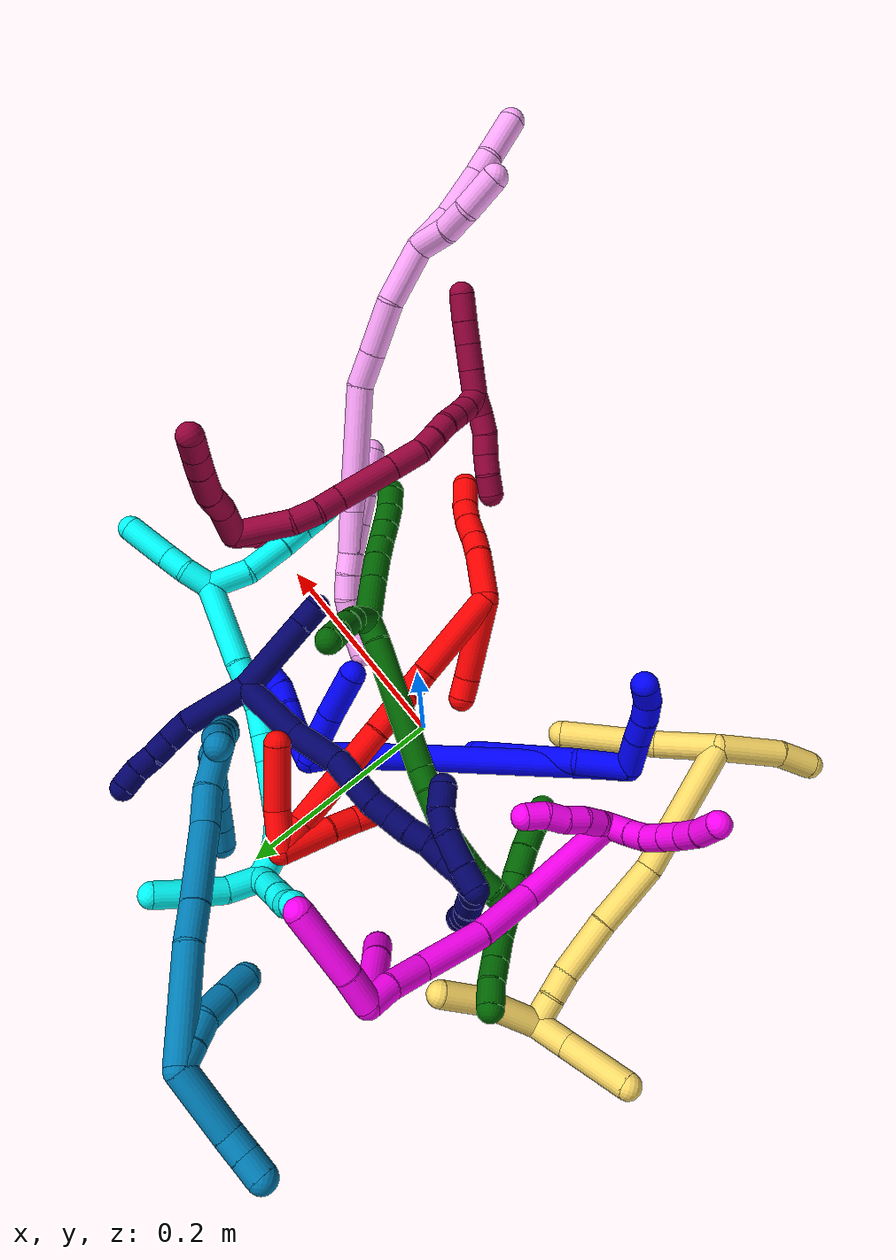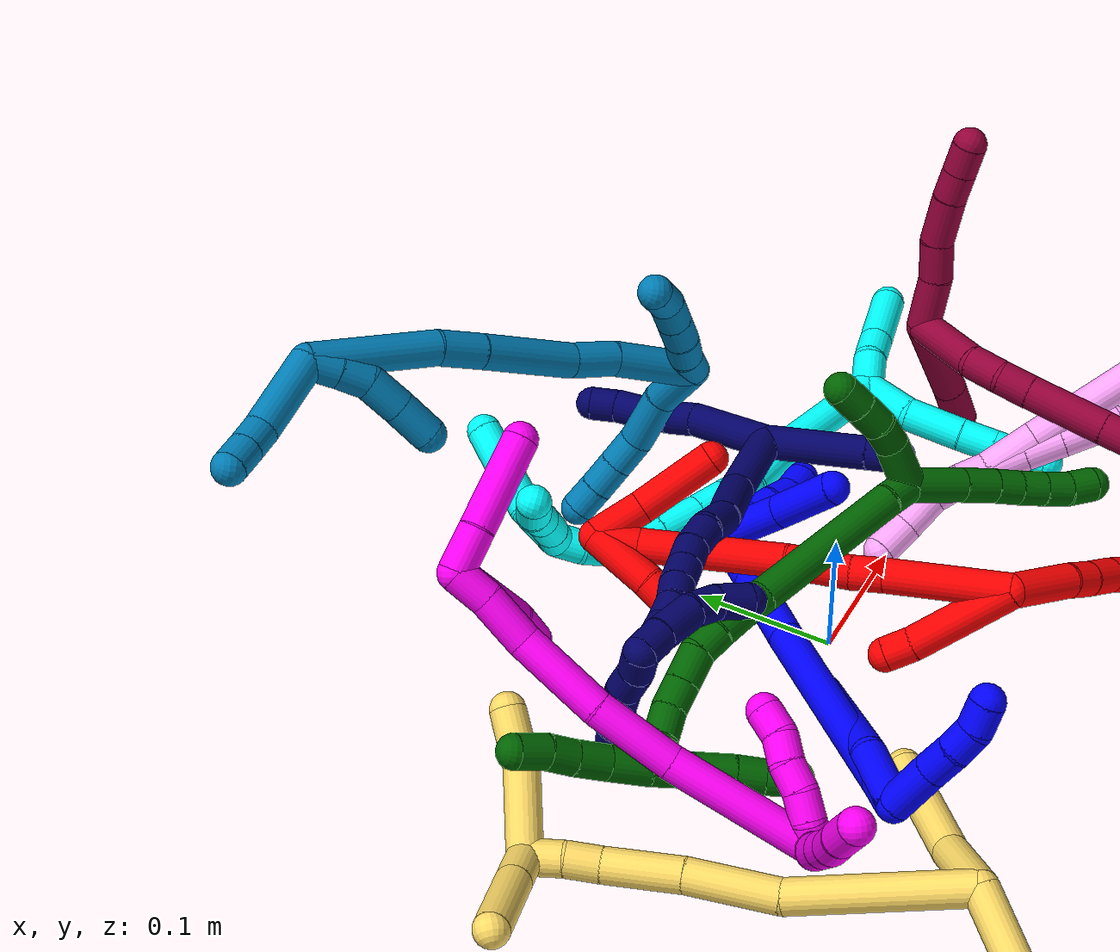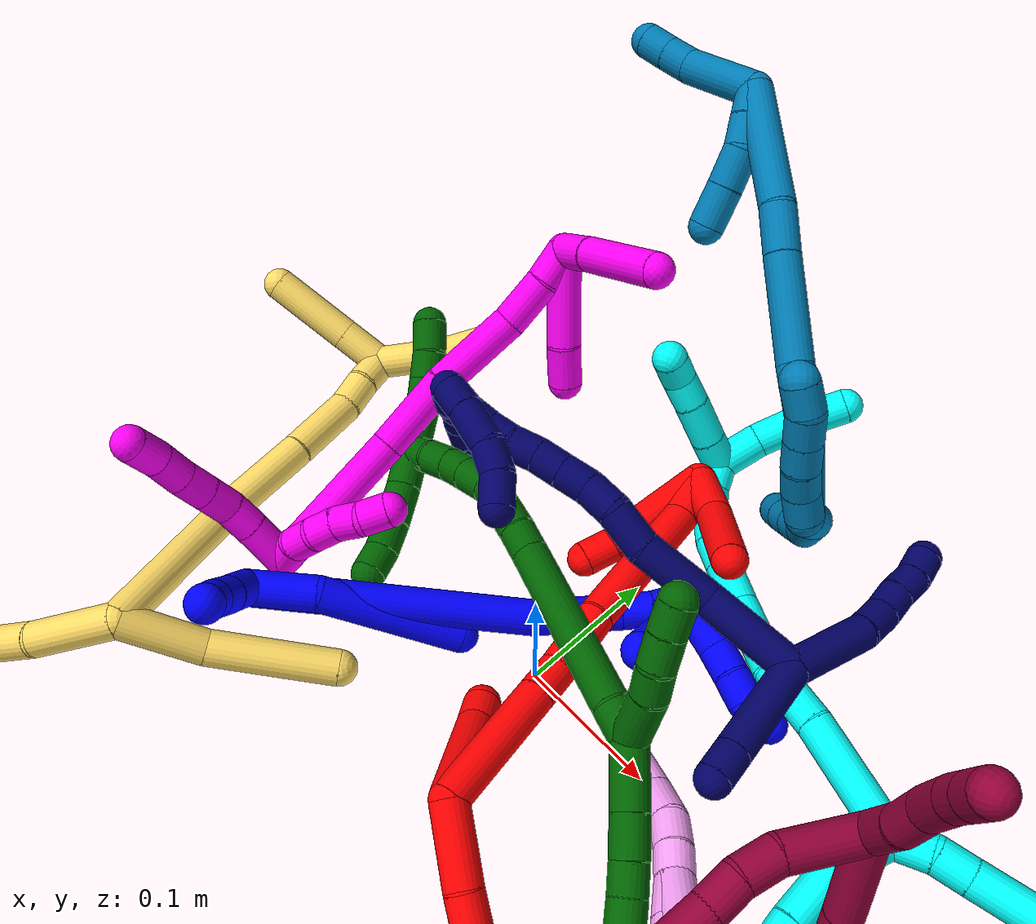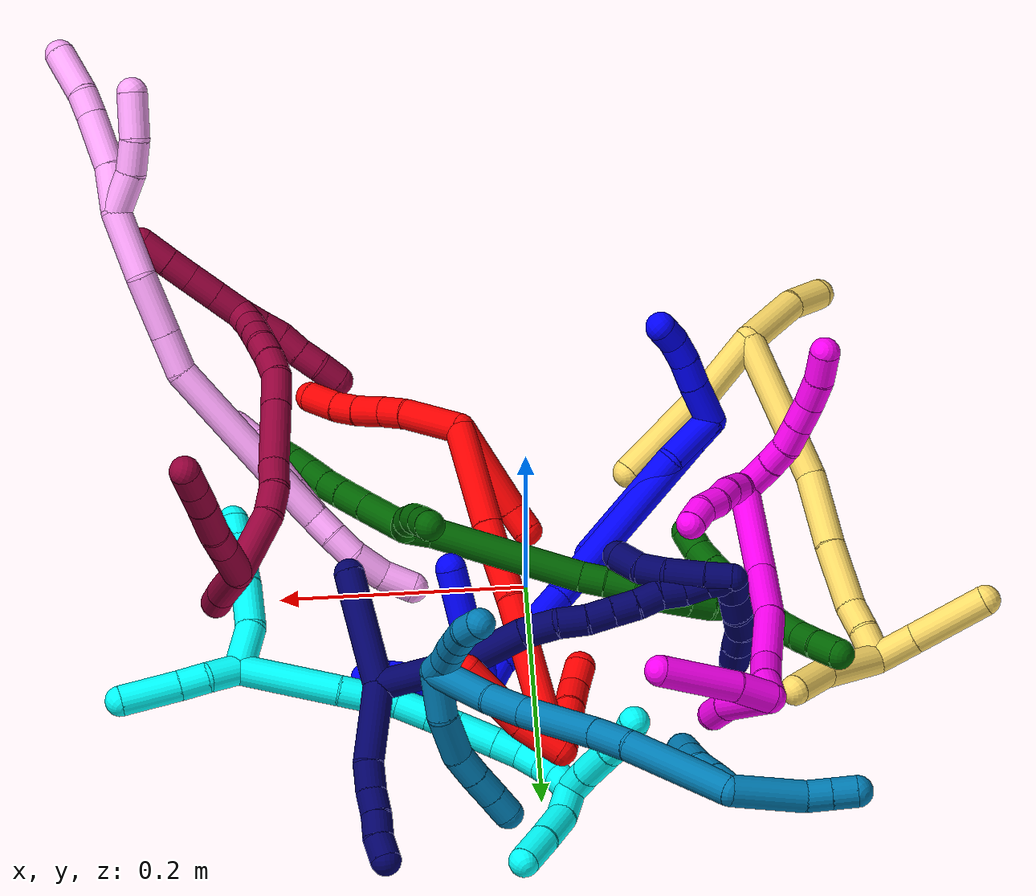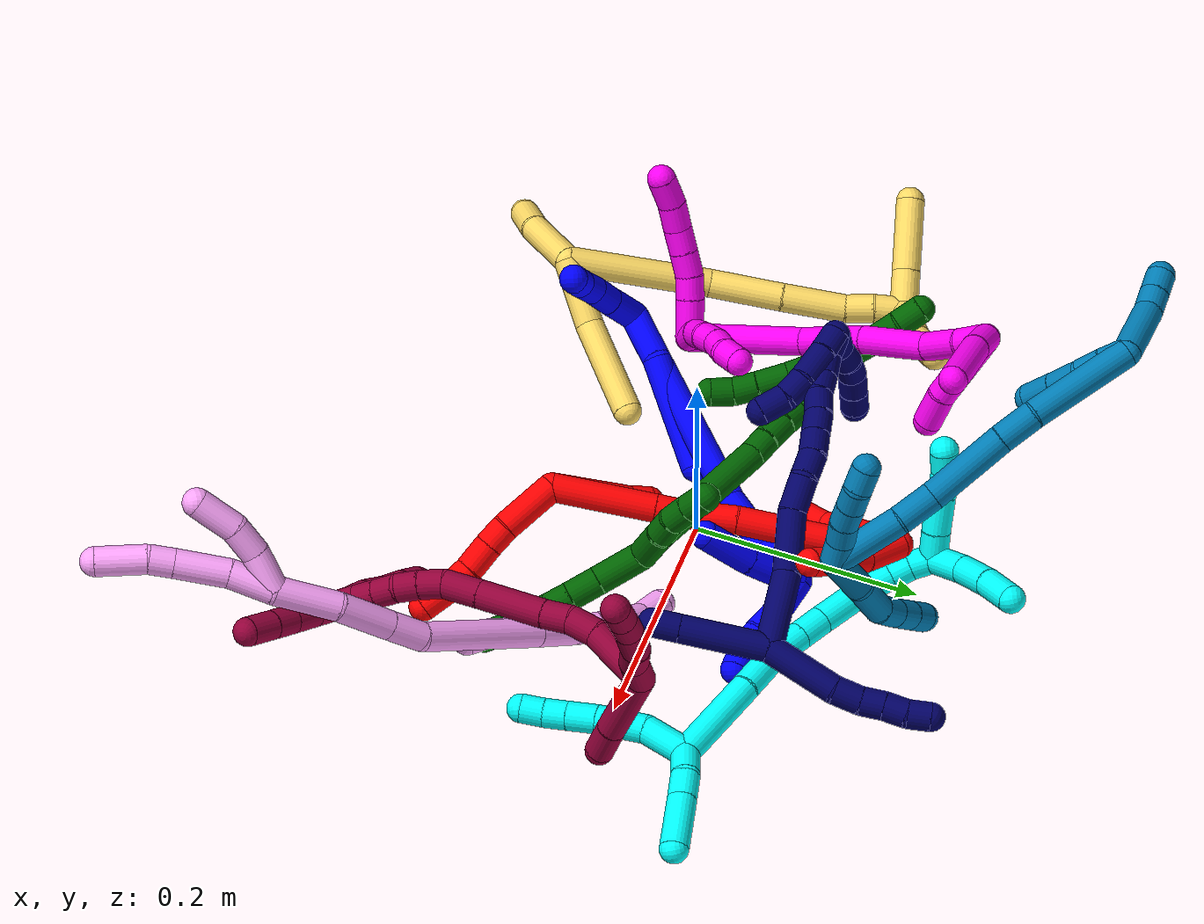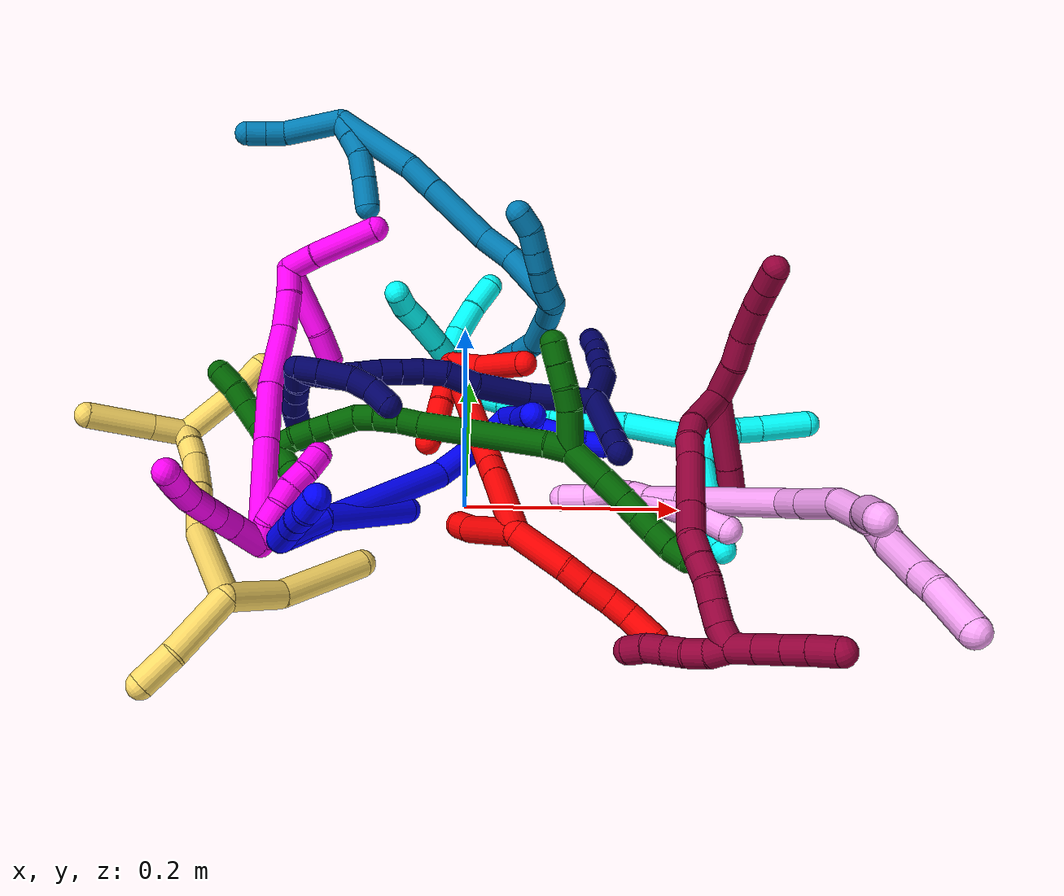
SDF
<sdf version="1.7">
 <world name="default">
  <plugin name="TubeGeneratorPlugin" filename="libtube_generator_plugin.so"/>
  <model name="photoneo_s_sensor">
   <static>1</static>
   <pose>0 0 2 1.57079 1.57079 3.14159</pose>
   <link name="link">
    <inertial><mass>0.1</mass></inertial>
    <sensor name="sensor" type="depth">
     <update_rate>30</update_rate>
     <camera>
      <horizontal_fov>1.22</horizontal_fov>
      <image><width>1920</width><height>1200</height><format>B8G8R8</format></image>
      <clip><near>0.1</near><far>4</far></clip>
      <depth_camera><output>points</output></depth_camera>
     </camera>
     <plugin name="camera_plugin" filename="libgazebo_ros_depth_camera.so">
      <baseline>0.2</baseline>
      <alwaysOn>1</alwaysOn>
      <updateRate>0.0</updateRate>
      <cameraName>camera_ir</cameraName>
      <imageTopicName>/camera/color/image_raw</imageTopicName>
      <cameraInfoTopicName>/camera/color/camera_info</cameraInfoTopicName>
      <depthImageTopicName>/camera/depth/image_raw</depthImageTopicName>
      <depthImageCameraInfoTopicName>/camera/depth/camera_info</depthImageCameraInfoTopicName>
      <pointCloudTopicName>/camera/depth/points</pointCloudTopicName>
      <frameName>fr_optical</frameName>
      <pointCloudCutoff>0.1</pointCloudCutoff>
      <pointCloudCutoffMax>2.0</pointCloudCutoffMax>
      <distortionK1>0</distortionK1>
      <distortionK2>0</distortionK2>
      <distortionK3>0</distortionK3>
      <distortionT1>0</distortionT1>
      <distortionT2>0</distortionT2>
      <CxPrime>0</CxPrime>
      <Cx>0</Cx>
      <Cy>0</Cy>
      <focalLength>0</focalLength>
      <hackBaseline>0</hackBaseline>
     </plugin>
    </sensor>
   </link>
  </model>
  <gravity>0 0 -9.8</gravity>
  <magnetic_field>6e-06 2.3e-05 -4.2e-05</magnetic_field>
  <atmosphere type="adiabatic"/>
  <physics name="default_physics" default="0" type="ode">
   <max_step_size>0.003</max_step_size>
   <real_time_factor>1</real_time_factor>
   <real_time_update_rate>1000</real_time_update_rate>
   <max_contacts>10000</max_contacts>
   <ode>
    <solver>
     <type>quick</type>
     <iters>100</iters>
     <sor>1.3</sor>
     <use_dynamic_moi_rescaling>0</use_dynamic_moi_rescaling>
    </solver>
    <constraints>
     <contact_max_correcting_vel>0</contact_max_correcting_vel>
     <contact_surface_layer>0.001</contact_surface_layer>
     <cfm>0</cfm>
     <erp>0.2</erp>
    </constraints>
   </ode>
  </physics>
  <scene><ambient>0.4 0.4 0.4 1</ambient><background>0.7 0.7 0.7 1</background><shadows>0</shadows></scene>
  <audio><device>default</device></audio>
  <spherical_coordinates>
   <surface_model>EARTH_WGS84</surface_model>
   <latitude_deg>0</latitude_deg>
   <longitude_deg>0</longitude_deg>
   <elevation>0</elevation>
   <heading_deg>0</heading_deg>
  </spherical_coordinates>
  <model name="bin">
   <static>1</static>
   <link name="bottom">
    <collision name="collision-bottom">
     <pose>0 0 -0.01 0 -0 0</pose>
     <geometry><box><size>0.8 0.6 0.02</size></box></geometry>
     <surface>
      <friction><ode><mu>100</mu><mu2>100</mu2></ode></friction>
      <contact><collide_bitmask>65535</collide_bitmask></contact>
     </surface>
    </collision>
   </link>
   <link name="west_wall">
    <collision name="collision-west_wall">
     <pose>-0.41 0 0.1 0 -0 0</pose>
     <geometry><box><size>0.02 0.6 0.2</size></box></geometry>
     <surface>
      <friction><ode><mu>100</mu><mu2>100</mu2></ode></friction>
      <contact><collide_bitmask>65535</collide_bitmask></contact>
     </surface>
    </collision>
   </link>
   <link name="east_wall">
    <collision name="collision-east_wall">
     <pose>0.41 0 0.1 0 -0 0</pose>
     <geometry><box><size>0.02 0.6 0.2</size></box></geometry>
     <surface>
      <friction><ode><mu>100</mu><mu2>100</mu2></ode></friction>
      <contact><collide_bitmask>65535</collide_bitmask></contact>
     </surface>
    </collision>
   </link>
   <link name="south_wall">
    <collision name="collision-south_wall">
     <pose>0 -0.31 0.1 0 -0 0</pose>
     <geometry><box><size>0.8 0.02 0.2</size></box></geometry>
     <surface>
      <friction><ode><mu>100</mu><mu2>100</mu2></ode></friction>
      <contact><collide_bitmask>65535</collide_bitmask></contact>
     </surface>
    </collision>
   </link>
   <link name="north_wall">
    <collision name="collision-north_wall">
     <pose>0 0.31 0.1 0 -0 0</pose>
     <geometry><box><size>0.8 0.02 0.2</size></box></geometry>
     <surface>
      <friction><ode><mu>100</mu><mu2>100</mu2></ode></friction>
      <contact><collide_bitmask>65535</collide_bitmask></contact>
     </surface>
    </collision>
   </link>
  </model>
  <model name="1">
   <static>0</static>
   <link name="1">
    <collision name="collision-cylinder-e_1_2_8">
     <pose>0.00512 0.013647 -0.019346 -2.52725 0.212998 -0.65011</pose>
     <geometry><cylinder><radius>0.0125</radius><length>0.048444</length></cylinder></geometry>
     <surface>
      <friction><ode><mu>1.16</mu><mu2>1.16</mu2><slip1>0</slip1><slip2>0</slip2></ode></friction>
      <contact><ode><kp>1e+06</kp><kd>1</kd><max_vel>0</max_vel><min_depth>0.001</min_depth></ode></contact>
     </surface>
    </collision>
    <visual name="visual-cylinder-e_1_2_8">
     <pose>0.00512 0.013647 -0.019346 -2.52725 0.212998 -0.65011</pose>
     <geometry><cylinder><radius>0.0125</radius><length>0.048444</length></cylinder></geometry>
     <material><ambient>0 0 1 1</ambient></material>
    </visual>
    <collision name="collision-cylinder-e_2_8_6">
     <pose>0.010983 0.044177 -0.086574 -2.80259 0.014629 -0.085427</pose>
     <geometry><cylinder><radius>0.0125</radius><length>0.101556</length></cylinder></geometry>
     <surface>
      <friction><ode><mu>1.16</mu><mu2>1.16</mu2><slip1>0</slip1><slip2>0</slip2></ode></friction>
      <contact><ode><kp>1e+06</kp><kd>1</kd><max_vel>0</max_vel><min_depth>0.001</min_depth></ode></contact>
     </surface>
    </collision>
    <visual name="visual-cylinder-e_2_8_6">
     <pose>0.010983 0.044177 -0.086574 -2.80259 0.014629 -0.085427</pose>
     <geometry><cylinder><radius>0.0125</radius><length>0.101556</length></cylinder></geometry>
     <material><ambient>0 0 1 1</ambient></material>
    </visual>
    <collision name="collision-cylinder-e_1_2_9">
     <pose>0.017057 -0.000542 0.007029 0.076928 1.17888 0.051459</pose>
     <geometry><cylinder><radius>0.0125</radius><length>0.036913</length></cylinder></geometry>
     <surface>
      <friction><ode><mu>1.16</mu><mu2>1.16</mu2><slip1>0</slip1><slip2>0</slip2></ode></friction>
      <contact><ode><kp>1e+06</kp><kd>1</kd><max_vel>0</max_vel><min_depth>0.001</min_depth></ode></contact>
     </surface>
    </collision>
    <visual name="visual-cylinder-e_1_2_9">
     <pose>0.017057 -0.000542 0.007029 0.076928 1.17888 0.051459</pose>
     <geometry><cylinder><radius>0.0125</radius><length>0.036913</length></cylinder></geometry>
     <material><ambient>0 0 1 1</ambient></material>
    </visual>
    <collision name="collision-cylinder-e_2_9_10">
     <pose>0.044342 -0.001694 0.018936 0.124406 1.12271 0.078293</pose>
     <geometry><cylinder><radius>0.0125</radius><length>0.022695</length></cylinder></geometry>
     <surface>
      <friction><ode><mu>1.16</mu><mu2>1.16</mu2><slip1>0</slip1><slip2>0</slip2></ode></friction>
      <contact><ode><kp>1e+06</kp><kd>1</kd><max_vel>0</max_vel><min_depth>0.001</min_depth></ode></contact>
     </surface>
    </collision>
    <visual name="visual-cylinder-e_2_9_10">
     <pose>0.044342 -0.001694 0.018936 0.124406 1.12271 0.078293</pose>
     <geometry><cylinder><radius>0.0125</radius><length>0.022695</length></cylinder></geometry>
     <material><ambient>0 0 1 1</ambient></material>
    </visual>
    <collision name="collision-cylinder-e_3_10_11">
     <pose>0.064136 -0.002334 0.026974 0.009524 1.25176 0.006884</pose>
     <geometry><cylinder><radius>0.0125</radius><length>0.020151</length></cylinder></geometry>
     <surface>
      <friction><ode><mu>1.16</mu><mu2>1.16</mu2><slip1>0</slip1><slip2>0</slip2></ode></friction>
      <contact><ode><kp>1e+06</kp><kd>1</kd><max_vel>0</max_vel><min_depth>0.001</min_depth></ode></contact>
     </surface>
    </collision>
    <visual name="visual-cylinder-e_3_10_11">
     <pose>0.064136 -0.002334 0.026974 0.009524 1.25176 0.006884</pose>
     <geometry><cylinder><radius>0.0125</radius><length>0.020151</length></cylinder></geometry>
     <material><ambient>0 0 1 1</ambient></material>
    </visual>
    <collision name="collision-cylinder-e_4_11_5">
     <pose>0.083139 0.000729 0.03209 -1.00695 1.20079 -0.721328</pose>
     <geometry><cylinder><radius>0.0125</radius><length>0.02024</length></cylinder></geometry>
     <surface>
      <friction><ode><mu>1.16</mu><mu2>1.16</mu2><slip1>0</slip1><slip2>0</slip2></ode></friction>
      <contact><ode><kp>1e+06</kp><kd>1</kd><max_vel>0</max_vel><min_depth>0.001</min_depth></ode></contact>
     </surface>
    </collision>
    <visual name="visual-cylinder-e_4_11_5">
     <pose>0.083139 0.000729 0.03209 -1.00695 1.20079 -0.721328</pose>
     <geometry><cylinder><radius>0.0125</radius><length>0.02024</length></cylinder></geometry>
     <material><ambient>0 0 1 1</ambient></material>
    </visual>
    <collision name="collision-cylinder-e_1_2_12">
     <pose>0.001744 0.00656 -0.010443 -2.58071 0.140483 -0.479154</pose>
     <geometry><cylinder><radius>0.0125</radius><length>0.02491</length></cylinder></geometry>
     <surface>
      <friction><ode><mu>1.16</mu><mu2>1.16</mu2><slip1>0</slip1><slip2>0</slip2></ode></friction>
      <contact><ode><kp>1e+06</kp><kd>1</kd><max_vel>0</max_vel><min_depth>0.001</min_depth></ode></contact>
     </surface>
    </collision>
    <visual name="visual-cylinder-e_1_2_12">
     <pose>0.001744 0.00656 -0.010443 -2.58071 0.140483 -0.479154</pose>
     <geometry><cylinder><radius>0.0125</radius><length>0.02491</length></cylinder></geometry>
     <material><ambient>0 0 1 1</ambient></material>
    </visual>
    <collision name="collision-cylinder-e_2_12_13">
     <pose>0.012299 0.057565 -0.092678 -2.58726 0.103973 -0.361805</pose>
     <geometry><cylinder><radius>0.0125</radius><length>0.16979</length></cylinder></geometry>
     <surface>
      <friction><ode><mu>1.16</mu><mu2>1.16</mu2><slip1>0</slip1><slip2>0</slip2></ode></friction>
      <contact><ode><kp>1e+06</kp><kd>1</kd><max_vel>0</max_vel><min_depth>0.001</min_depth></ode></contact>
     </surface>
    </collision>
    <visual name="visual-cylinder-e_2_12_13">
     <pose>0.012299 0.057565 -0.092678 -2.58726 0.103973 -0.361805</pose>
     <geometry><cylinder><radius>0.0125</radius><length>0.16979</length></cylinder></geometry>
     <material><ambient>0 0 1 1</ambient></material>
    </visual>
    <collision name="collision-cylinder-e_3_13_14">
     <pose>0.027116 0.122602 -0.18559 -2.36885 0.200878 -0.485668</pose>
     <geometry><cylinder><radius>0.0125</radius><length>0.060205</length></cylinder></geometry>
     <surface>
      <friction><ode><mu>1.16</mu><mu2>1.16</mu2><slip1>0</slip1><slip2>0</slip2></ode></friction>
      <contact><ode><kp>1e+06</kp><kd>1</kd><max_vel>0</max_vel><min_depth>0.001</min_depth></ode></contact>
     </surface>
    </collision>
    <visual name="visual-cylinder-e_3_13_14">
     <pose>0.027116 0.122602 -0.18559 -2.36885 0.200878 -0.485668</pose>
     <geometry><cylinder><radius>0.0125</radius><length>0.060205</length></cylinder></geometry>
     <material><ambient>0 0 1 1</ambient></material>
    </visual>
    <collision name="collision-cylinder-e_4_14_15">
     <pose>0.035387 0.150704 -0.213899 -2.33441 0.21447 -0.493879</pose>
     <geometry><cylinder><radius>0.0125</radius><length>0.02128</length></cylinder></geometry>
     <surface>
      <friction><ode><mu>1.16</mu><mu2>1.16</mu2><slip1>0</slip1><slip2>0</slip2></ode></friction>
      <contact><ode><kp>1e+06</kp><kd>1</kd><max_vel>0</max_vel><min_depth>0.001</min_depth></ode></contact>
     </surface>
    </collision>
    <visual name="visual-cylinder-e_4_14_15">
     <pose>0.035387 0.150704 -0.213899 -2.33441 0.21447 -0.493879</pose>
     <geometry><cylinder><radius>0.0125</radius><length>0.02128</length></cylinder></geometry>
     <material><ambient>0 0 1 1</ambient></material>
    </visual>
    <collision name="collision-cylinder-e_5_15_1">
     <pose>0.038285 0.167486 -0.228532 -2.24719 0.053272 -0.110985</pose>
     <geometry><cylinder><radius>0.0125</radius><length>0.023816</length></cylinder></geometry>
     <surface>
      <friction><ode><mu>1.16</mu><mu2>1.16</mu2><slip1>0</slip1><slip2>0</slip2></ode></friction>
      <contact><ode><kp>1e+06</kp><kd>1</kd><max_vel>0</max_vel><min_depth>0.001</min_depth></ode></contact>
     </surface>
    </collision>
    <visual name="visual-cylinder-e_5_15_1">
     <pose>0.038285 0.167486 -0.228532 -2.24719 0.053272 -0.110985</pose>
     <geometry><cylinder><radius>0.0125</radius><length>0.023816</length></cylinder></geometry>
     <material><ambient>0 0 1 1</ambient></material>
    </visual>
    <collision name="collision-cylinder-e_1_1_16">
     <pose>0.050701 0.171302 -0.249753 2.76444 0.6717 2.14097</pose>
     <geometry><cylinder><radius>0.0125</radius><length>0.037863</length></cylinder></geometry>
     <surface>
      <friction><ode><mu>1.16</mu><mu2>1.16</mu2><slip1>0</slip1><slip2>0</slip2></ode></friction>
      <contact><ode><kp>1e+06</kp><kd>1</kd><max_vel>0</max_vel><min_depth>0.001</min_depth></ode></contact>
     </surface>
    </collision>
    <visual name="visual-cylinder-e_1_1_16">
     <pose>0.050701 0.171302 -0.249753 2.76444 0.6717 2.14097</pose>
     <geometry><cylinder><radius>0.0125</radius><length>0.037863</length></cylinder></geometry>
     <material><ambient>0 0 1 1</ambient></material>
    </visual>
    <collision name="collision-cylinder-e_2_16_17">
     <pose>0.070466 0.162547 -0.269925 2.66546 0.837351 2.14307</pose>
     <geometry><cylinder><radius>0.0125</radius><length>0.021495</length></cylinder></geometry>
     <surface>
      <friction><ode><mu>1.16</mu><mu2>1.16</mu2><slip1>0</slip1><slip2>0</slip2></ode></friction>
      <contact><ode><kp>1e+06</kp><kd>1</kd><max_vel>0</max_vel><min_depth>0.001</min_depth></ode></contact>
     </surface>
    </collision>
    <visual name="visual-cylinder-e_2_16_17">
     <pose>0.070466 0.162547 -0.269925 2.66546 0.837351 2.14307</pose>
     <geometry><cylinder><radius>0.0125</radius><length>0.021495</length></cylinder></geometry>
     <material><ambient>0 0 1 1</ambient></material>
    </visual>
    <collision name="collision-cylinder-e_3_17_18">
     <pose>0.084899 0.155527 -0.283443 2.6601 0.676162 1.92242</pose>
     <geometry><cylinder><radius>0.0125</radius><length>0.020609</length></cylinder></geometry>
     <surface>
      <friction><ode><mu>1.16</mu><mu2>1.16</mu2><slip1>0</slip1><slip2>0</slip2></ode></friction>
      <contact><ode><kp>1e+06</kp><kd>1</kd><max_vel>0</max_vel><min_depth>0.001</min_depth></ode></contact>
     </surface>
    </collision>
    <visual name="visual-cylinder-e_3_17_18">
     <pose>0.084899 0.155527 -0.283443 2.6601 0.676162 1.92242</pose>
     <geometry><cylinder><radius>0.0125</radius><length>0.020609</length></cylinder></geometry>
     <material><ambient>0 0 1 1</ambient></material>
    </visual>
    <collision name="collision-cylinder-e_4_18_4">
     <pose>0.097717 0.15129 -0.29828 3.07488 0.689175 2.95617</pose>
     <geometry><cylinder><radius>0.0125</radius><length>0.020033</length></cylinder></geometry>
     <surface>
      <friction><ode><mu>1.16</mu><mu2>1.16</mu2><slip1>0</slip1><slip2>0</slip2></ode></friction>
      <contact><ode><kp>1e+06</kp><kd>1</kd><max_vel>0</max_vel><min_depth>0.001</min_depth></ode></contact>
     </surface>
    </collision>
    <visual name="visual-cylinder-e_4_18_4">
     <pose>0.097717 0.15129 -0.29828 3.07488 0.689175 2.95617</pose>
     <geometry><cylinder><radius>0.0125</radius><length>0.020033</length></cylinder></geometry>
     <material><ambient>0 0 1 1</ambient></material>
    </visual>
    <collision name="collision-cylinder-e_1_1_19">
     <pose>0.060582 0.166775 -0.225308 0.752327 0.977405 0.414013</pose>
     <geometry><cylinder><radius>0.0125</radius><length>0.052258</length></cylinder></geometry>
     <surface>
      <friction><ode><mu>1.16</mu><mu2>1.16</mu2><slip1>0</slip1><slip2>0</slip2></ode></friction>
      <contact><ode><kp>1e+06</kp><kd>1</kd><max_vel>0</max_vel><min_depth>0.001</min_depth></ode></contact>
     </surface>
    </collision>
    <visual name="visual-cylinder-e_1_1_19">
     <pose>0.060582 0.166775 -0.225308 0.752327 0.977405 0.414013</pose>
     <geometry><cylinder><radius>0.0125</radius><length>0.052258</length></cylinder></geometry>
     <material><ambient>0 0 1 1</ambient></material>
    </visual>
    <collision name="collision-cylinder-e_2_19_3">
     <pose>0.101383 0.148927 -0.202738 0.583831 0.930226 0.299346</pose>
     <geometry><cylinder><radius>0.0125</radius><length>0.047742</length></cylinder></geometry>
     <surface>
      <friction><ode><mu>1.16</mu><mu2>1.16</mu2><slip1>0</slip1><slip2>0</slip2></ode></friction>
      <contact><ode><kp>1e+06</kp><kd>1</kd><max_vel>0</max_vel><min_depth>0.001</min_depth></ode></contact>
     </surface>
    </collision>
    <visual name="visual-cylinder-e_2_19_3">
     <pose>0.101383 0.148927 -0.202738 0.583831 0.930226 0.299346</pose>
     <geometry><cylinder><radius>0.0125</radius><length>0.047742</length></cylinder></geometry>
     <material><ambient>0 0 1 1</ambient></material>
    </visual>
    <collision name="collision-sphere-3">
     <pose>0.120521 0.141063 -0.190834 0 -0 0</pose>
     <geometry><sphere><radius>0.0125</radius></sphere></geometry>
     <surface>
      <friction><ode><mu>1.16</mu><mu2>1.16</mu2><slip1>0</slip1><slip2>0</slip2></ode></friction>
      <contact><ode><kp>1e+06</kp><kd>1</kd><max_vel>0</max_vel><min_depth>0.001</min_depth></ode></contact>
     </surface>
    </collision>
    <visual name="visual-sphere-3">
     <pose>0.120521 0.141063 -0.190834 0 -0 0</pose>
     <geometry><sphere><radius>0.0125</radius></sphere></geometry>
     <material><ambient>0 0 1 1</ambient></material>
    </visual>
    <collision name="collision-sphere-19">
     <pose>0.082244 0.156791 -0.214641 0 -0 0</pose>
     <geometry><sphere><radius>0.0125</radius></sphere></geometry>
     <surface>
      <friction><ode><mu>1.16</mu><mu2>1.16</mu2><slip1>0</slip1><slip2>0</slip2></ode></friction>
      <contact><ode><kp>1e+06</kp><kd>1</kd><max_vel>0</max_vel><min_depth>0.001</min_depth></ode></contact>
     </surface>
    </collision>
    <visual name="visual-sphere-19">
     <pose>0.082244 0.156791 -0.214641 0 -0 0</pose>
     <geometry><sphere><radius>0.0125</radius></sphere></geometry>
     <material><ambient>0 0 1 1</ambient></material>
    </visual>
    <collision name="collision-sphere-11">
     <pose>0.073704 -0.002364 0.030134 0 -0 0</pose>
     <geometry><sphere><radius>0.0125</radius></sphere></geometry>
     <surface>
      <friction><ode><mu>1.16</mu><mu2>1.16</mu2><slip1>0</slip1><slip2>0</slip2></ode></friction>
      <contact><ode><kp>1e+06</kp><kd>1</kd><max_vel>0</max_vel><min_depth>0.001</min_depth></ode></contact>
     </surface>
    </collision>
    <visual name="visual-sphere-11">
     <pose>0.073704 -0.002364 0.030134 0 -0 0</pose>
     <geometry><sphere><radius>0.0125</radius></sphere></geometry>
     <material><ambient>0 0 1 1</ambient></material>
    </visual>
    <collision name="collision-sphere-10">
     <pose>0.054569 -0.002304 0.023814 0 -0 0</pose>
     <geometry><sphere><radius>0.0125</radius></sphere></geometry>
     <surface>
      <friction><ode><mu>1.16</mu><mu2>1.16</mu2><slip1>0</slip1><slip2>0</slip2></ode></friction>
      <contact><ode><kp>1e+06</kp><kd>1</kd><max_vel>0</max_vel><min_depth>0.001</min_depth></ode></contact>
     </surface>
    </collision>
    <visual name="visual-sphere-10">
     <pose>0.054569 -0.002304 0.023814 0 -0 0</pose>
     <geometry><sphere><radius>0.0125</radius></sphere></geometry>
     <material><ambient>0 0 1 1</ambient></material>
    </visual>
    <collision name="collision-sphere-6">
     <pose>0.011726 0.061061 -0.134457 0 -0 0</pose>
     <geometry><sphere><radius>0.0125</radius></sphere></geometry>
     <surface>
      <friction><ode><mu>1.16</mu><mu2>1.16</mu2><slip1>0</slip1><slip2>0</slip2></ode></friction>
      <contact><ode><kp>1e+06</kp><kd>1</kd><max_vel>0</max_vel><min_depth>0.001</min_depth></ode></contact>
     </surface>
    </collision>
    <visual name="visual-sphere-6">
     <pose>0.011726 0.061061 -0.134457 0 -0 0</pose>
     <geometry><sphere><radius>0.0125</radius></sphere></geometry>
     <material><ambient>0 0 1 1</ambient></material>
    </visual>
    <collision name="collision-sphere-9">
     <pose>0.034114 -0.001084 0.014058 0 -0 0</pose>
     <geometry><sphere><radius>0.0125</radius></sphere></geometry>
     <surface>
      <friction><ode><mu>1.16</mu><mu2>1.16</mu2><slip1>0</slip1><slip2>0</slip2></ode></friction>
      <contact><ode><kp>1e+06</kp><kd>1</kd><max_vel>0</max_vel><min_depth>0.001</min_depth></ode></contact>
     </surface>
    </collision>
    <visual name="visual-sphere-9">
     <pose>0.034114 -0.001084 0.014058 0 -0 0</pose>
     <geometry><sphere><radius>0.0125</radius></sphere></geometry>
     <material><ambient>0 0 1 1</ambient></material>
    </visual>
    <collision name="collision-sphere-2">
     <geometry><sphere><radius>0.0125</radius></sphere></geometry>
     <surface>
      <friction><ode><mu>1.16</mu><mu2>1.16</mu2><slip1>0</slip1><slip2>0</slip2></ode></friction>
      <contact><ode><kp>1e+06</kp><kd>1</kd><max_vel>0</max_vel><min_depth>0.001</min_depth></ode></contact>
     </surface>
    </collision>
    <visual name="visual-sphere-2">
     <geometry><sphere><radius>0.0125</radius></sphere></geometry>
     <material><ambient>0 0 1 1</ambient></material>
    </visual>
    <collision name="collision-sphere-8">
     <pose>0.010241 0.027293 -0.038692 0 -0 0</pose>
     <geometry><sphere><radius>0.0125</radius></sphere></geometry>
     <surface>
      <friction><ode><mu>1.16</mu><mu2>1.16</mu2><slip1>0</slip1><slip2>0</slip2></ode></friction>
      <contact><ode><kp>1e+06</kp><kd>1</kd><max_vel>0</max_vel><min_depth>0.001</min_depth></ode></contact>
     </surface>
    </collision>
    <visual name="visual-sphere-8">
     <pose>0.010241 0.027293 -0.038692 0 -0 0</pose>
     <geometry><sphere><radius>0.0125</radius></sphere></geometry>
     <material><ambient>0 0 1 1</ambient></material>
    </visual>
    <collision name="collision-sphere-5">
     <pose>0.092574 0.003822 0.034046 0 -0 0</pose>
     <geometry><sphere><radius>0.0125</radius></sphere></geometry>
     <surface>
      <friction><ode><mu>1.16</mu><mu2>1.16</mu2><slip1>0</slip1><slip2>0</slip2></ode></friction>
      <contact><ode><kp>1e+06</kp><kd>1</kd><max_vel>0</max_vel><min_depth>0.001</min_depth></ode></contact>
     </surface>
    </collision>
    <visual name="visual-sphere-5">
     <pose>0.092574 0.003822 0.034046 0 -0 0</pose>
     <geometry><sphere><radius>0.0125</radius></sphere></geometry>
     <material><ambient>0 0 1 1</ambient></material>
    </visual>
    <collision name="collision-sphere-12">
     <pose>0.003488 0.01312 -0.020886 0 -0 0</pose>
     <geometry><sphere><radius>0.0125</radius></sphere></geometry>
     <surface>
      <friction><ode><mu>1.16</mu><mu2>1.16</mu2><slip1>0</slip1><slip2>0</slip2></ode></friction>
      <contact><ode><kp>1e+06</kp><kd>1</kd><max_vel>0</max_vel><min_depth>0.001</min_depth></ode></contact>
     </surface>
    </collision>
    <visual name="visual-sphere-12">
     <pose>0.003488 0.01312 -0.020886 0 -0 0</pose>
     <geometry><sphere><radius>0.0125</radius></sphere></geometry>
     <material><ambient>0 0 1 1</ambient></material>
    </visual>
    <collision name="collision-sphere-13">
     <pose>0.02111 0.10201 -0.16447 0 -0 0</pose>
     <geometry><sphere><radius>0.0125</radius></sphere></geometry>
     <surface>
      <friction><ode><mu>1.16</mu><mu2>1.16</mu2><slip1>0</slip1><slip2>0</slip2></ode></friction>
      <contact><ode><kp>1e+06</kp><kd>1</kd><max_vel>0</max_vel><min_depth>0.001</min_depth></ode></contact>
     </surface>
    </collision>
    <visual name="visual-sphere-13">
     <pose>0.02111 0.10201 -0.16447 0 -0 0</pose>
     <geometry><sphere><radius>0.0125</radius></sphere></geometry>
     <material><ambient>0 0 1 1</ambient></material>
    </visual>
    <collision name="collision-sphere-14">
     <pose>0.033122 0.143194 -0.20671 0 -0 0</pose>
     <geometry><sphere><radius>0.0125</radius></sphere></geometry>
     <surface>
      <friction><ode><mu>1.16</mu><mu2>1.16</mu2><slip1>0</slip1><slip2>0</slip2></ode></friction>
      <contact><ode><kp>1e+06</kp><kd>1</kd><max_vel>0</max_vel><min_depth>0.001</min_depth></ode></contact>
     </surface>
    </collision>
    <visual name="visual-sphere-14">
     <pose>0.033122 0.143194 -0.20671 0 -0 0</pose>
     <geometry><sphere><radius>0.0125</radius></sphere></geometry>
     <material><ambient>0 0 1 1</ambient></material>
    </visual>
    <collision name="collision-sphere-15">
     <pose>0.037651 0.158213 -0.221088 0 -0 0</pose>
     <geometry><sphere><radius>0.0125</radius></sphere></geometry>
     <surface>
      <friction><ode><mu>1.16</mu><mu2>1.16</mu2><slip1>0</slip1><slip2>0</slip2></ode></friction>
      <contact><ode><kp>1e+06</kp><kd>1</kd><max_vel>0</max_vel><min_depth>0.001</min_depth></ode></contact>
     </surface>
    </collision>
    <visual name="visual-sphere-15">
     <pose>0.037651 0.158213 -0.221088 0 -0 0</pose>
     <geometry><sphere><radius>0.0125</radius></sphere></geometry>
     <material><ambient>0 0 1 1</ambient></material>
    </visual>
    <collision name="collision-sphere-1">
     <pose>0.038919 0.176759 -0.235976 0 -0 0</pose>
     <geometry><sphere><radius>0.0125</radius></sphere></geometry>
     <surface>
      <friction><ode><mu>1.16</mu><mu2>1.16</mu2><slip1>0</slip1><slip2>0</slip2></ode></friction>
      <contact><ode><kp>1e+06</kp><kd>1</kd><max_vel>0</max_vel><min_depth>0.001</min_depth></ode></contact>
     </surface>
    </collision>
    <visual name="visual-sphere-1">
     <pose>0.038919 0.176759 -0.235976 0 -0 0</pose>
     <geometry><sphere><radius>0.0125</radius></sphere></geometry>
     <material><ambient>0 0 1 1</ambient></material>
    </visual>
    <collision name="collision-sphere-18">
     <pose>0.091347 0.151805 -0.290566 0 -0 0</pose>
     <geometry><sphere><radius>0.0125</radius></sphere></geometry>
     <surface>
      <friction><ode><mu>1.16</mu><mu2>1.16</mu2><slip1>0</slip1><slip2>0</slip2></ode></friction>
      <contact><ode><kp>1e+06</kp><kd>1</kd><max_vel>0</max_vel><min_depth>0.001</min_depth></ode></contact>
     </surface>
    </collision>
    <visual name="visual-sphere-18">
     <pose>0.091347 0.151805 -0.290566 0 -0 0</pose>
     <geometry><sphere><radius>0.0125</radius></sphere></geometry>
     <material><ambient>0 0 1 1</ambient></material>
    </visual>
    <collision name="collision-sphere-16">
     <pose>0.062482 0.165845 -0.26353 0 -0 0</pose>
     <geometry><sphere><radius>0.0125</radius></sphere></geometry>
     <surface>
      <friction><ode><mu>1.16</mu><mu2>1.16</mu2><slip1>0</slip1><slip2>0</slip2></ode></friction>
      <contact><ode><kp>1e+06</kp><kd>1</kd><max_vel>0</max_vel><min_depth>0.001</min_depth></ode></contact>
     </surface>
    </collision>
    <visual name="visual-sphere-16">
     <pose>0.062482 0.165845 -0.26353 0 -0 0</pose>
     <geometry><sphere><radius>0.0125</radius></sphere></geometry>
     <material><ambient>0 0 1 1</ambient></material>
    </visual>
    <collision name="collision-sphere-17">
     <pose>0.07845 0.159249 -0.276319 0 -0 0</pose>
     <geometry><sphere><radius>0.0125</radius></sphere></geometry>
     <surface>
      <friction><ode><mu>1.16</mu><mu2>1.16</mu2><slip1>0</slip1><slip2>0</slip2></ode></friction>
      <contact><ode><kp>1e+06</kp><kd>1</kd><max_vel>0</max_vel><min_depth>0.001</min_depth></ode></contact>
     </surface>
    </collision>
    <visual name="visual-sphere-17">
     <pose>0.07845 0.159249 -0.276319 0 -0 0</pose>
     <geometry><sphere><radius>0.0125</radius></sphere></geometry>
     <material><ambient>0 0 1 1</ambient></material>
    </visual>
    <collision name="collision-sphere-4">
     <pose>0.104086 0.150774 -0.305993 0 -0 0</pose>
     <geometry><sphere><radius>0.0125</radius></sphere></geometry>
     <surface>
      <friction><ode><mu>1.16</mu><mu2>1.16</mu2><slip1>0</slip1><slip2>0</slip2></ode></friction>
      <contact><ode><kp>1e+06</kp><kd>1</kd><max_vel>0</max_vel><min_depth>0.001</min_depth></ode></contact>
     </surface>
    </collision>
    <visual name="visual-sphere-4">
     <pose>0.104086 0.150774 -0.305993 0 -0 0</pose>
     <geometry><sphere><radius>0.0125</radius></sphere></geometry>
     <material><ambient>0 0 1 1</ambient></material>
    </visual>
    <inertial>
     <pose>0.035402 0.08215 -0.124719 0 -0 0</pose>
     <mass>0.75</mass>
     <inertia>
      <ixx>0.000383</ixx>
      <ixy>0</ixy>
      <ixz>0</ixz>
      <iyy>-0.000535</iyy>
      <iyz>0</iyz>
      <izz>-0.000377</izz>
     </inertia>
    </inertial>
   </link>
   <pose>-0.158397 -0.115133 0.054442 0.688257 -0.685296 -0.473539</pose>
  </model>
  <model name="2">
   <static>0</static>
   <link name="2">
    <collision name="collision-cylinder-e_1_2_8">
     <pose>0.016185 -0.002239 0.02042 0.109228 0.667282 0.037891</pose>
     <geometry><cylinder><radius>0.0125</radius><length>0.052305</length></cylinder></geometry>
     <surface>
      <friction><ode><mu>1.16</mu><mu2>1.16</mu2><slip1>0</slip1><slip2>0</slip2></ode></friction>
      <contact><ode><kp>1e+06</kp><kd>1</kd><max_vel>0</max_vel><min_depth>0.001</min_depth></ode></contact>
     </surface>
    </collision>
    <visual name="visual-cylinder-e_1_2_8">
     <pose>0.016185 -0.002239 0.02042 0.109228 0.667282 0.037891</pose>
     <geometry><cylinder><radius>0.0125</radius><length>0.052305</length></cylinder></geometry>
     <material><ambient>1 0 0 1</ambient></material>
    </visual>
    <collision name="collision-cylinder-e_2_8_9">
     <pose>0.040208 -0.00528 0.047995 0.111479 0.827941 0.04902</pose>
     <geometry><cylinder><radius>0.0125</radius><length>0.021287</length></cylinder></geometry>
     <surface>
      <friction><ode><mu>1.16</mu><mu2>1.16</mu2><slip1>0</slip1><slip2>0</slip2></ode></friction>
      <contact><ode><kp>1e+06</kp><kd>1</kd><max_vel>0</max_vel><min_depth>0.001</min_depth></ode></contact>
     </surface>
    </collision>
    <visual name="visual-cylinder-e_2_8_9">
     <pose>0.040208 -0.00528 0.047995 0.111479 0.827941 0.04902</pose>
     <geometry><cylinder><radius>0.0125</radius><length>0.021287</length></cylinder></geometry>
     <material><ambient>1 0 0 1</ambient></material>
    </visual>
    <collision name="collision-cylinder-e_3_9_10">
     <pose>0.057793 -0.006186 0.063748 0.012236 0.847842 0.005522</pose>
     <geometry><cylinder><radius>0.0125</radius><length>0.025994</length></cylinder></geometry>
     <surface>
      <friction><ode><mu>1.16</mu><mu2>1.16</mu2><slip1>0</slip1><slip2>0</slip2></ode></friction>
      <contact><ode><kp>1e+06</kp><kd>1</kd><max_vel>0</max_vel><min_depth>0.001</min_depth></ode></contact>
     </surface>
    </collision>
    <visual name="visual-cylinder-e_3_9_10">
     <pose>0.057793 -0.006186 0.063748 0.012236 0.847842 0.005522</pose>
     <geometry><cylinder><radius>0.0125</radius><length>0.025994</length></cylinder></geometry>
     <material><ambient>1 0 0 1</ambient></material>
    </visual>
    <collision name="collision-cylinder-e_4_10_11">
     <pose>0.074802 -0.007419 0.079748 0.151268 0.770181 0.061411</pose>
     <geometry><cylinder><radius>0.0125</radius><length>0.020864</length></cylinder></geometry>
     <surface>
      <friction><ode><mu>1.16</mu><mu2>1.16</mu2><slip1>0</slip1><slip2>0</slip2></ode></friction>
      <contact><ode><kp>1e+06</kp><kd>1</kd><max_vel>0</max_vel><min_depth>0.001</min_depth></ode></contact>
     </surface>
    </collision>
    <visual name="visual-cylinder-e_4_10_11">
     <pose>0.074802 -0.007419 0.079748 0.151268 0.770181 0.061411</pose>
     <geometry><cylinder><radius>0.0125</radius><length>0.020864</length></cylinder></geometry>
     <material><ambient>1 0 0 1</ambient></material>
    </visual>
    <collision name="collision-cylinder-e_5_11_6">
     <pose>0.09107 -0.011752 0.098419 0.277085 0.655278 0.094714</pose>
     <geometry><cylinder><radius>0.0125</radius><length>0.029551</length></cylinder></geometry>
     <surface>
      <friction><ode><mu>1.16</mu><mu2>1.16</mu2><slip1>0</slip1><slip2>0</slip2></ode></friction>
      <contact><ode><kp>1e+06</kp><kd>1</kd><max_vel>0</max_vel><min_depth>0.001</min_depth></ode></contact>
     </surface>
    </collision>
    <visual name="visual-cylinder-e_5_11_6">
     <pose>0.09107 -0.011752 0.098419 0.277085 0.655278 0.094714</pose>
     <geometry><cylinder><radius>0.0125</radius><length>0.029551</length></cylinder></geometry>
     <material><ambient>1 0 0 1</ambient></material>
    </visual>
    <collision name="collision-cylinder-e_1_2_12">
     <pose>0.010979 0.004601 -0.037793 -3.02043 0.280766 -2.33072</pose>
     <geometry><cylinder><radius>0.0125</radius><length>0.079247</length></cylinder></geometry>
     <surface>
      <friction><ode><mu>1.16</mu><mu2>1.16</mu2><slip1>0</slip1><slip2>0</slip2></ode></friction>
      <contact><ode><kp>1e+06</kp><kd>1</kd><max_vel>0</max_vel><min_depth>0.001</min_depth></ode></contact>
     </surface>
    </collision>
    <visual name="visual-cylinder-e_1_2_12">
     <pose>0.010979 0.004601 -0.037793 -3.02043 0.280766 -2.33072</pose>
     <geometry><cylinder><radius>0.0125</radius><length>0.079247</length></cylinder></geometry>
     <material><ambient>1 0 0 1</ambient></material>
    </visual>
    <collision name="collision-cylinder-e_2_12_5">
     <pose>0.023381 0.011257 -0.085657 -2.94042 0.137467 -1.19724</pose>
     <geometry><cylinder><radius>0.0125</radius><length>0.020753</length></cylinder></geometry>
     <surface>
      <friction><ode><mu>1.16</mu><mu2>1.16</mu2><slip1>0</slip1><slip2>0</slip2></ode></friction>
      <contact><ode><kp>1e+06</kp><kd>1</kd><max_vel>0</max_vel><min_depth>0.001</min_depth></ode></contact>
     </surface>
    </collision>
    <visual name="visual-cylinder-e_2_12_5">
     <pose>0.023381 0.011257 -0.085657 -2.94042 0.137467 -1.19724</pose>
     <geometry><cylinder><radius>0.0125</radius><length>0.020753</length></cylinder></geometry>
     <material><ambient>1 0 0 1</ambient></material>
    </visual>
    <collision name="collision-cylinder-e_1_2_13">
     <pose>0.003066 0.028666 -0.034245 -2.44465 0.068537 -0.18817</pose>
     <geometry><cylinder><radius>0.0125</radius><length>0.089528</length></cylinder></geometry>
     <surface>
      <friction><ode><mu>1.16</mu><mu2>1.16</mu2><slip1>0</slip1><slip2>0</slip2></ode></friction>
      <contact><ode><kp>1e+06</kp><kd>1</kd><max_vel>0</max_vel><min_depth>0.001</min_depth></ode></contact>
     </surface>
    </collision>
    <visual name="visual-cylinder-e_1_2_13">
     <pose>0.003066 0.028666 -0.034245 -2.44465 0.068537 -0.18817</pose>
     <geometry><cylinder><radius>0.0125</radius><length>0.089528</length></cylinder></geometry>
     <material><ambient>1 0 0 1</ambient></material>
    </visual>
    <collision name="collision-cylinder-e_2_13_14">
     <pose>0.007223 0.064855 -0.077983 -2.47141 0.089914 -0.256959</pose>
     <geometry><cylinder><radius>0.0125</radius><length>0.024324</length></cylinder></geometry>
     <surface>
      <friction><ode><mu>1.16</mu><mu2>1.16</mu2><slip1>0</slip1><slip2>0</slip2></ode></friction>
      <contact><ode><kp>1e+06</kp><kd>1</kd><max_vel>0</max_vel><min_depth>0.001</min_depth></ode></contact>
     </surface>
    </collision>
    <visual name="visual-cylinder-e_2_13_14">
     <pose>0.007223 0.064855 -0.077983 -2.47141 0.089914 -0.256959</pose>
     <geometry><cylinder><radius>0.0125</radius><length>0.024324</length></cylinder></geometry>
     <material><ambient>1 0 0 1</ambient></material>
    </visual>
    <collision name="collision-cylinder-e_3_14_15">
     <pose>0.007422 0.08765 -0.104873 -2.42116 -0.038565 0.102313</pose>
     <geometry><cylinder><radius>0.0125</radius><length>0.046334</length></cylinder></geometry>
     <surface>
      <friction><ode><mu>1.16</mu><mu2>1.16</mu2><slip1>0</slip1><slip2>0</slip2></ode></friction>
      <contact><ode><kp>1e+06</kp><kd>1</kd><max_vel>0</max_vel><min_depth>0.001</min_depth></ode></contact>
     </surface>
    </collision>
    <visual name="visual-cylinder-e_3_14_15">
     <pose>0.007422 0.08765 -0.104873 -2.42116 -0.038565 0.102313</pose>
     <geometry><cylinder><radius>0.0125</radius><length>0.046334</length></cylinder></geometry>
     <material><ambient>1 0 0 1</ambient></material>
    </visual>
    <collision name="collision-cylinder-e_4_15_16">
     <pose>0.010958 0.137117 -0.163859 -2.45345 0.082086 -0.228216</pose>
     <geometry><cylinder><radius>0.0125</radius><length>0.108046</length></cylinder></geometry>
     <surface>
      <friction><ode><mu>1.16</mu><mu2>1.16</mu2><slip1>0</slip1><slip2>0</slip2></ode></friction>
      <contact><ode><kp>1e+06</kp><kd>1</kd><max_vel>0</max_vel><min_depth>0.001</min_depth></ode></contact>
     </surface>
    </collision>
    <visual name="visual-cylinder-e_4_15_16">
     <pose>0.010958 0.137117 -0.163859 -2.45345 0.082086 -0.228216</pose>
     <geometry><cylinder><radius>0.0125</radius><length>0.108046</length></cylinder></geometry>
     <material><ambient>1 0 0 1</ambient></material>
    </visual>
    <collision name="collision-cylinder-e_5_16_1">
     <pose>0.01197 0.181319 -0.217299 -2.44035 -0.216902 0.578689</pose>
     <geometry><cylinder><radius>0.0125</radius><length>0.031768</length></cylinder></geometry>
     <surface>
      <friction><ode><mu>1.16</mu><mu2>1.16</mu2><slip1>0</slip1><slip2>0</slip2></ode></friction>
      <contact><ode><kp>1e+06</kp><kd>1</kd><max_vel>0</max_vel><min_depth>0.001</min_depth></ode></contact>
     </surface>
    </collision>
    <visual name="visual-cylinder-e_5_16_1">
     <pose>0.01197 0.181319 -0.217299 -2.44035 -0.216902 0.578689</pose>
     <geometry><cylinder><radius>0.0125</radius><length>0.031768</length></cylinder></geometry>
     <material><ambient>1 0 0 1</ambient></material>
    </visual>
    <collision name="collision-cylinder-e_1_1_17">
     <pose>0.010781 0.192966 -0.210016 -0.085438 0.115603 -0.004947</pose>
     <geometry><cylinder><radius>0.0125</radius><length>0.038668</length></cylinder></geometry>
     <surface>
      <friction><ode><mu>1.16</mu><mu2>1.16</mu2><slip1>0</slip1><slip2>0</slip2></ode></friction>
      <contact><ode><kp>1e+06</kp><kd>1</kd><max_vel>0</max_vel><min_depth>0.001</min_depth></ode></contact>
     </surface>
    </collision>
    <visual name="visual-cylinder-e_1_1_17">
     <pose>0.010781 0.192966 -0.210016 -0.085438 0.115603 -0.004947</pose>
     <geometry><cylinder><radius>0.0125</radius><length>0.038668</length></cylinder></geometry>
     <material><ambient>1 0 0 1</ambient></material>
    </visual>
    <collision name="collision-cylinder-e_2_17_4">
     <pose>0.008509 0.195826 -0.160572 -0.040291 -0.147349 0.002974</pose>
     <geometry><cylinder><radius>0.0125</radius><length>0.061332</length></cylinder></geometry>
     <surface>
      <friction><ode><mu>1.16</mu><mu2>1.16</mu2><slip1>0</slip1><slip2>0</slip2></ode></friction>
      <contact><ode><kp>1e+06</kp><kd>1</kd><max_vel>0</max_vel><min_depth>0.001</min_depth></ode></contact>
     </surface>
    </collision>
    <visual name="visual-cylinder-e_2_17_4">
     <pose>0.008509 0.195826 -0.160572 -0.040291 -0.147349 0.002974</pose>
     <geometry><cylinder><radius>0.0125</radius><length>0.061332</length></cylinder></geometry>
     <material><ambient>1 0 0 1</ambient></material>
    </visual>
    <collision name="collision-cylinder-e_1_1_18">
     <pose>0.011575 0.167673 -0.22109 1.24235 0.120429 0.08624</pose>
     <geometry><cylinder><radius>0.0125</radius><length>0.050343</length></cylinder></geometry>
     <surface>
      <friction><ode><mu>1.16</mu><mu2>1.16</mu2><slip1>0</slip1><slip2>0</slip2></ode></friction>
      <contact><ode><kp>1e+06</kp><kd>1</kd><max_vel>0</max_vel><min_depth>0.001</min_depth></ode></contact>
     </surface>
    </collision>
    <visual name="visual-cylinder-e_1_1_18">
     <pose>0.011575 0.167673 -0.22109 1.24235 0.120429 0.08624</pose>
     <geometry><cylinder><radius>0.0125</radius><length>0.050343</length></cylinder></geometry>
     <material><ambient>1 0 0 1</ambient></material>
    </visual>
    <collision name="collision-cylinder-e_2_18_19">
     <pose>0.017545 0.13155 -0.209671 1.30773 0.224269 0.172159</pose>
     <geometry><cylinder><radius>0.0125</radius><length>0.026493</length></cylinder></geometry>
     <surface>
      <friction><ode><mu>1.16</mu><mu2>1.16</mu2><slip1>0</slip1><slip2>0</slip2></ode></friction>
      <contact><ode><kp>1e+06</kp><kd>1</kd><max_vel>0</max_vel><min_depth>0.001</min_depth></ode></contact>
     </surface>
    </collision>
    <visual name="visual-cylinder-e_2_18_19">
     <pose>0.017545 0.13155 -0.209671 1.30773 0.224269 0.172159</pose>
     <geometry><cylinder><radius>0.0125</radius><length>0.026493</length></cylinder></geometry>
     <material><ambient>1 0 0 1</ambient></material>
    </visual>
    <collision name="collision-cylinder-e_3_19_3">
     <pose>0.019573 0.108153 -0.202581 1.2417 -0.079336 -0.056755</pose>
     <geometry><cylinder><radius>0.0125</radius><length>0.023164</length></cylinder></geometry>
     <surface>
      <friction><ode><mu>1.16</mu><mu2>1.16</mu2><slip1>0</slip1><slip2>0</slip2></ode></friction>
      <contact><ode><kp>1e+06</kp><kd>1</kd><max_vel>0</max_vel><min_depth>0.001</min_depth></ode></contact>
     </surface>
    </collision>
    <visual name="visual-cylinder-e_3_19_3">
     <pose>0.019573 0.108153 -0.202581 1.2417 -0.079336 -0.056755</pose>
     <geometry><cylinder><radius>0.0125</radius><length>0.023164</length></cylinder></geometry>
     <material><ambient>1 0 0 1</ambient></material>
    </visual>
    <collision name="collision-sphere-3">
     <pose>0.018655 0.097227 -0.198849 0 -0 0</pose>
     <geometry><sphere><radius>0.0125</radius></sphere></geometry>
     <surface>
      <friction><ode><mu>1.16</mu><mu2>1.16</mu2><slip1>0</slip1><slip2>0</slip2></ode></friction>
      <contact><ode><kp>1e+06</kp><kd>1</kd><max_vel>0</max_vel><min_depth>0.001</min_depth></ode></contact>
     </surface>
    </collision>
    <visual name="visual-sphere-3">
     <pose>0.018655 0.097227 -0.198849 0 -0 0</pose>
     <geometry><sphere><radius>0.0125</radius></sphere></geometry>
     <material><ambient>1 0 0 1</ambient></material>
    </visual>
    <collision name="collision-sphere-19">
     <pose>0.020491 0.11908 -0.206312 0 -0 0</pose>
     <geometry><sphere><radius>0.0125</radius></sphere></geometry>
     <surface>
      <friction><ode><mu>1.16</mu><mu2>1.16</mu2><slip1>0</slip1><slip2>0</slip2></ode></friction>
      <contact><ode><kp>1e+06</kp><kd>1</kd><max_vel>0</max_vel><min_depth>0.001</min_depth></ode></contact>
     </surface>
    </collision>
    <visual name="visual-sphere-19">
     <pose>0.020491 0.11908 -0.206312 0 -0 0</pose>
     <geometry><sphere><radius>0.0125</radius></sphere></geometry>
     <material><ambient>1 0 0 1</ambient></material>
    </visual>
    <collision name="collision-sphere-6">
     <pose>0.100074 -0.014957 0.109687 0 -0 0</pose>
     <geometry><sphere><radius>0.0125</radius></sphere></geometry>
     <surface>
      <friction><ode><mu>1.16</mu><mu2>1.16</mu2><slip1>0</slip1><slip2>0</slip2></ode></friction>
      <contact><ode><kp>1e+06</kp><kd>1</kd><max_vel>0</max_vel><min_depth>0.001</min_depth></ode></contact>
     </surface>
    </collision>
    <visual name="visual-sphere-6">
     <pose>0.100074 -0.014957 0.109687 0 -0 0</pose>
     <geometry><sphere><radius>0.0125</radius></sphere></geometry>
     <material><ambient>1 0 0 1</ambient></material>
    </visual>
    <collision name="collision-sphere-11">
     <pose>0.082066 -0.008548 0.087151 0 -0 0</pose>
     <geometry><sphere><radius>0.0125</radius></sphere></geometry>
     <surface>
      <friction><ode><mu>1.16</mu><mu2>1.16</mu2><slip1>0</slip1><slip2>0</slip2></ode></friction>
      <contact><ode><kp>1e+06</kp><kd>1</kd><max_vel>0</max_vel><min_depth>0.001</min_depth></ode></contact>
     </surface>
    </collision>
    <visual name="visual-sphere-11">
     <pose>0.082066 -0.008548 0.087151 0 -0 0</pose>
     <geometry><sphere><radius>0.0125</radius></sphere></geometry>
     <material><ambient>1 0 0 1</ambient></material>
    </visual>
    <collision name="collision-sphere-10">
     <pose>0.067539 -0.006291 0.072346 0 -0 0</pose>
     <geometry><sphere><radius>0.0125</radius></sphere></geometry>
     <surface>
      <friction><ode><mu>1.16</mu><mu2>1.16</mu2><slip1>0</slip1><slip2>0</slip2></ode></friction>
      <contact><ode><kp>1e+06</kp><kd>1</kd><max_vel>0</max_vel><min_depth>0.001</min_depth></ode></contact>
     </surface>
    </collision>
    <visual name="visual-sphere-10">
     <pose>0.067539 -0.006291 0.072346 0 -0 0</pose>
     <geometry><sphere><radius>0.0125</radius></sphere></geometry>
     <material><ambient>1 0 0 1</ambient></material>
    </visual>
    <collision name="collision-sphere-9">
     <pose>0.048048 -0.006081 0.05515 0 -0 0</pose>
     <geometry><sphere><radius>0.0125</radius></sphere></geometry>
     <surface>
      <friction><ode><mu>1.16</mu><mu2>1.16</mu2><slip1>0</slip1><slip2>0</slip2></ode></friction>
      <contact><ode><kp>1e+06</kp><kd>1</kd><max_vel>0</max_vel><min_depth>0.001</min_depth></ode></contact>
     </surface>
    </collision>
    <visual name="visual-sphere-9">
     <pose>0.048048 -0.006081 0.05515 0 -0 0</pose>
     <geometry><sphere><radius>0.0125</radius></sphere></geometry>
     <material><ambient>1 0 0 1</ambient></material>
    </visual>
    <collision name="collision-sphere-2">
     <geometry><sphere><radius>0.0125</radius></sphere></geometry>
     <surface>
      <friction><ode><mu>1.16</mu><mu2>1.16</mu2><slip1>0</slip1><slip2>0</slip2></ode></friction>
      <contact><ode><kp>1e+06</kp><kd>1</kd><max_vel>0</max_vel><min_depth>0.001</min_depth></ode></contact>
     </surface>
    </collision>
    <visual name="visual-sphere-2">
     <geometry><sphere><radius>0.0125</radius></sphere></geometry>
     <material><ambient>1 0 0 1</ambient></material>
    </visual>
    <collision name="collision-sphere-8">
     <pose>0.032369 -0.004479 0.040841 0 -0 0</pose>
     <geometry><sphere><radius>0.0125</radius></sphere></geometry>
     <surface>
      <friction><ode><mu>1.16</mu><mu2>1.16</mu2><slip1>0</slip1><slip2>0</slip2></ode></friction>
      <contact><ode><kp>1e+06</kp><kd>1</kd><max_vel>0</max_vel><min_depth>0.001</min_depth></ode></contact>
     </surface>
    </collision>
    <visual name="visual-sphere-8">
     <pose>0.032369 -0.004479 0.040841 0 -0 0</pose>
     <geometry><sphere><radius>0.0125</radius></sphere></geometry>
     <material><ambient>1 0 0 1</ambient></material>
    </visual>
    <collision name="collision-sphere-12">
     <pose>0.021959 0.009203 -0.075586 0 -0 0</pose>
     <geometry><sphere><radius>0.0125</radius></sphere></geometry>
     <surface>
      <friction><ode><mu>1.16</mu><mu2>1.16</mu2><slip1>0</slip1><slip2>0</slip2></ode></friction>
      <contact><ode><kp>1e+06</kp><kd>1</kd><max_vel>0</max_vel><min_depth>0.001</min_depth></ode></contact>
     </surface>
    </collision>
    <visual name="visual-sphere-12">
     <pose>0.021959 0.009203 -0.075586 0 -0 0</pose>
     <geometry><sphere><radius>0.0125</radius></sphere></geometry>
     <material><ambient>1 0 0 1</ambient></material>
    </visual>
    <collision name="collision-sphere-5">
     <pose>0.024803 0.013311 -0.095728 0 -0 0</pose>
     <geometry><sphere><radius>0.0125</radius></sphere></geometry>
     <surface>
      <friction><ode><mu>1.16</mu><mu2>1.16</mu2><slip1>0</slip1><slip2>0</slip2></ode></friction>
      <contact><ode><kp>1e+06</kp><kd>1</kd><max_vel>0</max_vel><min_depth>0.001</min_depth></ode></contact>
     </surface>
    </collision>
    <visual name="visual-sphere-5">
     <pose>0.024803 0.013311 -0.095728 0 -0 0</pose>
     <geometry><sphere><radius>0.0125</radius></sphere></geometry>
     <material><ambient>1 0 0 1</ambient></material>
    </visual>
    <collision name="collision-sphere-13">
     <pose>0.006131 0.057331 -0.06849 0 -0 0</pose>
     <geometry><sphere><radius>0.0125</radius></sphere></geometry>
     <surface>
      <friction><ode><mu>1.16</mu><mu2>1.16</mu2><slip1>0</slip1><slip2>0</slip2></ode></friction>
      <contact><ode><kp>1e+06</kp><kd>1</kd><max_vel>0</max_vel><min_depth>0.001</min_depth></ode></contact>
     </surface>
    </collision>
    <visual name="visual-sphere-13">
     <pose>0.006131 0.057331 -0.06849 0 -0 0</pose>
     <geometry><sphere><radius>0.0125</radius></sphere></geometry>
     <material><ambient>1 0 0 1</ambient></material>
    </visual>
    <collision name="collision-sphere-14">
     <pose>0.008315 0.072378 -0.087476 0 -0 0</pose>
     <geometry><sphere><radius>0.0125</radius></sphere></geometry>
     <surface>
      <friction><ode><mu>1.16</mu><mu2>1.16</mu2><slip1>0</slip1><slip2>0</slip2></ode></friction>
      <contact><ode><kp>1e+06</kp><kd>1</kd><max_vel>0</max_vel><min_depth>0.001</min_depth></ode></contact>
     </surface>
    </collision>
    <visual name="visual-sphere-14">
     <pose>0.008315 0.072378 -0.087476 0 -0 0</pose>
     <geometry><sphere><radius>0.0125</radius></sphere></geometry>
     <material><ambient>1 0 0 1</ambient></material>
    </visual>
    <collision name="collision-sphere-15">
     <pose>0.006529 0.102922 -0.122271 0 -0 0</pose>
     <geometry><sphere><radius>0.0125</radius></sphere></geometry>
     <surface>
      <friction><ode><mu>1.16</mu><mu2>1.16</mu2><slip1>0</slip1><slip2>0</slip2></ode></friction>
      <contact><ode><kp>1e+06</kp><kd>1</kd><max_vel>0</max_vel><min_depth>0.001</min_depth></ode></contact>
     </surface>
    </collision>
    <visual name="visual-sphere-15">
     <pose>0.006529 0.102922 -0.122271 0 -0 0</pose>
     <geometry><sphere><radius>0.0125</radius></sphere></geometry>
     <material><ambient>1 0 0 1</ambient></material>
    </visual>
    <collision name="collision-sphere-16">
     <pose>0.015388 0.171312 -0.205448 0 -0 0</pose>
     <geometry><sphere><radius>0.0125</radius></sphere></geometry>
     <surface>
      <friction><ode><mu>1.16</mu><mu2>1.16</mu2><slip1>0</slip1><slip2>0</slip2></ode></friction>
      <contact><ode><kp>1e+06</kp><kd>1</kd><max_vel>0</max_vel><min_depth>0.001</min_depth></ode></contact>
     </surface>
    </collision>
    <visual name="visual-sphere-16">
     <pose>0.015388 0.171312 -0.205448 0 -0 0</pose>
     <geometry><sphere><radius>0.0125</radius></sphere></geometry>
     <material><ambient>1 0 0 1</ambient></material>
    </visual>
    <collision name="collision-sphere-1">
     <pose>0.008551 0.191327 -0.229151 0 -0 0</pose>
     <geometry><sphere><radius>0.0125</radius></sphere></geometry>
     <surface>
      <friction><ode><mu>1.16</mu><mu2>1.16</mu2><slip1>0</slip1><slip2>0</slip2></ode></friction>
      <contact><ode><kp>1e+06</kp><kd>1</kd><max_vel>0</max_vel><min_depth>0.001</min_depth></ode></contact>
     </surface>
    </collision>
    <visual name="visual-sphere-1">
     <pose>0.008551 0.191327 -0.229151 0 -0 0</pose>
     <geometry><sphere><radius>0.0125</radius></sphere></geometry>
     <material><ambient>1 0 0 1</ambient></material>
    </visual>
    <collision name="collision-sphere-18">
     <pose>0.014599 0.14402 -0.213029 0 -0 0</pose>
     <geometry><sphere><radius>0.0125</radius></sphere></geometry>
     <surface>
      <friction><ode><mu>1.16</mu><mu2>1.16</mu2><slip1>0</slip1><slip2>0</slip2></ode></friction>
      <contact><ode><kp>1e+06</kp><kd>1</kd><max_vel>0</max_vel><min_depth>0.001</min_depth></ode></contact>
     </surface>
    </collision>
    <visual name="visual-sphere-18">
     <pose>0.014599 0.14402 -0.213029 0 -0 0</pose>
     <geometry><sphere><radius>0.0125</radius></sphere></geometry>
     <material><ambient>1 0 0 1</ambient></material>
    </visual>
    <collision name="collision-sphere-17">
     <pose>0.013011 0.194605 -0.190881 0 -0 0</pose>
     <geometry><sphere><radius>0.0125</radius></sphere></geometry>
     <surface>
      <friction><ode><mu>1.16</mu><mu2>1.16</mu2><slip1>0</slip1><slip2>0</slip2></ode></friction>
      <contact><ode><kp>1e+06</kp><kd>1</kd><max_vel>0</max_vel><min_depth>0.001</min_depth></ode></contact>
     </surface>
    </collision>
    <visual name="visual-sphere-17">
     <pose>0.013011 0.194605 -0.190881 0 -0 0</pose>
     <geometry><sphere><radius>0.0125</radius></sphere></geometry>
     <material><ambient>1 0 0 1</ambient></material>
    </visual>
    <collision name="collision-sphere-4">
     <pose>0.004007 0.197048 -0.130263 0 -0 0</pose>
     <geometry><sphere><radius>0.0125</radius></sphere></geometry>
     <surface>
      <friction><ode><mu>1.16</mu><mu2>1.16</mu2><slip1>0</slip1><slip2>0</slip2></ode></friction>
      <contact><ode><kp>1e+06</kp><kd>1</kd><max_vel>0</max_vel><min_depth>0.001</min_depth></ode></contact>
     </surface>
    </collision>
    <visual name="visual-sphere-4">
     <pose>0.004007 0.197048 -0.130263 0 -0 0</pose>
     <geometry><sphere><radius>0.0125</radius></sphere></geometry>
     <material><ambient>1 0 0 1</ambient></material>
    </visual>
    <inertial>
     <pose>0.018147 0.083186 -0.09364 0 -0 0</pose>
     <mass>0.75</mass>
     <inertia>
      <ixx>0.000163</ixx>
      <ixy>0</ixy>
      <ixz>0</ixz>
      <iyy>-0.000108</iyy>
      <iyz>0</iyz>
      <izz>-0.000155</izz>
     </inertia>
    </inertial>
   </link>
   <pose>0.046428 -0.113837 0.065746 0.751152 1.07052 0.119666</pose>
  </model>
  <model name="3">
   <static>0</static>
   <link name="3">
    <collision name="collision-cylinder-e_1_2_8">
     <pose>-0.012331 -0.002991 -0.015735 2.95373 -0.656115 -2.60153</pose>
     <geometry><cylinder><radius>0.0125</radius><length>0.040427</length></cylinder></geometry>
     <surface>
      <friction><ode><mu>1.16</mu><mu2>1.16</mu2><slip1>0</slip1><slip2>0</slip2></ode></friction>
      <contact><ode><kp>1e+06</kp><kd>1</kd><max_vel>0</max_vel><min_depth>0.001</min_depth></ode></contact>
     </surface>
    </collision>
    <visual name="visual-cylinder-e_1_2_8">
     <pose>-0.012331 -0.002991 -0.015735 2.95373 -0.656115 -2.60153</pose>
     <geometry><cylinder><radius>0.0125</radius><length>0.040427</length></cylinder></geometry>
     <material><ambient>0.003922 1 0.996078 1</ambient></material>
    </visual>
    <collision name="collision-cylinder-e_2_8_9">
     <pose>-0.031374 -0.009285 -0.051531 2.97845 -0.318843 -2.20082</pose>
     <geometry><cylinder><radius>0.0125</radius><length>0.042821</length></cylinder></geometry>
     <surface>
      <friction><ode><mu>1.16</mu><mu2>1.16</mu2><slip1>0</slip1><slip2>0</slip2></ode></friction>
      <contact><ode><kp>1e+06</kp><kd>1</kd><max_vel>0</max_vel><min_depth>0.001</min_depth></ode></contact>
     </surface>
    </collision>
    <visual name="visual-cylinder-e_2_8_9">
     <pose>-0.031374 -0.009285 -0.051531 2.97845 -0.318843 -2.20082</pose>
     <geometry><cylinder><radius>0.0125</radius><length>0.042821</length></cylinder></geometry>
     <material><ambient>0.003922 1 0.996078 1</ambient></material>
    </visual>
    <collision name="collision-cylinder-e_3_9_10">
     <pose>-0.041173 -0.014255 -0.084031 3.00828 -0.241202 -2.13464</pose>
     <geometry><cylinder><radius>0.0125</radius><length>0.025849</length></cylinder></geometry>
     <surface>
      <friction><ode><mu>1.16</mu><mu2>1.16</mu2><slip1>0</slip1><slip2>0</slip2></ode></friction>
      <contact><ode><kp>1e+06</kp><kd>1</kd><max_vel>0</max_vel><min_depth>0.001</min_depth></ode></contact>
     </surface>
    </collision>
    <visual name="visual-cylinder-e_3_9_10">
     <pose>-0.041173 -0.014255 -0.084031 3.00828 -0.241202 -2.13464</pose>
     <geometry><cylinder><radius>0.0125</radius><length>0.025849</length></cylinder></geometry>
     <material><ambient>0.003922 1 0.996078 1</ambient></material>
    </visual>
    <collision name="collision-cylinder-e_4_10_11">
     <pose>-0.046821 -0.017175 -0.106363 3.01575 -0.251467 -2.21678</pose>
     <geometry><cylinder><radius>0.0125</radius><length>0.020589</length></cylinder></geometry>
     <surface>
      <friction><ode><mu>1.16</mu><mu2>1.16</mu2><slip1>0</slip1><slip2>0</slip2></ode></friction>
      <contact><ode><kp>1e+06</kp><kd>1</kd><max_vel>0</max_vel><min_depth>0.001</min_depth></ode></contact>
     </surface>
    </collision>
    <visual name="visual-cylinder-e_4_10_11">
     <pose>-0.046821 -0.017175 -0.106363 3.01575 -0.251467 -2.21678</pose>
     <geometry><cylinder><radius>0.0125</radius><length>0.020589</length></cylinder></geometry>
     <material><ambient>0.003922 1 0.996078 1</ambient></material>
    </visual>
    <collision name="collision-cylinder-e_5_11_6">
     <pose>-0.0519 -0.021126 -0.125717 2.86365 -0.250463 -1.46568</pose>
     <geometry><cylinder><radius>0.0125</radius><length>0.020314</length></cylinder></geometry>
     <surface>
      <friction><ode><mu>1.16</mu><mu2>1.16</mu2><slip1>0</slip1><slip2>0</slip2></ode></friction>
      <contact><ode><kp>1e+06</kp><kd>1</kd><max_vel>0</max_vel><min_depth>0.001</min_depth></ode></contact>
     </surface>
    </collision>
    <visual name="visual-cylinder-e_5_11_6">
     <pose>-0.0519 -0.021126 -0.125717 2.86365 -0.250463 -1.46568</pose>
     <geometry><cylinder><radius>0.0125</radius><length>0.020314</length></cylinder></geometry>
     <material><ambient>0.003922 1 0.996078 1</ambient></material>
    </visual>
    <collision name="collision-cylinder-e_1_2_12">
     <pose>0.013182 -0.003864 0.000879 1.34714 1.27879 1.07119</pose>
     <geometry><cylinder><radius>0.0125</radius><length>0.027529</length></cylinder></geometry>
     <surface>
      <friction><ode><mu>1.16</mu><mu2>1.16</mu2><slip1>0</slip1><slip2>0</slip2></ode></friction>
      <contact><ode><kp>1e+06</kp><kd>1</kd><max_vel>0</max_vel><min_depth>0.001</min_depth></ode></contact>
     </surface>
    </collision>
    <visual name="visual-cylinder-e_1_2_12">
     <pose>0.013182 -0.003864 0.000879 1.34714 1.27879 1.07119</pose>
     <geometry><cylinder><radius>0.0125</radius><length>0.027529</length></cylinder></geometry>
     <material><ambient>0.003922 1 0.996078 1</ambient></material>
    </visual>
    <collision name="collision-cylinder-e_2_12_13">
     <pose>0.037954 -0.008447 0.000165 2.71727 1.42109 2.65102</pose>
     <geometry><cylinder><radius>0.0125</radius><length>0.023442</length></cylinder></geometry>
     <surface>
      <friction><ode><mu>1.16</mu><mu2>1.16</mu2><slip1>0</slip1><slip2>0</slip2></ode></friction>
      <contact><ode><kp>1e+06</kp><kd>1</kd><max_vel>0</max_vel><min_depth>0.001</min_depth></ode></contact>
     </surface>
    </collision>
    <visual name="visual-cylinder-e_2_12_13">
     <pose>0.037954 -0.008447 0.000165 2.71727 1.42109 2.65102</pose>
     <geometry><cylinder><radius>0.0125</radius><length>0.023442</length></cylinder></geometry>
     <material><ambient>0.003922 1 0.996078 1</ambient></material>
    </visual>
    <collision name="collision-cylinder-e_3_13_5">
     <pose>0.073712 -0.011715 -0.004649 2.47233 1.40248 2.36036</pose>
     <geometry><cylinder><radius>0.0125</radius><length>0.049029</length></cylinder></geometry>
     <surface>
      <friction><ode><mu>1.16</mu><mu2>1.16</mu2><slip1>0</slip1><slip2>0</slip2></ode></friction>
      <contact><ode><kp>1e+06</kp><kd>1</kd><max_vel>0</max_vel><min_depth>0.001</min_depth></ode></contact>
     </surface>
    </collision>
    <visual name="visual-cylinder-e_3_13_5">
     <pose>0.073712 -0.011715 -0.004649 2.47233 1.40248 2.36036</pose>
     <geometry><cylinder><radius>0.0125</radius><length>0.049029</length></cylinder></geometry>
     <material><ambient>0.003922 1 0.996078 1</ambient></material>
    </visual>
    <collision name="collision-cylinder-e_1_2_14">
     <pose>-0.032544 0.01039 0.024065 -0.407571 -0.892753 0.197166</pose>
     <geometry><cylinder><radius>0.0125</radius><length>0.083575</length></cylinder></geometry>
     <surface>
      <friction><ode><mu>1.16</mu><mu2>1.16</mu2><slip1>0</slip1><slip2>0</slip2></ode></friction>
      <contact><ode><kp>1e+06</kp><kd>1</kd><max_vel>0</max_vel><min_depth>0.001</min_depth></ode></contact>
     </surface>
    </collision>
    <visual name="visual-cylinder-e_1_2_14">
     <pose>-0.032544 0.01039 0.024065 -0.407571 -0.892753 0.197166</pose>
     <geometry><cylinder><radius>0.0125</radius><length>0.083575</length></cylinder></geometry>
     <material><ambient>0.003922 1 0.996078 1</ambient></material>
    </visual>
    <collision name="collision-cylinder-e_2_14_15">
     <pose>-0.084022 0.028825 0.059827 -0.602506 -0.927408 0.308288</pose>
     <geometry><cylinder><radius>0.0125</radius><length>0.047331</length></cylinder></geometry>
     <surface>
      <friction><ode><mu>1.16</mu><mu2>1.16</mu2><slip1>0</slip1><slip2>0</slip2></ode></friction>
      <contact><ode><kp>1e+06</kp><kd>1</kd><max_vel>0</max_vel><min_depth>0.001</min_depth></ode></contact>
     </surface>
    </collision>
    <visual name="visual-cylinder-e_2_14_15">
     <pose>-0.084022 0.028825 0.059827 -0.602506 -0.927408 0.308288</pose>
     <geometry><cylinder><radius>0.0125</radius><length>0.047331</length></cylinder></geometry>
     <material><ambient>0.003922 1 0.996078 1</ambient></material>
    </visual>
    <collision name="collision-cylinder-e_3_15_16">
     <pose>-0.112111 0.041399 0.080835 -0.452649 -0.724037 0.17397</pose>
     <geometry><cylinder><radius>0.0125</radius><length>0.027641</length></cylinder></geometry>
     <surface>
      <friction><ode><mu>1.16</mu><mu2>1.16</mu2><slip1>0</slip1><slip2>0</slip2></ode></friction>
      <contact><ode><kp>1e+06</kp><kd>1</kd><max_vel>0</max_vel><min_depth>0.001</min_depth></ode></contact>
     </surface>
    </collision>
    <visual name="visual-cylinder-e_3_15_16">
     <pose>-0.112111 0.041399 0.080835 -0.452649 -0.724037 0.17397</pose>
     <geometry><cylinder><radius>0.0125</radius><length>0.027641</length></cylinder></geometry>
     <material><ambient>0.003922 1 0.996078 1</ambient></material>
    </visual>
    <collision name="collision-cylinder-e_4_16_17">
     <pose>-0.129587 0.050021 0.098646 -0.448847 -0.72278 0.172141</pose>
     <geometry><cylinder><radius>0.0125</radius><length>0.02516</length></cylinder></geometry>
     <surface>
      <friction><ode><mu>1.16</mu><mu2>1.16</mu2><slip1>0</slip1><slip2>0</slip2></ode></friction>
      <contact><ode><kp>1e+06</kp><kd>1</kd><max_vel>0</max_vel><min_depth>0.001</min_depth></ode></contact>
     </surface>
    </collision>
    <visual name="visual-cylinder-e_4_16_17">
     <pose>-0.129587 0.050021 0.098646 -0.448847 -0.72278 0.172141</pose>
     <geometry><cylinder><radius>0.0125</radius><length>0.02516</length></cylinder></geometry>
     <material><ambient>0.003922 1 0.996078 1</ambient></material>
    </visual>
    <collision name="collision-cylinder-e_5_17_18">
     <pose>-0.148552 0.059328 0.11874 -0.422516 -0.697089 0.155545</pose>
     <geometry><cylinder><radius>0.0125</radius><length>0.03316</length></cylinder></geometry>
     <surface>
      <friction><ode><mu>1.16</mu><mu2>1.16</mu2><slip1>0</slip1><slip2>0</slip2></ode></friction>
      <contact><ode><kp>1e+06</kp><kd>1</kd><max_vel>0</max_vel><min_depth>0.001</min_depth></ode></contact>
     </surface>
    </collision>
    <visual name="visual-cylinder-e_5_17_18">
     <pose>-0.148552 0.059328 0.11874 -0.422516 -0.697089 0.155545</pose>
     <geometry><cylinder><radius>0.0125</radius><length>0.03316</length></cylinder></geometry>
     <material><ambient>0.003922 1 0.996078 1</ambient></material>
    </visual>
    <collision name="collision-cylinder-e_6_18_19">
     <pose>-0.166251 0.068174 0.138075 -0.438852 -0.689797 0.1599</pose>
     <geometry><cylinder><radius>0.0125</radius><length>0.022171</length></cylinder></geometry>
     <surface>
      <friction><ode><mu>1.16</mu><mu2>1.16</mu2><slip1>0</slip1><slip2>0</slip2></ode></friction>
      <contact><ode><kp>1e+06</kp><kd>1</kd><max_vel>0</max_vel><min_depth>0.001</min_depth></ode></contact>
     </surface>
    </collision>
    <visual name="visual-cylinder-e_6_18_19">
     <pose>-0.166251 0.068174 0.138075 -0.438852 -0.689797 0.1599</pose>
     <geometry><cylinder><radius>0.0125</radius><length>0.022171</length></cylinder></geometry>
     <material><ambient>0.003922 1 0.996078 1</ambient></material>
    </visual>
    <collision name="collision-cylinder-e_7_19_20">
     <pose>-0.178206 0.073562 0.154806 -0.192729 -0.491228 0.048453</pose>
     <geometry><cylinder><radius>0.0125</radius><length>0.020775</length></cylinder></geometry>
     <surface>
      <friction><ode><mu>1.16</mu><mu2>1.16</mu2><slip1>0</slip1><slip2>0</slip2></ode></friction>
      <contact><ode><kp>1e+06</kp><kd>1</kd><max_vel>0</max_vel><min_depth>0.001</min_depth></ode></contact>
     </surface>
    </collision>
    <visual name="visual-cylinder-e_7_19_20">
     <pose>-0.178206 0.073562 0.154806 -0.192729 -0.491228 0.048453</pose>
     <geometry><cylinder><radius>0.0125</radius><length>0.020775</length></cylinder></geometry>
     <material><ambient>0.003922 1 0.996078 1</ambient></material>
    </visual>
    <collision name="collision-cylinder-e_8_20_21">
     <pose>-0.186433 0.075339 0.173254 -0.002421 -0.33827 0.000413</pose>
     <geometry><cylinder><radius>0.0125</radius><length>0.020054</length></cylinder></geometry>
     <surface>
      <friction><ode><mu>1.16</mu><mu2>1.16</mu2><slip1>0</slip1><slip2>0</slip2></ode></friction>
      <contact><ode><kp>1e+06</kp><kd>1</kd><max_vel>0</max_vel><min_depth>0.001</min_depth></ode></contact>
     </surface>
    </collision>
    <visual name="visual-cylinder-e_8_20_21">
     <pose>-0.186433 0.075339 0.173254 -0.002421 -0.33827 0.000413</pose>
     <geometry><cylinder><radius>0.0125</radius><length>0.020054</length></cylinder></geometry>
     <material><ambient>0.003922 1 0.996078 1</ambient></material>
    </visual>
    <collision name="collision-cylinder-e_9_21_1">
     <pose>-0.190854 0.074675 0.192697 0.068672 -0.108754 -0.003739</pose>
     <geometry><cylinder><radius>0.0125</radius><length>0.020133</length></cylinder></geometry>
     <surface>
      <friction><ode><mu>1.16</mu><mu2>1.16</mu2><slip1>0</slip1><slip2>0</slip2></ode></friction>
      <contact><ode><kp>1e+06</kp><kd>1</kd><max_vel>0</max_vel><min_depth>0.001</min_depth></ode></contact>
     </surface>
    </collision>
    <visual name="visual-cylinder-e_9_21_1">
     <pose>-0.190854 0.074675 0.192697 0.068672 -0.108754 -0.003739</pose>
     <geometry><cylinder><radius>0.0125</radius><length>0.020133</length></cylinder></geometry>
     <material><ambient>0.003922 1 0.996078 1</ambient></material>
    </visual>
    <collision name="collision-cylinder-e_1_1_22">
     <pose>-0.182683 0.071794 0.216049 0.162721 0.59972 0.050411</pose>
     <geometry><cylinder><radius>0.0125</radius><length>0.032823</length></cylinder></geometry>
     <surface>
      <friction><ode><mu>1.16</mu><mu2>1.16</mu2><slip1>0</slip1><slip2>0</slip2></ode></friction>
      <contact><ode><kp>1e+06</kp><kd>1</kd><max_vel>0</max_vel><min_depth>0.001</min_depth></ode></contact>
     </surface>
    </collision>
    <visual name="visual-cylinder-e_1_1_22">
     <pose>-0.182683 0.071794 0.216049 0.162721 0.59972 0.050411</pose>
     <geometry><cylinder><radius>0.0125</radius><length>0.032823</length></cylinder></geometry>
     <material><ambient>0.003922 1 0.996078 1</ambient></material>
    </visual>
    <collision name="collision-cylinder-e_2_22_23">
     <pose>-0.161796 0.064382 0.240982 0.423744 0.74174 0.166901</pose>
     <geometry><cylinder><radius>0.0125</radius><length>0.034415</length></cylinder></geometry>
     <surface>
      <friction><ode><mu>1.16</mu><mu2>1.16</mu2><slip1>0</slip1><slip2>0</slip2></ode></friction>
      <contact><ode><kp>1e+06</kp><kd>1</kd><max_vel>0</max_vel><min_depth>0.001</min_depth></ode></contact>
     </surface>
    </collision>
    <visual name="visual-cylinder-e_2_22_23">
     <pose>-0.161796 0.064382 0.240982 0.423744 0.74174 0.166901</pose>
     <geometry><cylinder><radius>0.0125</radius><length>0.034415</length></cylinder></geometry>
     <material><ambient>0.003922 1 0.996078 1</ambient></material>
    </visual>
    <collision name="collision-cylinder-e_3_23_4">
     <pose>-0.138012 0.055309 0.262825 0.359025 0.836378 0.16094</pose>
     <geometry><cylinder><radius>0.0125</radius><length>0.032762</length></cylinder></geometry>
     <surface>
      <friction><ode><mu>1.16</mu><mu2>1.16</mu2><slip1>0</slip1><slip2>0</slip2></ode></friction>
      <contact><ode><kp>1e+06</kp><kd>1</kd><max_vel>0</max_vel><min_depth>0.001</min_depth></ode></contact>
     </surface>
    </collision>
    <visual name="visual-cylinder-e_3_23_4">
     <pose>-0.138012 0.055309 0.262825 0.359025 0.836378 0.16094</pose>
     <geometry><cylinder><radius>0.0125</radius><length>0.032762</length></cylinder></geometry>
     <material><ambient>0.003922 1 0.996078 1</ambient></material>
    </visual>
    <collision name="collision-cylinder-e_1_1_24">
     <pose>-0.199351 0.064363 0.206802 1.16623 -0.615542 -0.413367</pose>
     <geometry><cylinder><radius>0.0125</radius><length>0.02565</length></cylinder></geometry>
     <surface>
      <friction><ode><mu>1.16</mu><mu2>1.16</mu2><slip1>0</slip1><slip2>0</slip2></ode></friction>
      <contact><ode><kp>1e+06</kp><kd>1</kd><max_vel>0</max_vel><min_depth>0.001</min_depth></ode></contact>
     </surface>
    </collision>
    <visual name="visual-cylinder-e_1_1_24">
     <pose>-0.199351 0.064363 0.206802 1.16623 -0.615542 -0.413367</pose>
     <geometry><cylinder><radius>0.0125</radius><length>0.02565</length></cylinder></geometry>
     <material><ambient>0.003922 1 0.996078 1</ambient></material>
    </visual>
    <collision name="collision-cylinder-e_2_24_25">
     <pose>-0.216492 0.043053 0.21674 1.10889 -0.640878 -0.405378</pose>
     <geometry><cylinder><radius>0.0125</radius><length>0.032564</length></cylinder></geometry>
     <surface>
      <friction><ode><mu>1.16</mu><mu2>1.16</mu2><slip1>0</slip1><slip2>0</slip2></ode></friction>
      <contact><ode><kp>1e+06</kp><kd>1</kd><max_vel>0</max_vel><min_depth>0.001</min_depth></ode></contact>
     </surface>
    </collision>
    <visual name="visual-cylinder-e_2_24_25">
     <pose>-0.216492 0.043053 0.21674 1.10889 -0.640878 -0.405378</pose>
     <geometry><cylinder><radius>0.0125</radius><length>0.032564</length></cylinder></geometry>
     <material><ambient>0.003922 1 0.996078 1</ambient></material>
    </visual>
    <collision name="collision-cylinder-e_3_25_26">
     <pose>-0.233104 0.024337 0.226524 1.05706 -0.705442 -0.423472</pose>
     <geometry><cylinder><radius>0.0125</radius><length>0.021214</length></cylinder></geometry>
     <surface>
      <friction><ode><mu>1.16</mu><mu2>1.16</mu2><slip1>0</slip1><slip2>0</slip2></ode></friction>
      <contact><ode><kp>1e+06</kp><kd>1</kd><max_vel>0</max_vel><min_depth>0.001</min_depth></ode></contact>
     </surface>
    </collision>
    <visual name="visual-cylinder-e_3_25_26">
     <pose>-0.233104 0.024337 0.226524 1.05706 -0.705442 -0.423472</pose>
     <geometry><cylinder><radius>0.0125</radius><length>0.021214</length></cylinder></geometry>
     <material><ambient>0.003922 1 0.996078 1</ambient></material>
    </visual>
    <collision name="collision-cylinder-e_4_26_3">
     <pose>-0.244632 0.008339 0.23244 1.35689 -0.469223 -0.380669</pose>
     <geometry><cylinder><radius>0.0125</radius><length>0.020572</length></cylinder></geometry>
     <surface>
      <friction><ode><mu>1.16</mu><mu2>1.16</mu2><slip1>0</slip1><slip2>0</slip2></ode></friction>
      <contact><ode><kp>1e+06</kp><kd>1</kd><max_vel>0</max_vel><min_depth>0.001</min_depth></ode></contact>
     </surface>
    </collision>
    <visual name="visual-cylinder-e_4_26_3">
     <pose>-0.244632 0.008339 0.23244 1.35689 -0.469223 -0.380669</pose>
     <geometry><cylinder><radius>0.0125</radius><length>0.020572</length></cylinder></geometry>
     <material><ambient>0.003922 1 0.996078 1</ambient></material>
    </visual>
    <collision name="collision-sphere-3">
     <pose>-0.249284 -0.000626 0.234388 0 -0 0</pose>
     <geometry><sphere><radius>0.0125</radius></sphere></geometry>
     <surface>
      <friction><ode><mu>1.16</mu><mu2>1.16</mu2><slip1>0</slip1><slip2>0</slip2></ode></friction>
      <contact><ode><kp>1e+06</kp><kd>1</kd><max_vel>0</max_vel><min_depth>0.001</min_depth></ode></contact>
     </surface>
    </collision>
    <visual name="visual-sphere-3">
     <pose>-0.249284 -0.000626 0.234388 0 -0 0</pose>
     <geometry><sphere><radius>0.0125</radius></sphere></geometry>
     <material><ambient>0.003922 1 0.996078 1</ambient></material>
    </visual>
    <collision name="collision-sphere-26">
     <pose>-0.239981 0.017304 0.230493 0 -0 0</pose>
     <geometry><sphere><radius>0.0125</radius></sphere></geometry>
     <surface>
      <friction><ode><mu>1.16</mu><mu2>1.16</mu2><slip1>0</slip1><slip2>0</slip2></ode></friction>
      <contact><ode><kp>1e+06</kp><kd>1</kd><max_vel>0</max_vel><min_depth>0.001</min_depth></ode></contact>
     </surface>
    </collision>
    <visual name="visual-sphere-26">
     <pose>-0.239981 0.017304 0.230493 0 -0 0</pose>
     <geometry><sphere><radius>0.0125</radius></sphere></geometry>
     <material><ambient>0.003922 1 0.996078 1</ambient></material>
    </visual>
    <collision name="collision-sphere-25">
     <pose>-0.226227 0.03137 0.222556 0 -0 0</pose>
     <geometry><sphere><radius>0.0125</radius></sphere></geometry>
     <surface>
      <friction><ode><mu>1.16</mu><mu2>1.16</mu2><slip1>0</slip1><slip2>0</slip2></ode></friction>
      <contact><ode><kp>1e+06</kp><kd>1</kd><max_vel>0</max_vel><min_depth>0.001</min_depth></ode></contact>
     </surface>
    </collision>
    <visual name="visual-sphere-25">
     <pose>-0.226227 0.03137 0.222556 0 -0 0</pose>
     <geometry><sphere><radius>0.0125</radius></sphere></geometry>
     <material><ambient>0.003922 1 0.996078 1</ambient></material>
    </visual>
    <collision name="collision-sphere-24">
     <pose>-0.206757 0.054737 0.210923 0 -0 0</pose>
     <geometry><sphere><radius>0.0125</radius></sphere></geometry>
     <surface>
      <friction><ode><mu>1.16</mu><mu2>1.16</mu2><slip1>0</slip1><slip2>0</slip2></ode></friction>
      <contact><ode><kp>1e+06</kp><kd>1</kd><max_vel>0</max_vel><min_depth>0.001</min_depth></ode></contact>
     </surface>
    </collision>
    <visual name="visual-sphere-24">
     <pose>-0.206757 0.054737 0.210923 0 -0 0</pose>
     <geometry><sphere><radius>0.0125</radius></sphere></geometry>
     <material><ambient>0.003922 1 0.996078 1</ambient></material>
    </visual>
    <collision name="collision-sphere-4">
     <pose>-0.125854 0.051451 0.273103 0 -0 0</pose>
     <geometry><sphere><radius>0.0125</radius></sphere></geometry>
     <surface>
      <friction><ode><mu>1.16</mu><mu2>1.16</mu2><slip1>0</slip1><slip2>0</slip2></ode></friction>
      <contact><ode><kp>1e+06</kp><kd>1</kd><max_vel>0</max_vel><min_depth>0.001</min_depth></ode></contact>
     </surface>
    </collision>
    <visual name="visual-sphere-4">
     <pose>-0.125854 0.051451 0.273103 0 -0 0</pose>
     <geometry><sphere><radius>0.0125</radius></sphere></geometry>
     <material><ambient>0.003922 1 0.996078 1</ambient></material>
    </visual>
    <collision name="collision-sphere-23">
     <pose>-0.150171 0.059166 0.252547 0 -0 0</pose>
     <geometry><sphere><radius>0.0125</radius></sphere></geometry>
     <surface>
      <friction><ode><mu>1.16</mu><mu2>1.16</mu2><slip1>0</slip1><slip2>0</slip2></ode></friction>
      <contact><ode><kp>1e+06</kp><kd>1</kd><max_vel>0</max_vel><min_depth>0.001</min_depth></ode></contact>
     </surface>
    </collision>
    <visual name="visual-sphere-23">
     <pose>-0.150171 0.059166 0.252547 0 -0 0</pose>
     <geometry><sphere><radius>0.0125</radius></sphere></geometry>
     <material><ambient>0.003922 1 0.996078 1</ambient></material>
    </visual>
    <collision name="collision-sphere-22">
     <pose>-0.17342 0.069599 0.229418 0 -0 0</pose>
     <geometry><sphere><radius>0.0125</radius></sphere></geometry>
     <surface>
      <friction><ode><mu>1.16</mu><mu2>1.16</mu2><slip1>0</slip1><slip2>0</slip2></ode></friction>
      <contact><ode><kp>1e+06</kp><kd>1</kd><max_vel>0</max_vel><min_depth>0.001</min_depth></ode></contact>
     </surface>
    </collision>
    <visual name="visual-sphere-22">
     <pose>-0.17342 0.069599 0.229418 0 -0 0</pose>
     <geometry><sphere><radius>0.0125</radius></sphere></geometry>
     <material><ambient>0.003922 1 0.996078 1</ambient></material>
    </visual>
    <collision name="collision-sphere-1">
     <pose>-0.191946 0.073988 0.20268 0 -0 0</pose>
     <geometry><sphere><radius>0.0125</radius></sphere></geometry>
     <surface>
      <friction><ode><mu>1.16</mu><mu2>1.16</mu2><slip1>0</slip1><slip2>0</slip2></ode></friction>
      <contact><ode><kp>1e+06</kp><kd>1</kd><max_vel>0</max_vel><min_depth>0.001</min_depth></ode></contact>
     </surface>
    </collision>
    <visual name="visual-sphere-1">
     <pose>-0.191946 0.073988 0.20268 0 -0 0</pose>
     <geometry><sphere><radius>0.0125</radius></sphere></geometry>
     <material><ambient>0.003922 1 0.996078 1</ambient></material>
    </visual>
    <collision name="collision-sphere-21">
     <pose>-0.189761 0.075362 0.182713 0 -0 0</pose>
     <geometry><sphere><radius>0.0125</radius></sphere></geometry>
     <surface>
      <friction><ode><mu>1.16</mu><mu2>1.16</mu2><slip1>0</slip1><slip2>0</slip2></ode></friction>
      <contact><ode><kp>1e+06</kp><kd>1</kd><max_vel>0</max_vel><min_depth>0.001</min_depth></ode></contact>
     </surface>
    </collision>
    <visual name="visual-sphere-21">
     <pose>-0.189761 0.075362 0.182713 0 -0 0</pose>
     <geometry><sphere><radius>0.0125</radius></sphere></geometry>
     <material><ambient>0.003922 1 0.996078 1</ambient></material>
    </visual>
    <collision name="collision-sphere-6">
     <pose>-0.054418 -0.023826 -0.135179 0 -0 0</pose>
     <geometry><sphere><radius>0.0125</radius></sphere></geometry>
     <surface>
      <friction><ode><mu>1.16</mu><mu2>1.16</mu2><slip1>0</slip1><slip2>0</slip2></ode></friction>
      <contact><ode><kp>1e+06</kp><kd>1</kd><max_vel>0</max_vel><min_depth>0.001</min_depth></ode></contact>
     </surface>
    </collision>
    <visual name="visual-sphere-6">
     <pose>-0.054418 -0.023826 -0.135179 0 -0 0</pose>
     <geometry><sphere><radius>0.0125</radius></sphere></geometry>
     <material><ambient>0.003922 1 0.996078 1</ambient></material>
    </visual>
    <collision name="collision-sphere-11">
     <pose>-0.049383 -0.018426 -0.116255 0 -0 0</pose>
     <geometry><sphere><radius>0.0125</radius></sphere></geometry>
     <surface>
      <friction><ode><mu>1.16</mu><mu2>1.16</mu2><slip1>0</slip1><slip2>0</slip2></ode></friction>
      <contact><ode><kp>1e+06</kp><kd>1</kd><max_vel>0</max_vel><min_depth>0.001</min_depth></ode></contact>
     </surface>
    </collision>
    <visual name="visual-sphere-11">
     <pose>-0.049383 -0.018426 -0.116255 0 -0 0</pose>
     <geometry><sphere><radius>0.0125</radius></sphere></geometry>
     <material><ambient>0.003922 1 0.996078 1</ambient></material>
    </visual>
    <collision name="collision-sphere-10">
     <pose>-0.04426 -0.015923 -0.096471 0 -0 0</pose>
     <geometry><sphere><radius>0.0125</radius></sphere></geometry>
     <surface>
      <friction><ode><mu>1.16</mu><mu2>1.16</mu2><slip1>0</slip1><slip2>0</slip2></ode></friction>
      <contact><ode><kp>1e+06</kp><kd>1</kd><max_vel>0</max_vel><min_depth>0.001</min_depth></ode></contact>
     </surface>
    </collision>
    <visual name="visual-sphere-10">
     <pose>-0.04426 -0.015923 -0.096471 0 -0 0</pose>
     <geometry><sphere><radius>0.0125</radius></sphere></geometry>
     <material><ambient>0.003922 1 0.996078 1</ambient></material>
    </visual>
    <collision name="collision-sphere-9">
     <pose>-0.038085 -0.012587 -0.071592 0 -0 0</pose>
     <geometry><sphere><radius>0.0125</radius></sphere></geometry>
     <surface>
      <friction><ode><mu>1.16</mu><mu2>1.16</mu2><slip1>0</slip1><slip2>0</slip2></ode></friction>
      <contact><ode><kp>1e+06</kp><kd>1</kd><max_vel>0</max_vel><min_depth>0.001</min_depth></ode></contact>
     </surface>
    </collision>
    <visual name="visual-sphere-9">
     <pose>-0.038085 -0.012587 -0.071592 0 -0 0</pose>
     <geometry><sphere><radius>0.0125</radius></sphere></geometry>
     <material><ambient>0.003922 1 0.996078 1</ambient></material>
    </visual>
    <collision name="collision-sphere-2">
     <geometry><sphere><radius>0.0125</radius></sphere></geometry>
     <surface>
      <friction><ode><mu>1.16</mu><mu2>1.16</mu2><slip1>0</slip1><slip2>0</slip2></ode></friction>
      <contact><ode><kp>1e+06</kp><kd>1</kd><max_vel>0</max_vel><min_depth>0.001</min_depth></ode></contact>
     </surface>
    </collision>
    <visual name="visual-sphere-2">
     <geometry><sphere><radius>0.0125</radius></sphere></geometry>
     <material><ambient>0.003922 1 0.996078 1</ambient></material>
    </visual>
    <collision name="collision-sphere-19">
     <pose>-0.173306 0.071807 0.145816 0 -0 0</pose>
     <geometry><sphere><radius>0.0125</radius></sphere></geometry>
     <surface>
      <friction><ode><mu>1.16</mu><mu2>1.16</mu2><slip1>0</slip1><slip2>0</slip2></ode></friction>
      <contact><ode><kp>1e+06</kp><kd>1</kd><max_vel>0</max_vel><min_depth>0.001</min_depth></ode></contact>
     </surface>
    </collision>
    <visual name="visual-sphere-19">
     <pose>-0.173306 0.071807 0.145816 0 -0 0</pose>
     <geometry><sphere><radius>0.0125</radius></sphere></geometry>
     <material><ambient>0.003922 1 0.996078 1</ambient></material>
    </visual>
    <collision name="collision-sphere-8">
     <pose>-0.024662 -0.005982 -0.03147 0 -0 0</pose>
     <geometry><sphere><radius>0.0125</radius></sphere></geometry>
     <surface>
      <friction><ode><mu>1.16</mu><mu2>1.16</mu2><slip1>0</slip1><slip2>0</slip2></ode></friction>
      <contact><ode><kp>1e+06</kp><kd>1</kd><max_vel>0</max_vel><min_depth>0.001</min_depth></ode></contact>
     </surface>
    </collision>
    <visual name="visual-sphere-8">
     <pose>-0.024662 -0.005982 -0.03147 0 -0 0</pose>
     <geometry><sphere><radius>0.0125</radius></sphere></geometry>
     <material><ambient>0.003922 1 0.996078 1</ambient></material>
    </visual>
    <collision name="collision-sphere-12">
     <pose>0.026364 -0.007728 0.001758 0 -0 0</pose>
     <geometry><sphere><radius>0.0125</radius></sphere></geometry>
     <surface>
      <friction><ode><mu>1.16</mu><mu2>1.16</mu2><slip1>0</slip1><slip2>0</slip2></ode></friction>
      <contact><ode><kp>1e+06</kp><kd>1</kd><max_vel>0</max_vel><min_depth>0.001</min_depth></ode></contact>
     </surface>
    </collision>
    <visual name="visual-sphere-12">
     <pose>0.026364 -0.007728 0.001758 0 -0 0</pose>
     <geometry><sphere><radius>0.0125</radius></sphere></geometry>
     <material><ambient>0.003922 1 0.996078 1</ambient></material>
    </visual>
    <collision name="collision-sphere-13">
     <pose>0.049543 -0.009167 -0.001429 0 -0 0</pose>
     <geometry><sphere><radius>0.0125</radius></sphere></geometry>
     <surface>
      <friction><ode><mu>1.16</mu><mu2>1.16</mu2><slip1>0</slip1><slip2>0</slip2></ode></friction>
      <contact><ode><kp>1e+06</kp><kd>1</kd><max_vel>0</max_vel><min_depth>0.001</min_depth></ode></contact>
     </surface>
    </collision>
    <visual name="visual-sphere-13">
     <pose>0.049543 -0.009167 -0.001429 0 -0 0</pose>
     <geometry><sphere><radius>0.0125</radius></sphere></geometry>
     <material><ambient>0.003922 1 0.996078 1</ambient></material>
    </visual>
    <collision name="collision-sphere-5">
     <pose>0.09788 -0.014262 -0.00787 0 -0 0</pose>
     <geometry><sphere><radius>0.0125</radius></sphere></geometry>
     <surface>
      <friction><ode><mu>1.16</mu><mu2>1.16</mu2><slip1>0</slip1><slip2>0</slip2></ode></friction>
      <contact><ode><kp>1e+06</kp><kd>1</kd><max_vel>0</max_vel><min_depth>0.001</min_depth></ode></contact>
     </surface>
    </collision>
    <visual name="visual-sphere-5">
     <pose>0.09788 -0.014262 -0.00787 0 -0 0</pose>
     <geometry><sphere><radius>0.0125</radius></sphere></geometry>
     <material><ambient>0.003922 1 0.996078 1</ambient></material>
    </visual>
    <collision name="collision-sphere-14">
     <pose>-0.065088 0.02078 0.04813 0 -0 0</pose>
     <geometry><sphere><radius>0.0125</radius></sphere></geometry>
     <surface>
      <friction><ode><mu>1.16</mu><mu2>1.16</mu2><slip1>0</slip1><slip2>0</slip2></ode></friction>
      <contact><ode><kp>1e+06</kp><kd>1</kd><max_vel>0</max_vel><min_depth>0.001</min_depth></ode></contact>
     </surface>
    </collision>
    <visual name="visual-sphere-14">
     <pose>-0.065088 0.02078 0.04813 0 -0 0</pose>
     <geometry><sphere><radius>0.0125</radius></sphere></geometry>
     <material><ambient>0.003922 1 0.996078 1</ambient></material>
    </visual>
    <collision name="collision-sphere-15">
     <pose>-0.102956 0.036871 0.071524 0 -0 0</pose>
     <geometry><sphere><radius>0.0125</radius></sphere></geometry>
     <surface>
      <friction><ode><mu>1.16</mu><mu2>1.16</mu2><slip1>0</slip1><slip2>0</slip2></ode></friction>
      <contact><ode><kp>1e+06</kp><kd>1</kd><max_vel>0</max_vel><min_depth>0.001</min_depth></ode></contact>
     </surface>
    </collision>
    <visual name="visual-sphere-15">
     <pose>-0.102956 0.036871 0.071524 0 -0 0</pose>
     <geometry><sphere><radius>0.0125</radius></sphere></geometry>
     <material><ambient>0.003922 1 0.996078 1</ambient></material>
    </visual>
    <collision name="collision-sphere-16">
     <pose>-0.121266 0.045927 0.090145 0 -0 0</pose>
     <geometry><sphere><radius>0.0125</radius></sphere></geometry>
     <surface>
      <friction><ode><mu>1.16</mu><mu2>1.16</mu2><slip1>0</slip1><slip2>0</slip2></ode></friction>
      <contact><ode><kp>1e+06</kp><kd>1</kd><max_vel>0</max_vel><min_depth>0.001</min_depth></ode></contact>
     </surface>
    </collision>
    <visual name="visual-sphere-16">
     <pose>-0.121266 0.045927 0.090145 0 -0 0</pose>
     <geometry><sphere><radius>0.0125</radius></sphere></geometry>
     <material><ambient>0.003922 1 0.996078 1</ambient></material>
    </visual>
    <collision name="collision-sphere-17">
     <pose>-0.137908 0.054115 0.107146 0 -0 0</pose>
     <geometry><sphere><radius>0.0125</radius></sphere></geometry>
     <surface>
      <friction><ode><mu>1.16</mu><mu2>1.16</mu2><slip1>0</slip1><slip2>0</slip2></ode></friction>
      <contact><ode><kp>1e+06</kp><kd>1</kd><max_vel>0</max_vel><min_depth>0.001</min_depth></ode></contact>
     </surface>
    </collision>
    <visual name="visual-sphere-17">
     <pose>-0.137908 0.054115 0.107146 0 -0 0</pose>
     <geometry><sphere><radius>0.0125</radius></sphere></geometry>
     <material><ambient>0.003922 1 0.996078 1</ambient></material>
    </visual>
    <collision name="collision-sphere-18">
     <pose>-0.159197 0.06454 0.130334 0 -0 0</pose>
     <geometry><sphere><radius>0.0125</radius></sphere></geometry>
     <surface>
      <friction><ode><mu>1.16</mu><mu2>1.16</mu2><slip1>0</slip1><slip2>0</slip2></ode></friction>
      <contact><ode><kp>1e+06</kp><kd>1</kd><max_vel>0</max_vel><min_depth>0.001</min_depth></ode></contact>
     </surface>
    </collision>
    <visual name="visual-sphere-18">
     <pose>-0.159197 0.06454 0.130334 0 -0 0</pose>
     <geometry><sphere><radius>0.0125</radius></sphere></geometry>
     <material><ambient>0.003922 1 0.996078 1</ambient></material>
    </visual>
    <collision name="collision-sphere-20">
     <pose>-0.183106 0.075316 0.163796 0 -0 0</pose>
     <geometry><sphere><radius>0.0125</radius></sphere></geometry>
     <surface>
      <friction><ode><mu>1.16</mu><mu2>1.16</mu2><slip1>0</slip1><slip2>0</slip2></ode></friction>
      <contact><ode><kp>1e+06</kp><kd>1</kd><max_vel>0</max_vel><min_depth>0.001</min_depth></ode></contact>
     </surface>
    </collision>
    <visual name="visual-sphere-20">
     <pose>-0.183106 0.075316 0.163796 0 -0 0</pose>
     <geometry><sphere><radius>0.0125</radius></sphere></geometry>
     <material><ambient>0.003922 1 0.996078 1</ambient></material>
    </visual>
    <inertial>
     <pose>-0.094982 0.026978 0.084153 0 -0 0</pose>
     <mass>0.75</mass>
     <inertia><ixx>4e-05</ixx><ixy>0</ixy><ixz>0</ixz><iyy>0.000115</iyy><iyz>0</iyz><izz>5.4e-05</izz></inertia>
    </inertial>
   </link>
   <pose>0.235972 0.076776 0.024646 -1.27658 0.078325 0.376256</pose>
  </model>
  <model name="4">
   <static>0</static>
   <link name="4">
    <collision name="collision-cylinder-e_1_2_8">
     <pose>0.004613 0.009078 0.016511 -0.502732 0.240122 -0.061941</pose>
     <geometry><cylinder><radius>0.0125</radius><length>0.038797</length></cylinder></geometry>
     <surface>
      <friction><ode><mu>1.16</mu><mu2>1.16</mu2><slip1>0</slip1><slip2>0</slip2></ode></friction>
      <contact><ode><kp>1e+06</kp><kd>1</kd><max_vel>0</max_vel><min_depth>0.001</min_depth></ode></contact>
     </surface>
    </collision>
    <visual name="visual-cylinder-e_1_2_8">
     <pose>0.004613 0.009078 0.016511 -0.502732 0.240122 -0.061941</pose>
     <geometry><cylinder><radius>0.0125</radius><length>0.038797</length></cylinder></geometry>
     <material><ambient>1 0.65098 0.996078 1</ambient></material>
    </visual>
    <collision name="collision-cylinder-e_2_8_9">
     <pose>0.011619 0.026522 0.054704 -0.368207 0.102577 -0.019117</pose>
     <geometry><cylinder><radius>0.0125</radius><length>0.046726</length></cylinder></geometry>
     <surface>
      <friction><ode><mu>1.16</mu><mu2>1.16</mu2><slip1>0</slip1><slip2>0</slip2></ode></friction>
      <contact><ode><kp>1e+06</kp><kd>1</kd><max_vel>0</max_vel><min_depth>0.001</min_depth></ode></contact>
     </surface>
    </collision>
    <visual name="visual-cylinder-e_2_8_9">
     <pose>0.011619 0.026522 0.054704 -0.368207 0.102577 -0.019117</pose>
     <geometry><cylinder><radius>0.0125</radius><length>0.046726</length></cylinder></geometry>
     <material><ambient>1 0.65098 0.996078 1</ambient></material>
    </visual>
    <collision name="collision-cylinder-e_3_9_10">
     <pose>0.015015 0.038254 0.086328 -0.32654 0.095314 -0.015713</pose>
     <geometry><cylinder><radius>0.0125</radius><length>0.021088</length></cylinder></geometry>
     <surface>
      <friction><ode><mu>1.16</mu><mu2>1.16</mu2><slip1>0</slip1><slip2>0</slip2></ode></friction>
      <contact><ode><kp>1e+06</kp><kd>1</kd><max_vel>0</max_vel><min_depth>0.001</min_depth></ode></contact>
     </surface>
    </collision>
    <visual name="visual-cylinder-e_3_9_10">
     <pose>0.015015 0.038254 0.086328 -0.32654 0.095314 -0.015713</pose>
     <geometry><cylinder><radius>0.0125</radius><length>0.021088</length></cylinder></geometry>
     <material><ambient>1 0.65098 0.996078 1</ambient></material>
    </visual>
    <collision name="collision-cylinder-e_4_10_6">
     <pose>0.012813 0.049287 0.11631 -0.365359 -0.14831 0.027447</pose>
     <geometry><cylinder><radius>0.0125</radius><length>0.043389</length></cylinder></geometry>
     <surface>
      <friction><ode><mu>1.16</mu><mu2>1.16</mu2><slip1>0</slip1><slip2>0</slip2></ode></friction>
      <contact><ode><kp>1e+06</kp><kd>1</kd><max_vel>0</max_vel><min_depth>0.001</min_depth></ode></contact>
     </surface>
    </collision>
    <visual name="visual-cylinder-e_4_10_6">
     <pose>0.012813 0.049287 0.11631 -0.365359 -0.14831 0.027447</pose>
     <geometry><cylinder><radius>0.0125</radius><length>0.043389</length></cylinder></geometry>
     <material><ambient>1 0.65098 0.996078 1</ambient></material>
    </visual>
    <collision name="collision-cylinder-e_1_2_11">
     <pose>0.014349 0.00674 0.007345 -0.742536 0.963614 -0.401672</pose>
     <geometry><cylinder><radius>0.0125</radius><length>0.034944</length></cylinder></geometry>
     <surface>
      <friction><ode><mu>1.16</mu><mu2>1.16</mu2><slip1>0</slip1><slip2>0</slip2></ode></friction>
      <contact><ode><kp>1e+06</kp><kd>1</kd><max_vel>0</max_vel><min_depth>0.001</min_depth></ode></contact>
     </surface>
    </collision>
    <visual name="visual-cylinder-e_1_2_11">
     <pose>0.014349 0.00674 0.007345 -0.742536 0.963614 -0.401672</pose>
     <geometry><cylinder><radius>0.0125</radius><length>0.034944</length></cylinder></geometry>
     <material><ambient>1 0.65098 0.996078 1</ambient></material>
    </visual>
    <collision name="collision-cylinder-e_2_11_12">
     <pose>0.038935 0.017116 0.023194 -0.403903 0.836095 -0.181408</pose>
     <geometry><cylinder><radius>0.0125</radius><length>0.027593</length></cylinder></geometry>
     <surface>
      <friction><ode><mu>1.16</mu><mu2>1.16</mu2><slip1>0</slip1><slip2>0</slip2></ode></friction>
      <contact><ode><kp>1e+06</kp><kd>1</kd><max_vel>0</max_vel><min_depth>0.001</min_depth></ode></contact>
     </surface>
    </collision>
    <visual name="visual-cylinder-e_2_11_12">
     <pose>0.038935 0.017116 0.023194 -0.403903 0.836095 -0.181408</pose>
     <geometry><cylinder><radius>0.0125</radius><length>0.027593</length></cylinder></geometry>
     <material><ambient>1 0.65098 0.996078 1</ambient></material>
    </visual>
    <collision name="collision-cylinder-e_3_12_5">
     <pose>0.058775 0.027134 0.04646 -0.408133 0.538225 -0.11403</pose>
     <geometry><cylinder><radius>0.0125</radius><length>0.037463</length></cylinder></geometry>
     <surface>
      <friction><ode><mu>1.16</mu><mu2>1.16</mu2><slip1>0</slip1><slip2>0</slip2></ode></friction>
      <contact><ode><kp>1e+06</kp><kd>1</kd><max_vel>0</max_vel><min_depth>0.001</min_depth></ode></contact>
     </surface>
    </collision>
    <visual name="visual-cylinder-e_3_12_5">
     <pose>0.058775 0.027134 0.04646 -0.408133 0.538225 -0.11403</pose>
     <geometry><cylinder><radius>0.0125</radius><length>0.037463</length></cylinder></geometry>
     <material><ambient>1 0.65098 0.996078 1</ambient></material>
    </visual>
    <collision name="collision-cylinder-e_1_2_13">
     <pose>-0.006787 -0.006041 -0.026527 2.91769 -0.244468 -1.65937</pose>
     <geometry><cylinder><radius>0.0125</radius><length>0.056079</length></cylinder></geometry>
     <surface>
      <friction><ode><mu>1.16</mu><mu2>1.16</mu2><slip1>0</slip1><slip2>0</slip2></ode></friction>
      <contact><ode><kp>1e+06</kp><kd>1</kd><max_vel>0</max_vel><min_depth>0.001</min_depth></ode></contact>
     </surface>
    </collision>
    <visual name="visual-cylinder-e_1_2_13">
     <pose>-0.006787 -0.006041 -0.026527 2.91769 -0.244468 -1.65937</pose>
     <geometry><cylinder><radius>0.0125</radius><length>0.056079</length></cylinder></geometry>
     <material><ambient>1 0.65098 0.996078 1</ambient></material>
    </visual>
    <collision name="collision-cylinder-e_2_13_14">
     <pose>-0.023979 -0.012412 -0.076125 3.12726 -0.423649 -3.07497</pose>
     <geometry><cylinder><radius>0.0125</radius><length>0.050623</length></cylinder></geometry>
     <surface>
      <friction><ode><mu>1.16</mu><mu2>1.16</mu2><slip1>0</slip1><slip2>0</slip2></ode></friction>
      <contact><ode><kp>1e+06</kp><kd>1</kd><max_vel>0</max_vel><min_depth>0.001</min_depth></ode></contact>
     </surface>
    </collision>
    <visual name="visual-cylinder-e_2_13_14">
     <pose>-0.023979 -0.012412 -0.076125 3.12726 -0.423649 -3.07497</pose>
     <geometry><cylinder><radius>0.0125</radius><length>0.050623</length></cylinder></geometry>
     <material><ambient>1 0.65098 0.996078 1</ambient></material>
    </visual>
    <collision name="collision-cylinder-e_3_14_15">
     <pose>-0.04101 -0.013241 -0.114574 3.10917 -0.406644 -2.98462</pose>
     <geometry><cylinder><radius>0.0125</radius><length>0.033505</length></cylinder></geometry>
     <surface>
      <friction><ode><mu>1.16</mu><mu2>1.16</mu2><slip1>0</slip1><slip2>0</slip2></ode></friction>
      <contact><ode><kp>1e+06</kp><kd>1</kd><max_vel>0</max_vel><min_depth>0.001</min_depth></ode></contact>
     </surface>
    </collision>
    <visual name="visual-cylinder-e_3_14_15">
     <pose>-0.04101 -0.013241 -0.114574 3.10917 -0.406644 -2.98462</pose>
     <geometry><cylinder><radius>0.0125</radius><length>0.033505</length></cylinder></geometry>
     <material><ambient>1 0.65098 0.996078 1</ambient></material>
    </visual>
    <collision name="collision-cylinder-e_4_15_16">
     <pose>-0.057019 -0.001536 -0.187203 -2.93156 -0.158943 1.29409</pose>
     <geometry><cylinder><radius>0.0125</radius><length>0.118568</length></cylinder></geometry>
     <surface>
      <friction><ode><mu>1.16</mu><mu2>1.16</mu2><slip1>0</slip1><slip2>0</slip2></ode></friction>
      <contact><ode><kp>1e+06</kp><kd>1</kd><max_vel>0</max_vel><min_depth>0.001</min_depth></ode></contact>
     </surface>
    </collision>
    <visual name="visual-cylinder-e_4_15_16">
     <pose>-0.057019 -0.001536 -0.187203 -2.93156 -0.158943 1.29409</pose>
     <geometry><cylinder><radius>0.0125</radius><length>0.118568</length></cylinder></geometry>
     <material><ambient>1 0.65098 0.996078 1</ambient></material>
    </visual>
    <collision name="collision-cylinder-e_5_16_1">
     <pose>-0.06942 0.015232 -0.264326 -2.9159 -0.146947 1.15205</pose>
     <geometry><cylinder><radius>0.0125</radius><length>0.041226</length></cylinder></geometry>
     <surface>
      <friction><ode><mu>1.16</mu><mu2>1.16</mu2><slip1>0</slip1><slip2>0</slip2></ode></friction>
      <contact><ode><kp>1e+06</kp><kd>1</kd><max_vel>0</max_vel><min_depth>0.001</min_depth></ode></contact>
     </surface>
    </collision>
    <visual name="visual-cylinder-e_5_16_1">
     <pose>-0.06942 0.015232 -0.264326 -2.9159 -0.146947 1.15205</pose>
     <geometry><cylinder><radius>0.0125</radius><length>0.041226</length></cylinder></geometry>
     <material><ambient>1 0.65098 0.996078 1</ambient></material>
    </visual>
    <collision name="collision-cylinder-e_1_1_17">
     <pose>-0.072281 0.020769 -0.294713 -3.04923 0.01493 -0.320293</pose>
     <geometry><cylinder><radius>0.0125</radius><length>0.021118</length></cylinder></geometry>
     <surface>
      <friction><ode><mu>1.16</mu><mu2>1.16</mu2><slip1>0</slip1><slip2>0</slip2></ode></friction>
      <contact><ode><kp>1e+06</kp><kd>1</kd><max_vel>0</max_vel><min_depth>0.001</min_depth></ode></contact>
     </surface>
    </collision>
    <visual name="visual-cylinder-e_1_1_17">
     <pose>-0.072281 0.020769 -0.294713 -3.04923 0.01493 -0.320293</pose>
     <geometry><cylinder><radius>0.0125</radius><length>0.021118</length></cylinder></geometry>
     <material><ambient>1 0.65098 0.996078 1</ambient></material>
    </visual>
    <collision name="collision-cylinder-e_2_17_18">
     <pose>-0.072718 0.02404 -0.316459 -2.93987 -0.051803 0.5012</pose>
     <geometry><cylinder><radius>0.0125</radius><length>0.022963</length></cylinder></geometry>
     <surface>
      <friction><ode><mu>1.16</mu><mu2>1.16</mu2><slip1>0</slip1><slip2>0</slip2></ode></friction>
      <contact><ode><kp>1e+06</kp><kd>1</kd><max_vel>0</max_vel><min_depth>0.001</min_depth></ode></contact>
     </surface>
    </collision>
    <visual name="visual-cylinder-e_2_17_18">
     <pose>-0.072718 0.02404 -0.316459 -2.93987 -0.051803 0.5012</pose>
     <geometry><cylinder><radius>0.0125</radius><length>0.022963</length></cylinder></geometry>
     <material><ambient>1 0.65098 0.996078 1</ambient></material>
    </visual>
    <collision name="collision-cylinder-e_3_18_19">
     <pose>-0.074953 0.033032 -0.34042 -2.65734 -0.113584 0.452518</pose>
     <geometry><cylinder><radius>0.0125</radius><length>0.028948</length></cylinder></geometry>
     <surface>
      <friction><ode><mu>1.16</mu><mu2>1.16</mu2><slip1>0</slip1><slip2>0</slip2></ode></friction>
      <contact><ode><kp>1e+06</kp><kd>1</kd><max_vel>0</max_vel><min_depth>0.001</min_depth></ode></contact>
     </surface>
    </collision>
    <visual name="visual-cylinder-e_3_18_19">
     <pose>-0.074953 0.033032 -0.34042 -2.65734 -0.113584 0.452518</pose>
     <geometry><cylinder><radius>0.0125</radius><length>0.028948</length></cylinder></geometry>
     <material><ambient>1 0.65098 0.996078 1</ambient></material>
    </visual>
    <collision name="collision-cylinder-e_4_19_4">
     <pose>-0.074526 0.046458 -0.364649 -2.61213 0.153914 -0.554242</pose>
     <geometry><cylinder><radius>0.0125</radius><length>0.026971</length></cylinder></geometry>
     <surface>
      <friction><ode><mu>1.16</mu><mu2>1.16</mu2><slip1>0</slip1><slip2>0</slip2></ode></friction>
      <contact><ode><kp>1e+06</kp><kd>1</kd><max_vel>0</max_vel><min_depth>0.001</min_depth></ode></contact>
     </surface>
    </collision>
    <visual name="visual-cylinder-e_4_19_4">
     <pose>-0.074526 0.046458 -0.364649 -2.61213 0.153914 -0.554242</pose>
     <geometry><cylinder><radius>0.0125</radius><length>0.026971</length></cylinder></geometry>
     <material><ambient>1 0.65098 0.996078 1</ambient></material>
    </visual>
    <collision name="collision-cylinder-e_1_1_20">
     <pose>-0.071407 0.019241 -0.269554 0.037808 0.070227 0.001328</pose>
     <geometry><cylinder><radius>0.0125</radius><length>0.029386</length></cylinder></geometry>
     <surface>
      <friction><ode><mu>1.16</mu><mu2>1.16</mu2><slip1>0</slip1><slip2>0</slip2></ode></friction>
      <contact><ode><kp>1e+06</kp><kd>1</kd><max_vel>0</max_vel><min_depth>0.001</min_depth></ode></contact>
     </surface>
    </collision>
    <visual name="visual-cylinder-e_1_1_20">
     <pose>-0.071407 0.019241 -0.269554 0.037808 0.070227 0.001328</pose>
     <geometry><cylinder><radius>0.0125</radius><length>0.029386</length></cylinder></geometry>
     <material><ambient>1 0.65098 0.996078 1</ambient></material>
    </visual>
    <collision name="collision-cylinder-e_2_20_21">
     <pose>-0.069498 0.018481 -0.240628 0.014436 0.061406 0.000443</pose>
     <geometry><cylinder><radius>0.0125</radius><length>0.028614</length></cylinder></geometry>
     <surface>
      <friction><ode><mu>1.16</mu><mu2>1.16</mu2><slip1>0</slip1><slip2>0</slip2></ode></friction>
      <contact><ode><kp>1e+06</kp><kd>1</kd><max_vel>0</max_vel><min_depth>0.001</min_depth></ode></contact>
     </surface>
    </collision>
    <visual name="visual-cylinder-e_2_20_21">
     <pose>-0.069498 0.018481 -0.240628 0.014436 0.061406 0.000443</pose>
     <geometry><cylinder><radius>0.0125</radius><length>0.028614</length></cylinder></geometry>
     <material><ambient>1 0.65098 0.996078 1</ambient></material>
    </visual>
    <collision name="collision-cylinder-e_3_21_22">
     <pose>-0.067928 0.018035 -0.215487 0.022087 0.063637 0.000703</pose>
     <geometry><cylinder><radius>0.0125</radius><length>0.021775</length></cylinder></geometry>
     <surface>
      <friction><ode><mu>1.16</mu><mu2>1.16</mu2><slip1>0</slip1><slip2>0</slip2></ode></friction>
      <contact><ode><kp>1e+06</kp><kd>1</kd><max_vel>0</max_vel><min_depth>0.001</min_depth></ode></contact>
     </surface>
    </collision>
    <visual name="visual-cylinder-e_3_21_22">
     <pose>-0.067928 0.018035 -0.215487 0.022087 0.063637 0.000703</pose>
     <geometry><cylinder><radius>0.0125</radius><length>0.021775</length></cylinder></geometry>
     <material><ambient>1 0.65098 0.996078 1</ambient></material>
    </visual>
    <collision name="collision-cylinder-e_4_22_3">
     <pose>-0.069701 0.017742 -0.194817 0.005381 -0.246249 -0.000666</pose>
     <geometry><cylinder><radius>0.0125</radius><length>0.020225</length></cylinder></geometry>
     <surface>
      <friction><ode><mu>1.16</mu><mu2>1.16</mu2><slip1>0</slip1><slip2>0</slip2></ode></friction>
      <contact><ode><kp>1e+06</kp><kd>1</kd><max_vel>0</max_vel><min_depth>0.001</min_depth></ode></contact>
     </surface>
    </collision>
    <visual name="visual-cylinder-e_4_22_3">
     <pose>-0.069701 0.017742 -0.194817 0.005381 -0.246249 -0.000666</pose>
     <geometry><cylinder><radius>0.0125</radius><length>0.020225</length></cylinder></geometry>
     <material><ambient>1 0.65098 0.996078 1</ambient></material>
    </visual>
    <collision name="collision-sphere-3">
     <pose>-0.072166 0.017689 -0.18501 0 -0 0</pose>
     <geometry><sphere><radius>0.0125</radius></sphere></geometry>
     <surface>
      <friction><ode><mu>1.16</mu><mu2>1.16</mu2><slip1>0</slip1><slip2>0</slip2></ode></friction>
      <contact><ode><kp>1e+06</kp><kd>1</kd><max_vel>0</max_vel><min_depth>0.001</min_depth></ode></contact>
     </surface>
    </collision>
    <visual name="visual-sphere-3">
     <pose>-0.072166 0.017689 -0.18501 0 -0 0</pose>
     <geometry><sphere><radius>0.0125</radius></sphere></geometry>
     <material><ambient>1 0.65098 0.996078 1</ambient></material>
    </visual>
    <collision name="collision-sphere-22">
     <pose>-0.067236 0.017795 -0.204624 0 -0 0</pose>
     <geometry><sphere><radius>0.0125</radius></sphere></geometry>
     <surface>
      <friction><ode><mu>1.16</mu><mu2>1.16</mu2><slip1>0</slip1><slip2>0</slip2></ode></friction>
      <contact><ode><kp>1e+06</kp><kd>1</kd><max_vel>0</max_vel><min_depth>0.001</min_depth></ode></contact>
     </surface>
    </collision>
    <visual name="visual-sphere-22">
     <pose>-0.067236 0.017795 -0.204624 0 -0 0</pose>
     <geometry><sphere><radius>0.0125</radius></sphere></geometry>
     <material><ambient>1 0.65098 0.996078 1</ambient></material>
    </visual>
    <collision name="collision-sphere-21">
     <pose>-0.06862 0.018274 -0.22635 0 -0 0</pose>
     <geometry><sphere><radius>0.0125</radius></sphere></geometry>
     <surface>
      <friction><ode><mu>1.16</mu><mu2>1.16</mu2><slip1>0</slip1><slip2>0</slip2></ode></friction>
      <contact><ode><kp>1e+06</kp><kd>1</kd><max_vel>0</max_vel><min_depth>0.001</min_depth></ode></contact>
     </surface>
    </collision>
    <visual name="visual-sphere-21">
     <pose>-0.06862 0.018274 -0.22635 0 -0 0</pose>
     <geometry><sphere><radius>0.0125</radius></sphere></geometry>
     <material><ambient>1 0.65098 0.996078 1</ambient></material>
    </visual>
    <collision name="collision-sphere-20">
     <pose>-0.070376 0.018687 -0.254907 0 -0 0</pose>
     <geometry><sphere><radius>0.0125</radius></sphere></geometry>
     <surface>
      <friction><ode><mu>1.16</mu><mu2>1.16</mu2><slip1>0</slip1><slip2>0</slip2></ode></friction>
      <contact><ode><kp>1e+06</kp><kd>1</kd><max_vel>0</max_vel><min_depth>0.001</min_depth></ode></contact>
     </surface>
    </collision>
    <visual name="visual-sphere-20">
     <pose>-0.070376 0.018687 -0.254907 0 -0 0</pose>
     <geometry><sphere><radius>0.0125</radius></sphere></geometry>
     <material><ambient>1 0.65098 0.996078 1</ambient></material>
    </visual>
    <collision name="collision-sphere-4">
     <pose>-0.072458 0.053188 -0.37615 0 -0 0</pose>
     <geometry><sphere><radius>0.0125</radius></sphere></geometry>
     <surface>
      <friction><ode><mu>1.16</mu><mu2>1.16</mu2><slip1>0</slip1><slip2>0</slip2></ode></friction>
      <contact><ode><kp>1e+06</kp><kd>1</kd><max_vel>0</max_vel><min_depth>0.001</min_depth></ode></contact>
     </surface>
    </collision>
    <visual name="visual-sphere-4">
     <pose>-0.072458 0.053188 -0.37615 0 -0 0</pose>
     <geometry><sphere><radius>0.0125</radius></sphere></geometry>
     <material><ambient>1 0.65098 0.996078 1</ambient></material>
    </visual>
    <collision name="collision-sphere-11">
     <pose>0.028698 0.013481 0.014689 0 -0 0</pose>
     <geometry><sphere><radius>0.0125</radius></sphere></geometry>
     <surface>
      <friction><ode><mu>1.16</mu><mu2>1.16</mu2><slip1>0</slip1><slip2>0</slip2></ode></friction>
      <contact><ode><kp>1e+06</kp><kd>1</kd><max_vel>0</max_vel><min_depth>0.001</min_depth></ode></contact>
     </surface>
    </collision>
    <visual name="visual-sphere-11">
     <pose>0.028698 0.013481 0.014689 0 -0 0</pose>
     <geometry><sphere><radius>0.0125</radius></sphere></geometry>
     <material><ambient>1 0.65098 0.996078 1</ambient></material>
    </visual>
    <collision name="collision-sphere-6">
     <pose>0.009607 0.056953 0.13635 0 -0 0</pose>
     <geometry><sphere><radius>0.0125</radius></sphere></geometry>
     <surface>
      <friction><ode><mu>1.16</mu><mu2>1.16</mu2><slip1>0</slip1><slip2>0</slip2></ode></friction>
      <contact><ode><kp>1e+06</kp><kd>1</kd><max_vel>0</max_vel><min_depth>0.001</min_depth></ode></contact>
     </surface>
    </collision>
    <visual name="visual-sphere-6">
     <pose>0.009607 0.056953 0.13635 0 -0 0</pose>
     <geometry><sphere><radius>0.0125</radius></sphere></geometry>
     <material><ambient>1 0.65098 0.996078 1</ambient></material>
    </visual>
    <collision name="collision-sphere-10">
     <pose>0.016018 0.041621 0.09627 0 -0 0</pose>
     <geometry><sphere><radius>0.0125</radius></sphere></geometry>
     <surface>
      <friction><ode><mu>1.16</mu><mu2>1.16</mu2><slip1>0</slip1><slip2>0</slip2></ode></friction>
      <contact><ode><kp>1e+06</kp><kd>1</kd><max_vel>0</max_vel><min_depth>0.001</min_depth></ode></contact>
     </surface>
    </collision>
    <visual name="visual-sphere-10">
     <pose>0.016018 0.041621 0.09627 0 -0 0</pose>
     <geometry><sphere><radius>0.0125</radius></sphere></geometry>
     <material><ambient>1 0.65098 0.996078 1</ambient></material>
    </visual>
    <collision name="collision-sphere-9">
     <pose>0.014011 0.034887 0.076386 0 -0 0</pose>
     <geometry><sphere><radius>0.0125</radius></sphere></geometry>
     <surface>
      <friction><ode><mu>1.16</mu><mu2>1.16</mu2><slip1>0</slip1><slip2>0</slip2></ode></friction>
      <contact><ode><kp>1e+06</kp><kd>1</kd><max_vel>0</max_vel><min_depth>0.001</min_depth></ode></contact>
     </surface>
    </collision>
    <visual name="visual-sphere-9">
     <pose>0.014011 0.034887 0.076386 0 -0 0</pose>
     <geometry><sphere><radius>0.0125</radius></sphere></geometry>
     <material><ambient>1 0.65098 0.996078 1</ambient></material>
    </visual>
    <collision name="collision-sphere-2">
     <geometry><sphere><radius>0.0125</radius></sphere></geometry>
     <surface>
      <friction><ode><mu>1.16</mu><mu2>1.16</mu2><slip1>0</slip1><slip2>0</slip2></ode></friction>
      <contact><ode><kp>1e+06</kp><kd>1</kd><max_vel>0</max_vel><min_depth>0.001</min_depth></ode></contact>
     </surface>
    </collision>
    <visual name="visual-sphere-2">
     <geometry><sphere><radius>0.0125</radius></sphere></geometry>
     <material><ambient>1 0.65098 0.996078 1</ambient></material>
    </visual>
    <collision name="collision-sphere-19">
     <pose>-0.076593 0.039727 -0.353147 0 -0 0</pose>
     <geometry><sphere><radius>0.0125</radius></sphere></geometry>
     <surface>
      <friction><ode><mu>1.16</mu><mu2>1.16</mu2><slip1>0</slip1><slip2>0</slip2></ode></friction>
      <contact><ode><kp>1e+06</kp><kd>1</kd><max_vel>0</max_vel><min_depth>0.001</min_depth></ode></contact>
     </surface>
    </collision>
    <visual name="visual-sphere-19">
     <pose>-0.076593 0.039727 -0.353147 0 -0 0</pose>
     <geometry><sphere><radius>0.0125</radius></sphere></geometry>
     <material><ambient>1 0.65098 0.996078 1</ambient></material>
    </visual>
    <collision name="collision-sphere-8">
     <pose>0.009227 0.018157 0.033021 0 -0 0</pose>
     <geometry><sphere><radius>0.0125</radius></sphere></geometry>
     <surface>
      <friction><ode><mu>1.16</mu><mu2>1.16</mu2><slip1>0</slip1><slip2>0</slip2></ode></friction>
      <contact><ode><kp>1e+06</kp><kd>1</kd><max_vel>0</max_vel><min_depth>0.001</min_depth></ode></contact>
     </surface>
    </collision>
    <visual name="visual-sphere-8">
     <pose>0.009227 0.018157 0.033021 0 -0 0</pose>
     <geometry><sphere><radius>0.0125</radius></sphere></geometry>
     <material><ambient>1 0.65098 0.996078 1</ambient></material>
    </visual>
    <collision name="collision-sphere-12">
     <pose>0.049173 0.020751 0.031698 0 -0 0</pose>
     <geometry><sphere><radius>0.0125</radius></sphere></geometry>
     <surface>
      <friction><ode><mu>1.16</mu><mu2>1.16</mu2><slip1>0</slip1><slip2>0</slip2></ode></friction>
      <contact><ode><kp>1e+06</kp><kd>1</kd><max_vel>0</max_vel><min_depth>0.001</min_depth></ode></contact>
     </surface>
    </collision>
    <visual name="visual-sphere-12">
     <pose>0.049173 0.020751 0.031698 0 -0 0</pose>
     <geometry><sphere><radius>0.0125</radius></sphere></geometry>
     <material><ambient>1 0.65098 0.996078 1</ambient></material>
    </visual>
    <collision name="collision-sphere-5">
     <pose>0.068377 0.033517 0.061223 0 -0 0</pose>
     <geometry><sphere><radius>0.0125</radius></sphere></geometry>
     <surface>
      <friction><ode><mu>1.16</mu><mu2>1.16</mu2><slip1>0</slip1><slip2>0</slip2></ode></friction>
      <contact><ode><kp>1e+06</kp><kd>1</kd><max_vel>0</max_vel><min_depth>0.001</min_depth></ode></contact>
     </surface>
    </collision>
    <visual name="visual-sphere-5">
     <pose>0.068377 0.033517 0.061223 0 -0 0</pose>
     <geometry><sphere><radius>0.0125</radius></sphere></geometry>
     <material><ambient>1 0.65098 0.996078 1</ambient></material>
    </visual>
    <collision name="collision-sphere-13">
     <pose>-0.013573 -0.012081 -0.053053 0 -0 0</pose>
     <geometry><sphere><radius>0.0125</radius></sphere></geometry>
     <surface>
      <friction><ode><mu>1.16</mu><mu2>1.16</mu2><slip1>0</slip1><slip2>0</slip2></ode></friction>
      <contact><ode><kp>1e+06</kp><kd>1</kd><max_vel>0</max_vel><min_depth>0.001</min_depth></ode></contact>
     </surface>
    </collision>
    <visual name="visual-sphere-13">
     <pose>-0.013573 -0.012081 -0.053053 0 -0 0</pose>
     <geometry><sphere><radius>0.0125</radius></sphere></geometry>
     <material><ambient>1 0.65098 0.996078 1</ambient></material>
    </visual>
    <collision name="collision-sphere-14">
     <pose>-0.034384 -0.012743 -0.099196 0 -0 0</pose>
     <geometry><sphere><radius>0.0125</radius></sphere></geometry>
     <surface>
      <friction><ode><mu>1.16</mu><mu2>1.16</mu2><slip1>0</slip1><slip2>0</slip2></ode></friction>
      <contact><ode><kp>1e+06</kp><kd>1</kd><max_vel>0</max_vel><min_depth>0.001</min_depth></ode></contact>
     </surface>
    </collision>
    <visual name="visual-sphere-14">
     <pose>-0.034384 -0.012743 -0.099196 0 -0 0</pose>
     <geometry><sphere><radius>0.0125</radius></sphere></geometry>
     <material><ambient>1 0.65098 0.996078 1</ambient></material>
    </visual>
    <collision name="collision-sphere-15">
     <pose>-0.047636 -0.01374 -0.129952 0 -0 0</pose>
     <geometry><sphere><radius>0.0125</radius></sphere></geometry>
     <surface>
      <friction><ode><mu>1.16</mu><mu2>1.16</mu2><slip1>0</slip1><slip2>0</slip2></ode></friction>
      <contact><ode><kp>1e+06</kp><kd>1</kd><max_vel>0</max_vel><min_depth>0.001</min_depth></ode></contact>
     </surface>
    </collision>
    <visual name="visual-sphere-15">
     <pose>-0.047636 -0.01374 -0.129952 0 -0 0</pose>
     <geometry><sphere><radius>0.0125</radius></sphere></geometry>
     <material><ambient>1 0.65098 0.996078 1</ambient></material>
    </visual>
    <collision name="collision-sphere-16">
     <pose>-0.066402 0.010669 -0.244453 0 -0 0</pose>
     <geometry><sphere><radius>0.0125</radius></sphere></geometry>
     <surface>
      <friction><ode><mu>1.16</mu><mu2>1.16</mu2><slip1>0</slip1><slip2>0</slip2></ode></friction>
      <contact><ode><kp>1e+06</kp><kd>1</kd><max_vel>0</max_vel><min_depth>0.001</min_depth></ode></contact>
     </surface>
    </collision>
    <visual name="visual-sphere-16">
     <pose>-0.066402 0.010669 -0.244453 0 -0 0</pose>
     <geometry><sphere><radius>0.0125</radius></sphere></geometry>
     <material><ambient>1 0.65098 0.996078 1</ambient></material>
    </visual>
    <collision name="collision-sphere-1">
     <pose>-0.072438 0.019795 -0.2842 0 -0 0</pose>
     <geometry><sphere><radius>0.0125</radius></sphere></geometry>
     <surface>
      <friction><ode><mu>1.16</mu><mu2>1.16</mu2><slip1>0</slip1><slip2>0</slip2></ode></friction>
      <contact><ode><kp>1e+06</kp><kd>1</kd><max_vel>0</max_vel><min_depth>0.001</min_depth></ode></contact>
     </surface>
    </collision>
    <visual name="visual-sphere-1">
     <pose>-0.072438 0.019795 -0.2842 0 -0 0</pose>
     <geometry><sphere><radius>0.0125</radius></sphere></geometry>
     <material><ambient>1 0.65098 0.996078 1</ambient></material>
    </visual>
    <collision name="collision-sphere-18">
     <pose>-0.073312 0.026337 -0.327693 0 -0 0</pose>
     <geometry><sphere><radius>0.0125</radius></sphere></geometry>
     <surface>
      <friction><ode><mu>1.16</mu><mu2>1.16</mu2><slip1>0</slip1><slip2>0</slip2></ode></friction>
      <contact><ode><kp>1e+06</kp><kd>1</kd><max_vel>0</max_vel><min_depth>0.001</min_depth></ode></contact>
     </surface>
    </collision>
    <visual name="visual-sphere-18">
     <pose>-0.073312 0.026337 -0.327693 0 -0 0</pose>
     <geometry><sphere><radius>0.0125</radius></sphere></geometry>
     <material><ambient>1 0.65098 0.996078 1</ambient></material>
    </visual>
    <collision name="collision-sphere-17">
     <pose>-0.072123 0.021742 -0.305226 0 -0 0</pose>
     <geometry><sphere><radius>0.0125</radius></sphere></geometry>
     <surface>
      <friction><ode><mu>1.16</mu><mu2>1.16</mu2><slip1>0</slip1><slip2>0</slip2></ode></friction>
      <contact><ode><kp>1e+06</kp><kd>1</kd><max_vel>0</max_vel><min_depth>0.001</min_depth></ode></contact>
     </surface>
    </collision>
    <visual name="visual-sphere-17">
     <pose>-0.072123 0.021742 -0.305226 0 -0 0</pose>
     <geometry><sphere><radius>0.0125</radius></sphere></geometry>
     <material><ambient>1 0.65098 0.996078 1</ambient></material>
    </visual>
    <inertial>
     <pose>-0.028761 0.013789 -0.114922 0 -0 0</pose>
     <mass>0.75</mass>
     <inertia>
      <ixx>0.000202</ixx>
      <ixy>0</ixy>
      <ixz>0</ixz>
      <iyy>0.000157</iyy>
      <iyz>0</iyz>
      <izz>-2.7e-05</izz>
     </inertia>
    </inertial>
   </link>
   <pose>0.314616 -0.252818 0.199701 -0.965448 -1.06542 -3.02136</pose>
  </model>
  <model name="5">
   <static>0</static>
   <link name="5">
    <collision name="collision-cylinder-e_1_2_8">
     <pose>0.020926 0.008123 0.0202 -0.382345 0.765568 -0.155538</pose>
     <geometry><cylinder><radius>0.0125</radius><length>0.060396</length></cylinder></geometry>
     <surface>
      <friction><ode><mu>1.16</mu><mu2>1.16</mu2><slip1>0</slip1><slip2>0</slip2></ode></friction>
      <contact><ode><kp>1e+06</kp><kd>1</kd><max_vel>0</max_vel><min_depth>0.001</min_depth></ode></contact>
     </surface>
    </collision>
    <visual name="visual-cylinder-e_1_2_8">
     <pose>0.020926 0.008123 0.0202 -0.382345 0.765568 -0.155538</pose>
     <geometry><cylinder><radius>0.0125</radius><length>0.060396</length></cylinder></geometry>
     <material><ambient>1 0.858824 0.4 1</ambient></material>
    </visual>
    <collision name="collision-cylinder-e_2_8_6">
     <pose>0.062492 0.025985 0.078954 -0.247413 0.478797 -0.06068</pose>
     <geometry><cylinder><radius>0.0125</radius><length>0.089604</length></cylinder></geometry>
     <surface>
      <friction><ode><mu>1.16</mu><mu2>1.16</mu2><slip1>0</slip1><slip2>0</slip2></ode></friction>
      <contact><ode><kp>1e+06</kp><kd>1</kd><max_vel>0</max_vel><min_depth>0.001</min_depth></ode></contact>
     </surface>
    </collision>
    <visual name="visual-cylinder-e_2_8_6">
     <pose>0.062492 0.025985 0.078954 -0.247413 0.478797 -0.06068</pose>
     <geometry><cylinder><radius>0.0125</radius><length>0.089604</length></cylinder></geometry>
     <material><ambient>1 0.858824 0.4 1</ambient></material>
    </visual>
    <collision name="collision-cylinder-e_1_2_9">
     <pose>0.001572 -0.005524 -0.031509 2.96804 0.04911 0.550314</pose>
     <geometry><cylinder><radius>0.0125</radius><length>0.064057</length></cylinder></geometry>
     <surface>
      <friction><ode><mu>1.16</mu><mu2>1.16</mu2><slip1>0</slip1><slip2>0</slip2></ode></friction>
      <contact><ode><kp>1e+06</kp><kd>1</kd><max_vel>0</max_vel><min_depth>0.001</min_depth></ode></contact>
     </surface>
    </collision>
    <visual name="visual-cylinder-e_1_2_9">
     <pose>0.001572 -0.005524 -0.031509 2.96804 0.04911 0.550314</pose>
     <geometry><cylinder><radius>0.0125</radius><length>0.064057</length></cylinder></geometry>
     <material><ambient>1 0.858824 0.4 1</ambient></material>
    </visual>
    <collision name="collision-cylinder-e_2_9_5">
     <pose>0.005006 -0.010041 -0.080865 -3.08521 0.103765 -2.1467</pose>
     <geometry><cylinder><radius>0.0125</radius><length>0.035943</length></cylinder></geometry>
     <surface>
      <friction><ode><mu>1.16</mu><mu2>1.16</mu2><slip1>0</slip1><slip2>0</slip2></ode></friction>
      <contact><ode><kp>1e+06</kp><kd>1</kd><max_vel>0</max_vel><min_depth>0.001</min_depth></ode></contact>
     </surface>
    </collision>
    <visual name="visual-cylinder-e_2_9_5">
     <pose>0.005006 -0.010041 -0.080865 -3.08521 0.103765 -2.1467</pose>
     <geometry><cylinder><radius>0.0125</radius><length>0.035943</length></cylinder></geometry>
     <material><ambient>1 0.858824 0.4 1</ambient></material>
    </visual>
    <collision name="collision-cylinder-e_1_2_10">
     <pose>0.001391 0.062228 0.013555 -1.35632 0.021836 -0.017592</pose>
     <geometry><cylinder><radius>0.0125</radius><length>0.127405</length></cylinder></geometry>
     <surface>
      <friction><ode><mu>1.16</mu><mu2>1.16</mu2><slip1>0</slip1><slip2>0</slip2></ode></friction>
      <contact><ode><kp>1e+06</kp><kd>1</kd><max_vel>0</max_vel><min_depth>0.001</min_depth></ode></contact>
     </surface>
    </collision>
    <visual name="visual-cylinder-e_1_2_10">
     <pose>0.001391 0.062228 0.013555 -1.35632 0.021836 -0.017592</pose>
     <geometry><cylinder><radius>0.0125</radius><length>0.127405</length></cylinder></geometry>
     <material><ambient>1 0.858824 0.4 1</ambient></material>
    </visual>
    <collision name="collision-cylinder-e_2_10_11">
     <pose>0.00088 0.153544 0.041475 -1.11209 -0.05854 0.036386</pose>
     <geometry><cylinder><radius>0.0125</radius><length>0.064994</length></cylinder></geometry>
     <surface>
      <friction><ode><mu>1.16</mu><mu2>1.16</mu2><slip1>0</slip1><slip2>0</slip2></ode></friction>
      <contact><ode><kp>1e+06</kp><kd>1</kd><max_vel>0</max_vel><min_depth>0.001</min_depth></ode></contact>
     </surface>
    </collision>
    <visual name="visual-cylinder-e_2_10_11">
     <pose>0.00088 0.153544 0.041475 -1.11209 -0.05854 0.036386</pose>
     <geometry><cylinder><radius>0.0125</radius><length>0.064994</length></cylinder></geometry>
     <material><ambient>1 0.858824 0.4 1</ambient></material>
    </visual>
    <collision name="collision-cylinder-e_3_11_12">
     <pose>-0.001947 0.208744 0.066048 -1.19814 -0.033034 0.022555</pose>
     <geometry><cylinder><radius>0.0125</radius><length>0.056106</length></cylinder></geometry>
     <surface>
      <friction><ode><mu>1.16</mu><mu2>1.16</mu2><slip1>0</slip1><slip2>0</slip2></ode></friction>
      <contact><ode><kp>1e+06</kp><kd>1</kd><max_vel>0</max_vel><min_depth>0.001</min_depth></ode></contact>
     </surface>
    </collision>
    <visual name="visual-cylinder-e_3_11_12">
     <pose>-0.001947 0.208744 0.066048 -1.19814 -0.033034 0.022555</pose>
     <geometry><cylinder><radius>0.0125</radius><length>0.056106</length></cylinder></geometry>
     <material><ambient>1 0.858824 0.4 1</ambient></material>
    </visual>
    <collision name="collision-cylinder-e_4_12_13">
     <pose>-0.005872 0.246192 0.08052 -1.21096 -0.242658 0.1684</pose>
     <geometry><cylinder><radius>0.0125</radius><length>0.024952</length></cylinder></geometry>
     <surface>
      <friction><ode><mu>1.16</mu><mu2>1.16</mu2><slip1>0</slip1><slip2>0</slip2></ode></friction>
      <contact><ode><kp>1e+06</kp><kd>1</kd><max_vel>0</max_vel><min_depth>0.001</min_depth></ode></contact>
     </surface>
    </collision>
    <visual name="visual-cylinder-e_4_12_13">
     <pose>-0.005872 0.246192 0.08052 -1.21096 -0.242658 0.1684</pose>
     <geometry><cylinder><radius>0.0125</radius><length>0.024952</length></cylinder></geometry>
     <material><ambient>1 0.858824 0.4 1</ambient></material>
    </visual>
    <collision name="collision-cylinder-e_5_13_1">
     <pose>-0.010049 0.270207 0.088521 -1.28425 -0.088981 0.066563</pose>
     <geometry><cylinder><radius>0.0125</radius><length>0.026544</length></cylinder></geometry>
     <surface>
      <friction><ode><mu>1.16</mu><mu2>1.16</mu2><slip1>0</slip1><slip2>0</slip2></ode></friction>
      <contact><ode><kp>1e+06</kp><kd>1</kd><max_vel>0</max_vel><min_depth>0.001</min_depth></ode></contact>
     </surface>
    </collision>
    <visual name="visual-cylinder-e_5_13_1">
     <pose>-0.010049 0.270207 0.088521 -1.28425 -0.088981 0.066563</pose>
     <geometry><cylinder><radius>0.0125</radius><length>0.026544</length></cylinder></geometry>
     <material><ambient>1 0.858824 0.4 1</ambient></material>
    </visual>
    <collision name="collision-cylinder-e_1_1_14">
     <pose>-0.013713 0.277913 0.121885 0.166367 -0.082536 -0.006885</pose>
     <geometry><cylinder><radius>0.0125</radius><length>0.060289</length></cylinder></geometry>
     <surface>
      <friction><ode><mu>1.16</mu><mu2>1.16</mu2><slip1>0</slip1><slip2>0</slip2></ode></friction>
      <contact><ode><kp>1e+06</kp><kd>1</kd><max_vel>0</max_vel><min_depth>0.001</min_depth></ode></contact>
     </surface>
    </collision>
    <visual name="visual-cylinder-e_1_1_14">
     <pose>-0.013713 0.277913 0.121885 0.166367 -0.082536 -0.006885</pose>
     <geometry><cylinder><radius>0.0125</radius><length>0.060289</length></cylinder></geometry>
     <material><ambient>1 0.858824 0.4 1</ambient></material>
    </visual>
    <collision name="collision-cylinder-e_2_14_4">
     <pose>-0.018903 0.273517 0.171174 -0.029448 -0.136642 0.002015</pose>
     <geometry><cylinder><radius>0.0125</radius><length>0.039711</length></cylinder></geometry>
     <surface>
      <friction><ode><mu>1.16</mu><mu2>1.16</mu2><slip1>0</slip1><slip2>0</slip2></ode></friction>
      <contact><ode><kp>1e+06</kp><kd>1</kd><max_vel>0</max_vel><min_depth>0.001</min_depth></ode></contact>
     </surface>
    </collision>
    <visual name="visual-cylinder-e_2_14_4">
     <pose>-0.018903 0.273517 0.171174 -0.029448 -0.136642 0.002015</pose>
     <geometry><cylinder><radius>0.0125</radius><length>0.039711</length></cylinder></geometry>
     <material><ambient>1 0.858824 0.4 1</ambient></material>
    </visual>
    <collision name="collision-cylinder-e_1_1_15">
     <pose>-0.024396 0.285066 0.080636 -2.95636 -0.839113 2.731</pose>
     <geometry><cylinder><radius>0.0125</radius><length>0.035396</length></cylinder></geometry>
     <surface>
      <friction><ode><mu>1.16</mu><mu2>1.16</mu2><slip1>0</slip1><slip2>0</slip2></ode></friction>
      <contact><ode><kp>1e+06</kp><kd>1</kd><max_vel>0</max_vel><min_depth>0.001</min_depth></ode></contact>
     </surface>
    </collision>
    <visual name="visual-cylinder-e_1_1_15">
     <pose>-0.024396 0.285066 0.080636 -2.95636 -0.839113 2.731</pose>
     <geometry><cylinder><radius>0.0125</radius><length>0.035396</length></cylinder></geometry>
     <material><ambient>1 0.858824 0.4 1</ambient></material>
    </visual>
    <collision name="collision-cylinder-e_2_15_3">
     <pose>-0.061698 0.291114 0.047895 -2.96031 -0.843736 2.74198</pose>
     <geometry><cylinder><radius>0.0125</radius><length>0.064604</length></cylinder></geometry>
     <surface>
      <friction><ode><mu>1.16</mu><mu2>1.16</mu2><slip1>0</slip1><slip2>0</slip2></ode></friction>
      <contact><ode><kp>1e+06</kp><kd>1</kd><max_vel>0</max_vel><min_depth>0.001</min_depth></ode></contact>
     </surface>
    </collision>
    <visual name="visual-cylinder-e_2_15_3">
     <pose>-0.061698 0.291114 0.047895 -2.96031 -0.843736 2.74198</pose>
     <geometry><cylinder><radius>0.0125</radius><length>0.064604</length></cylinder></geometry>
     <material><ambient>1 0.858824 0.4 1</ambient></material>
    </visual>
    <collision name="collision-sphere-3">
     <pose>-0.085832 0.294985 0.026776 0 -0 0</pose>
     <geometry><sphere><radius>0.0125</radius></sphere></geometry>
     <surface>
      <friction><ode><mu>1.16</mu><mu2>1.16</mu2><slip1>0</slip1><slip2>0</slip2></ode></friction>
      <contact><ode><kp>1e+06</kp><kd>1</kd><max_vel>0</max_vel><min_depth>0.001</min_depth></ode></contact>
     </surface>
    </collision>
    <visual name="visual-sphere-3">
     <pose>-0.085832 0.294985 0.026776 0 -0 0</pose>
     <geometry><sphere><radius>0.0125</radius></sphere></geometry>
     <material><ambient>1 0.858824 0.4 1</ambient></material>
    </visual>
    <collision name="collision-sphere-15">
     <pose>-0.037564 0.287243 0.069013 0 -0 0</pose>
     <geometry><sphere><radius>0.0125</radius></sphere></geometry>
     <surface>
      <friction><ode><mu>1.16</mu><mu2>1.16</mu2><slip1>0</slip1><slip2>0</slip2></ode></friction>
      <contact><ode><kp>1e+06</kp><kd>1</kd><max_vel>0</max_vel><min_depth>0.001</min_depth></ode></contact>
     </surface>
    </collision>
    <visual name="visual-sphere-15">
     <pose>-0.037564 0.287243 0.069013 0 -0 0</pose>
     <geometry><sphere><radius>0.0125</radius></sphere></geometry>
     <material><ambient>1 0.858824 0.4 1</ambient></material>
    </visual>
    <collision name="collision-sphere-4">
     <pose>-0.021608 0.274096 0.190836 0 -0 0</pose>
     <geometry><sphere><radius>0.0125</radius></sphere></geometry>
     <surface>
      <friction><ode><mu>1.16</mu><mu2>1.16</mu2><slip1>0</slip1><slip2>0</slip2></ode></friction>
      <contact><ode><kp>1e+06</kp><kd>1</kd><max_vel>0</max_vel><min_depth>0.001</min_depth></ode></contact>
     </surface>
    </collision>
    <visual name="visual-sphere-4">
     <pose>-0.021608 0.274096 0.190836 0 -0 0</pose>
     <geometry><sphere><radius>0.0125</radius></sphere></geometry>
     <material><ambient>1 0.858824 0.4 1</ambient></material>
    </visual>
    <collision name="collision-sphere-14">
     <pose>-0.016198 0.272938 0.151512 0 -0 0</pose>
     <geometry><sphere><radius>0.0125</radius></sphere></geometry>
     <surface>
      <friction><ode><mu>1.16</mu><mu2>1.16</mu2><slip1>0</slip1><slip2>0</slip2></ode></friction>
      <contact><ode><kp>1e+06</kp><kd>1</kd><max_vel>0</max_vel><min_depth>0.001</min_depth></ode></contact>
     </surface>
    </collision>
    <visual name="visual-sphere-14">
     <pose>-0.016198 0.272938 0.151512 0 -0 0</pose>
     <geometry><sphere><radius>0.0125</radius></sphere></geometry>
     <material><ambient>1 0.858824 0.4 1</ambient></material>
    </visual>
    <collision name="collision-sphere-1">
     <pose>-0.011228 0.282888 0.092258 0 -0 0</pose>
     <geometry><sphere><radius>0.0125</radius></sphere></geometry>
     <surface>
      <friction><ode><mu>1.16</mu><mu2>1.16</mu2><slip1>0</slip1><slip2>0</slip2></ode></friction>
      <contact><ode><kp>1e+06</kp><kd>1</kd><max_vel>0</max_vel><min_depth>0.001</min_depth></ode></contact>
     </surface>
    </collision>
    <visual name="visual-sphere-1">
     <pose>-0.011228 0.282888 0.092258 0 -0 0</pose>
     <geometry><sphere><radius>0.0125</radius></sphere></geometry>
     <material><ambient>1 0.858824 0.4 1</ambient></material>
    </visual>
    <collision name="collision-sphere-13">
     <pose>-0.008869 0.257527 0.084785 0 -0 0</pose>
     <geometry><sphere><radius>0.0125</radius></sphere></geometry>
     <surface>
      <friction><ode><mu>1.16</mu><mu2>1.16</mu2><slip1>0</slip1><slip2>0</slip2></ode></friction>
      <contact><ode><kp>1e+06</kp><kd>1</kd><max_vel>0</max_vel><min_depth>0.001</min_depth></ode></contact>
     </surface>
    </collision>
    <visual name="visual-sphere-13">
     <pose>-0.008869 0.257527 0.084785 0 -0 0</pose>
     <geometry><sphere><radius>0.0125</radius></sphere></geometry>
     <material><ambient>1 0.858824 0.4 1</ambient></material>
    </visual>
    <collision name="collision-sphere-12">
     <pose>-0.002874 0.234858 0.076256 0 -0 0</pose>
     <geometry><sphere><radius>0.0125</radius></sphere></geometry>
     <surface>
      <friction><ode><mu>1.16</mu><mu2>1.16</mu2><slip1>0</slip1><slip2>0</slip2></ode></friction>
      <contact><ode><kp>1e+06</kp><kd>1</kd><max_vel>0</max_vel><min_depth>0.001</min_depth></ode></contact>
     </surface>
    </collision>
    <visual name="visual-sphere-12">
     <pose>-0.002874 0.234858 0.076256 0 -0 0</pose>
     <geometry><sphere><radius>0.0125</radius></sphere></geometry>
     <material><ambient>1 0.858824 0.4 1</ambient></material>
    </visual>
    <collision name="collision-sphere-11">
     <pose>-0.001021 0.182631 0.055839 0 -0 0</pose>
     <geometry><sphere><radius>0.0125</radius></sphere></geometry>
     <surface>
      <friction><ode><mu>1.16</mu><mu2>1.16</mu2><slip1>0</slip1><slip2>0</slip2></ode></friction>
      <contact><ode><kp>1e+06</kp><kd>1</kd><max_vel>0</max_vel><min_depth>0.001</min_depth></ode></contact>
     </surface>
    </collision>
    <visual name="visual-sphere-11">
     <pose>-0.001021 0.182631 0.055839 0 -0 0</pose>
     <geometry><sphere><radius>0.0125</radius></sphere></geometry>
     <material><ambient>1 0.858824 0.4 1</ambient></material>
    </visual>
    <collision name="collision-sphere-8">
     <pose>0.041852 0.016247 0.040401 0 -0 0</pose>
     <geometry><sphere><radius>0.0125</radius></sphere></geometry>
     <surface>
      <friction><ode><mu>1.16</mu><mu2>1.16</mu2><slip1>0</slip1><slip2>0</slip2></ode></friction>
      <contact><ode><kp>1e+06</kp><kd>1</kd><max_vel>0</max_vel><min_depth>0.001</min_depth></ode></contact>
     </surface>
    </collision>
    <visual name="visual-sphere-8">
     <pose>0.041852 0.016247 0.040401 0 -0 0</pose>
     <geometry><sphere><radius>0.0125</radius></sphere></geometry>
     <material><ambient>1 0.858824 0.4 1</ambient></material>
    </visual>
    <collision name="collision-sphere-2">
     <geometry><sphere><radius>0.0125</radius></sphere></geometry>
     <surface>
      <friction><ode><mu>1.16</mu><mu2>1.16</mu2><slip1>0</slip1><slip2>0</slip2></ode></friction>
      <contact><ode><kp>1e+06</kp><kd>1</kd><max_vel>0</max_vel><min_depth>0.001</min_depth></ode></contact>
     </surface>
    </collision>
    <visual name="visual-sphere-2">
     <geometry><sphere><radius>0.0125</radius></sphere></geometry>
     <material><ambient>1 0.858824 0.4 1</ambient></material>
    </visual>
    <collision name="collision-sphere-9">
     <pose>0.003145 -0.011048 -0.063019 0 -0 0</pose>
     <geometry><sphere><radius>0.0125</radius></sphere></geometry>
     <surface>
      <friction><ode><mu>1.16</mu><mu2>1.16</mu2><slip1>0</slip1><slip2>0</slip2></ode></friction>
      <contact><ode><kp>1e+06</kp><kd>1</kd><max_vel>0</max_vel><min_depth>0.001</min_depth></ode></contact>
     </surface>
    </collision>
    <visual name="visual-sphere-9">
     <pose>0.003145 -0.011048 -0.063019 0 -0 0</pose>
     <geometry><sphere><radius>0.0125</radius></sphere></geometry>
     <material><ambient>1 0.858824 0.4 1</ambient></material>
    </visual>
    <collision name="collision-sphere-6">
     <pose>0.083133 0.035723 0.117507 0 -0 0</pose>
     <geometry><sphere><radius>0.0125</radius></sphere></geometry>
     <surface>
      <friction><ode><mu>1.16</mu><mu2>1.16</mu2><slip1>0</slip1><slip2>0</slip2></ode></friction>
      <contact><ode><kp>1e+06</kp><kd>1</kd><max_vel>0</max_vel><min_depth>0.001</min_depth></ode></contact>
     </surface>
    </collision>
    <visual name="visual-sphere-6">
     <pose>0.083133 0.035723 0.117507 0 -0 0</pose>
     <geometry><sphere><radius>0.0125</radius></sphere></geometry>
     <material><ambient>1 0.858824 0.4 1</ambient></material>
    </visual>
    <collision name="collision-sphere-5">
     <pose>0.006868 -0.009034 -0.098712 0 -0 0</pose>
     <geometry><sphere><radius>0.0125</radius></sphere></geometry>
     <surface>
      <friction><ode><mu>1.16</mu><mu2>1.16</mu2><slip1>0</slip1><slip2>0</slip2></ode></friction>
      <contact><ode><kp>1e+06</kp><kd>1</kd><max_vel>0</max_vel><min_depth>0.001</min_depth></ode></contact>
     </surface>
    </collision>
    <visual name="visual-sphere-5">
     <pose>0.006868 -0.009034 -0.098712 0 -0 0</pose>
     <geometry><sphere><radius>0.0125</radius></sphere></geometry>
     <material><ambient>1 0.858824 0.4 1</ambient></material>
    </visual>
    <collision name="collision-sphere-10">
     <pose>0.002782 0.124456 0.02711 0 -0 0</pose>
     <geometry><sphere><radius>0.0125</radius></sphere></geometry>
     <surface>
      <friction><ode><mu>1.16</mu><mu2>1.16</mu2><slip1>0</slip1><slip2>0</slip2></ode></friction>
      <contact><ode><kp>1e+06</kp><kd>1</kd><max_vel>0</max_vel><min_depth>0.001</min_depth></ode></contact>
     </surface>
    </collision>
    <visual name="visual-sphere-10">
     <pose>0.002782 0.124456 0.02711 0 -0 0</pose>
     <geometry><sphere><radius>0.0125</radius></sphere></geometry>
     <material><ambient>1 0.858824 0.4 1</ambient></material>
    </visual>
    <inertial>
     <pose>0.000572 0.135404 0.047934 0 -0 0</pose>
     <mass>0.75</mass>
     <inertia>
      <ixx>0.000331</ixx>
      <ixy>0</ixy>
      <ixz>0</ixz>
      <iyy>0.00021</iyy>
      <iyz>0</iyz>
      <izz>-0.000242</izz>
     </inertia>
    </inertial>
   </link>
   <pose>-0.195852 -0.190917 0.054562 -0.709332 1.08828 -0.089906</pose>
  </model>
  <model name="6">
   <static>0</static>
   <link name="6">
    <collision name="collision-cylinder-e_1_2_8">
     <pose>0.002742 -0.002495 -0.02107 3.02372 0.128517 1.65732</pose>
     <geometry><cylinder><radius>0.0125</radius><length>0.042788</length></cylinder></geometry>
     <surface>
      <friction><ode><mu>1.16</mu><mu2>1.16</mu2><slip1>0</slip1><slip2>0</slip2></ode></friction>
      <contact><ode><kp>1e+06</kp><kd>1</kd><max_vel>0</max_vel><min_depth>0.001</min_depth></ode></contact>
     </surface>
    </collision>
    <visual name="visual-cylinder-e_1_2_8">
     <pose>0.002742 -0.002495 -0.02107 3.02372 0.128517 1.65732</pose>
     <geometry><cylinder><radius>0.0125</radius><length>0.042788</length></cylinder></geometry>
     <material><ambient>0 0.392157 0.003922 1</ambient></material>
    </visual>
    <collision name="collision-cylinder-e_2_8_9">
     <pose>0.006854 -0.006591 -0.055338 3.02093 0.10272 1.41014</pose>
     <geometry><cylinder><radius>0.0125</radius><length>0.026729</length></cylinder></geometry>
     <surface>
      <friction><ode><mu>1.16</mu><mu2>1.16</mu2><slip1>0</slip1><slip2>0</slip2></ode></friction>
      <contact><ode><kp>1e+06</kp><kd>1</kd><max_vel>0</max_vel><min_depth>0.001</min_depth></ode></contact>
     </surface>
    </collision>
    <visual name="visual-cylinder-e_2_8_9">
     <pose>0.006854 -0.006591 -0.055338 3.02093 0.10272 1.41014</pose>
     <geometry><cylinder><radius>0.0125</radius><length>0.026729</length></cylinder></geometry>
     <material><ambient>0 0.392157 0.003922 1</ambient></material>
    </visual>
    <collision name="collision-cylinder-e_3_9_10">
     <pose>0.008783 -0.009473 -0.078672 3.01574 0.054625 0.818242</pose>
     <geometry><cylinder><radius>0.0125</radius><length>0.020465</length></cylinder></geometry>
     <surface>
      <friction><ode><mu>1.16</mu><mu2>1.16</mu2><slip1>0</slip1><slip2>0</slip2></ode></friction>
      <contact><ode><kp>1e+06</kp><kd>1</kd><max_vel>0</max_vel><min_depth>0.001</min_depth></ode></contact>
     </surface>
    </collision>
    <visual name="visual-cylinder-e_3_9_10">
     <pose>0.008783 -0.009473 -0.078672 3.01574 0.054625 0.818242</pose>
     <geometry><cylinder><radius>0.0125</radius><length>0.020465</length></cylinder></geometry>
     <material><ambient>0 0.392157 0.003922 1</ambient></material>
    </visual>
    <collision name="collision-cylinder-e_4_10_11">
     <pose>0.010167 -0.012862 -0.098552 2.92868 0.082587 0.737877</pose>
     <geometry><cylinder><radius>0.0125</radius><length>0.020005</length></cylinder></geometry>
     <surface>
      <friction><ode><mu>1.16</mu><mu2>1.16</mu2><slip1>0</slip1><slip2>0</slip2></ode></friction>
      <contact><ode><kp>1e+06</kp><kd>1</kd><max_vel>0</max_vel><min_depth>0.001</min_depth></ode></contact>
     </surface>
    </collision>
    <visual name="visual-cylinder-e_4_10_11">
     <pose>0.010167 -0.012862 -0.098552 2.92868 0.082587 0.737877</pose>
     <geometry><cylinder><radius>0.0125</radius><length>0.020005</length></cylinder></geometry>
     <material><ambient>0 0.392157 0.003922 1</ambient></material>
    </visual>
    <collision name="collision-cylinder-e_5_11_12">
     <pose>0.012119 -0.017 -0.118026 2.93575 0.112881 1.00112</pose>
     <geometry><cylinder><radius>0.0125</radius><length>0.020009</length></cylinder></geometry>
     <surface>
      <friction><ode><mu>1.16</mu><mu2>1.16</mu2><slip1>0</slip1><slip2>0</slip2></ode></friction>
      <contact><ode><kp>1e+06</kp><kd>1</kd><max_vel>0</max_vel><min_depth>0.001</min_depth></ode></contact>
     </surface>
    </collision>
    <visual name="visual-cylinder-e_5_11_12">
     <pose>0.012119 -0.017 -0.118026 2.93575 0.112881 1.00112</pose>
     <geometry><cylinder><radius>0.0125</radius><length>0.020009</length></cylinder></geometry>
     <material><ambient>0 0.392157 0.003922 1</ambient></material>
    </visual>
    <collision name="collision-cylinder-e_6_12_6">
     <pose>0.01611 -0.021164 -0.1371 2.91731 0.290356 1.82892</pose>
     <geometry><cylinder><radius>0.0125</radius><length>0.020004</length></cylinder></geometry>
     <surface>
      <friction><ode><mu>1.16</mu><mu2>1.16</mu2><slip1>0</slip1><slip2>0</slip2></ode></friction>
      <contact><ode><kp>1e+06</kp><kd>1</kd><max_vel>0</max_vel><min_depth>0.001</min_depth></ode></contact>
     </surface>
    </collision>
    <visual name="visual-cylinder-e_6_12_6">
     <pose>0.01611 -0.021164 -0.1371 2.91731 0.290356 1.82892</pose>
     <geometry><cylinder><radius>0.0125</radius><length>0.020004</length></cylinder></geometry>
     <material><ambient>0 0.392157 0.003922 1</ambient></material>
    </visual>
    <collision name="collision-cylinder-e_1_2_13">
     <pose>0.01276 -0.005593 0.013138 0.402502 0.729291 0.155436</pose>
     <geometry><cylinder><radius>0.0125</radius><length>0.038299</length></cylinder></geometry>
     <surface>
      <friction><ode><mu>1.16</mu><mu2>1.16</mu2><slip1>0</slip1><slip2>0</slip2></ode></friction>
      <contact><ode><kp>1e+06</kp><kd>1</kd><max_vel>0</max_vel><min_depth>0.001</min_depth></ode></contact>
     </surface>
    </collision>
    <visual name="visual-cylinder-e_1_2_13">
     <pose>0.01276 -0.005593 0.013138 0.402502 0.729291 0.155436</pose>
     <geometry><cylinder><radius>0.0125</radius><length>0.038299</length></cylinder></geometry>
     <material><ambient>0 0.392157 0.003922 1</ambient></material>
    </visual>
    <collision name="collision-cylinder-e_2_13_14">
     <pose>0.030705 -0.014249 0.034273 0.365672 0.544388 0.103128</pose>
     <geometry><cylinder><radius>0.0125</radius><length>0.020021</length></cylinder></geometry>
     <surface>
      <friction><ode><mu>1.16</mu><mu2>1.16</mu2><slip1>0</slip1><slip2>0</slip2></ode></friction>
      <contact><ode><kp>1e+06</kp><kd>1</kd><max_vel>0</max_vel><min_depth>0.001</min_depth></ode></contact>
     </surface>
    </collision>
    <visual name="visual-cylinder-e_2_13_14">
     <pose>0.030705 -0.014249 0.034273 0.365672 0.544388 0.103128</pose>
     <geometry><cylinder><radius>0.0125</radius><length>0.020021</length></cylinder></geometry>
     <material><ambient>0 0.392157 0.003922 1</ambient></material>
    </visual>
    <collision name="collision-cylinder-e_3_14_15">
     <pose>0.040821 -0.018489 0.051731 0.123848 0.477402 0.030174</pose>
     <geometry><cylinder><radius>0.0125</radius><length>0.021469</length></cylinder></geometry>
     <surface>
      <friction><ode><mu>1.16</mu><mu2>1.16</mu2><slip1>0</slip1><slip2>0</slip2></ode></friction>
      <contact><ode><kp>1e+06</kp><kd>1</kd><max_vel>0</max_vel><min_depth>0.001</min_depth></ode></contact>
     </surface>
    </collision>
    <visual name="visual-cylinder-e_3_14_15">
     <pose>0.040821 -0.018489 0.051731 0.123848 0.477402 0.030174</pose>
     <geometry><cylinder><radius>0.0125</radius><length>0.021469</length></cylinder></geometry>
     <material><ambient>0 0.392157 0.003922 1</ambient></material>
    </visual>
    <collision name="collision-cylinder-e_4_15_5">
     <pose>0.05045 -0.020347 0.070115 0.076163 0.483311 0.018781</pose>
     <geometry><cylinder><radius>0.0125</radius><length>0.02021</length></cylinder></geometry>
     <surface>
      <friction><ode><mu>1.16</mu><mu2>1.16</mu2><slip1>0</slip1><slip2>0</slip2></ode></friction>
      <contact><ode><kp>1e+06</kp><kd>1</kd><max_vel>0</max_vel><min_depth>0.001</min_depth></ode></contact>
     </surface>
    </collision>
    <visual name="visual-cylinder-e_4_15_5">
     <pose>0.05045 -0.020347 0.070115 0.076163 0.483311 0.018781</pose>
     <geometry><cylinder><radius>0.0125</radius><length>0.02021</length></cylinder></geometry>
     <material><ambient>0 0.392157 0.003922 1</ambient></material>
    </visual>
    <collision name="collision-cylinder-e_1_2_16">
     <pose>-0.00658 -0.001155 0.00954 0.120466 -0.600379 -0.03733</pose>
     <geometry><cylinder><radius>0.0125</radius><length>0.023293</length></cylinder></geometry>
     <surface>
      <friction><ode><mu>1.16</mu><mu2>1.16</mu2><slip1>0</slip1><slip2>0</slip2></ode></friction>
      <contact><ode><kp>1e+06</kp><kd>1</kd><max_vel>0</max_vel><min_depth>0.001</min_depth></ode></contact>
     </surface>
    </collision>
    <visual name="visual-cylinder-e_1_2_16">
     <pose>-0.00658 -0.001155 0.00954 0.120466 -0.600379 -0.03733</pose>
     <geometry><cylinder><radius>0.0125</radius><length>0.023293</length></cylinder></geometry>
     <material><ambient>0 0.392157 0.003922 1</ambient></material>
    </visual>
    <collision name="collision-cylinder-e_2_16_17">
     <pose>-0.05263 -0.000113 0.066826 -0.04597 -0.690283 0.01653</pose>
     <geometry><cylinder><radius>0.0125</radius><length>0.123975</length></cylinder></geometry>
     <surface>
      <friction><ode><mu>1.16</mu><mu2>1.16</mu2><slip1>0</slip1><slip2>0</slip2></ode></friction>
      <contact><ode><kp>1e+06</kp><kd>1</kd><max_vel>0</max_vel><min_depth>0.001</min_depth></ode></contact>
     </surface>
    </collision>
    <visual name="visual-cylinder-e_2_16_17">
     <pose>-0.05263 -0.000113 0.066826 -0.04597 -0.690283 0.01653</pose>
     <geometry><cylinder><radius>0.0125</radius><length>0.123975</length></cylinder></geometry>
     <material><ambient>0 0.392157 0.003922 1</ambient></material>
    </visual>
    <collision name="collision-cylinder-e_3_17_18">
     <pose>-0.098012 0.001461 0.12266 0.076805 -0.629743 -0.025027</pose>
     <geometry><cylinder><radius>0.0125</radius><length>0.020074</length></cylinder></geometry>
     <surface>
      <friction><ode><mu>1.16</mu><mu2>1.16</mu2><slip1>0</slip1><slip2>0</slip2></ode></friction>
      <contact><ode><kp>1e+06</kp><kd>1</kd><max_vel>0</max_vel><min_depth>0.001</min_depth></ode></contact>
     </surface>
    </collision>
    <visual name="visual-cylinder-e_3_17_18">
     <pose>-0.098012 0.001461 0.12266 0.076805 -0.629743 -0.025027</pose>
     <geometry><cylinder><radius>0.0125</radius><length>0.020074</length></cylinder></geometry>
     <material><ambient>0 0.392157 0.003922 1</ambient></material>
    </visual>
    <collision name="collision-cylinder-e_4_18_19">
     <pose>-0.111905 0.000592 0.139711 0.027497 -0.727279 -0.010465</pose>
     <geometry><cylinder><radius>0.0125</radius><length>0.024009</length></cylinder></geometry>
     <surface>
      <friction><ode><mu>1.16</mu><mu2>1.16</mu2><slip1>0</slip1><slip2>0</slip2></ode></friction>
      <contact><ode><kp>1e+06</kp><kd>1</kd><max_vel>0</max_vel><min_depth>0.001</min_depth></ode></contact>
     </surface>
    </collision>
    <visual name="visual-cylinder-e_4_18_19">
     <pose>-0.111905 0.000592 0.139711 0.027497 -0.727279 -0.010465</pose>
     <geometry><cylinder><radius>0.0125</radius><length>0.024009</length></cylinder></geometry>
     <material><ambient>0 0.392157 0.003922 1</ambient></material>
    </visual>
    <collision name="collision-cylinder-e_5_19_20">
     <pose>-0.127324 0.001174 0.155779 -0.11615 -0.805072 0.049501</pose>
     <geometry><cylinder><radius>0.0125</radius><length>0.020637</length></cylinder></geometry>
     <surface>
      <friction><ode><mu>1.16</mu><mu2>1.16</mu2><slip1>0</slip1><slip2>0</slip2></ode></friction>
      <contact><ode><kp>1e+06</kp><kd>1</kd><max_vel>0</max_vel><min_depth>0.001</min_depth></ode></contact>
     </surface>
    </collision>
    <visual name="visual-cylinder-e_5_19_20">
     <pose>-0.127324 0.001174 0.155779 -0.11615 -0.805072 0.049501</pose>
     <geometry><cylinder><radius>0.0125</radius><length>0.020637</length></cylinder></geometry>
     <material><ambient>0 0.392157 0.003922 1</ambient></material>
    </visual>
    <collision name="collision-cylinder-e_6_20_21">
     <pose>-0.14613 0.00182 0.168277 0.033956 -1.12746 -0.021467</pose>
     <geometry><cylinder><radius>0.0125</radius><length>0.025168</length></cylinder></geometry>
     <surface>
      <friction><ode><mu>1.16</mu><mu2>1.16</mu2><slip1>0</slip1><slip2>0</slip2></ode></friction>
      <contact><ode><kp>1e+06</kp><kd>1</kd><max_vel>0</max_vel><min_depth>0.001</min_depth></ode></contact>
     </surface>
    </collision>
    <visual name="visual-cylinder-e_6_20_21">
     <pose>-0.14613 0.00182 0.168277 0.033956 -1.12746 -0.021467</pose>
     <geometry><cylinder><radius>0.0125</radius><length>0.025168</length></cylinder></geometry>
     <material><ambient>0 0.392157 0.003922 1</ambient></material>
    </visual>
    <collision name="collision-cylinder-e_7_21_22">
     <pose>-0.16667 0.00141 0.17794 0.052933 -1.13474 -0.033737</pose>
     <geometry><cylinder><radius>0.0125</radius><length>0.02024</length></cylinder></geometry>
     <surface>
      <friction><ode><mu>1.16</mu><mu2>1.16</mu2><slip1>0</slip1><slip2>0</slip2></ode></friction>
      <contact><ode><kp>1e+06</kp><kd>1</kd><max_vel>0</max_vel><min_depth>0.001</min_depth></ode></contact>
     </surface>
    </collision>
    <visual name="visual-cylinder-e_7_21_22">
     <pose>-0.16667 0.00141 0.17794 0.052933 -1.13474 -0.033737</pose>
     <geometry><cylinder><radius>0.0125</radius><length>0.02024</length></cylinder></geometry>
     <material><ambient>0 0.392157 0.003922 1</ambient></material>
    </visual>
    <collision name="collision-cylinder-e_8_22_23">
     <pose>-0.18554 -0.000929 0.185862 0.524338 -1.16019 -0.348136</pose>
     <geometry><cylinder><radius>0.0125</radius><length>0.021152</length></cylinder></geometry>
     <surface>
      <friction><ode><mu>1.16</mu><mu2>1.16</mu2><slip1>0</slip1><slip2>0</slip2></ode></friction>
      <contact><ode><kp>1e+06</kp><kd>1</kd><max_vel>0</max_vel><min_depth>0.001</min_depth></ode></contact>
     </surface>
    </collision>
    <visual name="visual-cylinder-e_8_22_23">
     <pose>-0.18554 -0.000929 0.185862 0.524338 -1.16019 -0.348136</pose>
     <geometry><cylinder><radius>0.0125</radius><length>0.021152</length></cylinder></geometry>
     <material><ambient>0 0.392157 0.003922 1</ambient></material>
    </visual>
    <collision name="collision-cylinder-e_9_23_1">
     <pose>-0.205548 -0.003118 0.192471 0.025263 -1.29172 -0.019041</pose>
     <geometry><cylinder><radius>0.0125</radius><length>0.021452</length></cylinder></geometry>
     <surface>
      <friction><ode><mu>1.16</mu><mu2>1.16</mu2><slip1>0</slip1><slip2>0</slip2></ode></friction>
      <contact><ode><kp>1e+06</kp><kd>1</kd><max_vel>0</max_vel><min_depth>0.001</min_depth></ode></contact>
     </surface>
    </collision>
    <visual name="visual-cylinder-e_9_23_1">
     <pose>-0.205548 -0.003118 0.192471 0.025263 -1.29172 -0.019041</pose>
     <geometry><cylinder><radius>0.0125</radius><length>0.021452</length></cylinder></geometry>
     <material><ambient>0 0.392157 0.003922 1</ambient></material>
    </visual>
    <collision name="collision-cylinder-e_1_1_24">
     <pose>-0.2154 0.000184 0.210301 -0.22319 0.030119 -0.003375</pose>
     <geometry><cylinder><radius>0.0125</radius><length>0.030523</length></cylinder></geometry>
     <surface>
      <friction><ode><mu>1.16</mu><mu2>1.16</mu2><slip1>0</slip1><slip2>0</slip2></ode></friction>
      <contact><ode><kp>1e+06</kp><kd>1</kd><max_vel>0</max_vel><min_depth>0.001</min_depth></ode></contact>
     </surface>
    </collision>
    <visual name="visual-cylinder-e_1_1_24">
     <pose>-0.2154 0.000184 0.210301 -0.22319 0.030119 -0.003375</pose>
     <geometry><cylinder><radius>0.0125</radius><length>0.030523</length></cylinder></geometry>
     <material><ambient>0 0.392157 0.003922 1</ambient></material>
    </visual>
    <collision name="collision-cylinder-e_2_24_25">
     <pose>-0.214399 0.004622 0.237664 -0.084765 0.043189 -0.001832</pose>
     <geometry><cylinder><radius>0.0125</radius><length>0.025086</length></cylinder></geometry>
     <surface>
      <friction><ode><mu>1.16</mu><mu2>1.16</mu2><slip1>0</slip1><slip2>0</slip2></ode></friction>
      <contact><ode><kp>1e+06</kp><kd>1</kd><max_vel>0</max_vel><min_depth>0.001</min_depth></ode></contact>
     </surface>
    </collision>
    <visual name="visual-cylinder-e_2_24_25">
     <pose>-0.214399 0.004622 0.237664 -0.084765 0.043189 -0.001832</pose>
     <geometry><cylinder><radius>0.0125</radius><length>0.025086</length></cylinder></geometry>
     <material><ambient>0 0.392157 0.003922 1</ambient></material>
    </visual>
    <collision name="collision-cylinder-e_3_25_26">
     <pose>-0.212781 0.005844 0.260471 -0.015617 0.103886 -0.000812</pose>
     <geometry><cylinder><radius>0.0125</radius><length>0.020756</length></cylinder></geometry>
     <surface>
      <friction><ode><mu>1.16</mu><mu2>1.16</mu2><slip1>0</slip1><slip2>0</slip2></ode></friction>
      <contact><ode><kp>1e+06</kp><kd>1</kd><max_vel>0</max_vel><min_depth>0.001</min_depth></ode></contact>
     </surface>
    </collision>
    <visual name="visual-cylinder-e_3_25_26">
     <pose>-0.212781 0.005844 0.260471 -0.015617 0.103886 -0.000812</pose>
     <geometry><cylinder><radius>0.0125</radius><length>0.020756</length></cylinder></geometry>
     <material><ambient>0 0.392157 0.003922 1</ambient></material>
    </visual>
    <collision name="collision-cylinder-e_4_26_4">
     <pose>-0.212657 0.006422 0.282563 -0.035364 -0.080712 0.001428</pose>
     <geometry><cylinder><radius>0.0125</radius><length>0.023634</length></cylinder></geometry>
     <surface>
      <friction><ode><mu>1.16</mu><mu2>1.16</mu2><slip1>0</slip1><slip2>0</slip2></ode></friction>
      <contact><ode><kp>1e+06</kp><kd>1</kd><max_vel>0</max_vel><min_depth>0.001</min_depth></ode></contact>
     </surface>
    </collision>
    <visual name="visual-cylinder-e_4_26_4">
     <pose>-0.212657 0.006422 0.282563 -0.035364 -0.080712 0.001428</pose>
     <geometry><cylinder><radius>0.0125</radius><length>0.023634</length></cylinder></geometry>
     <material><ambient>0 0.392157 0.003922 1</ambient></material>
    </visual>
    <collision name="collision-cylinder-e_1_1_27">
     <pose>-0.215236 -0.007292 0.181286 2.85937 0.042306 0.29569</pose>
     <geometry><cylinder><radius>0.0125</radius><length>0.029468</length></cylinder></geometry>
     <surface>
      <friction><ode><mu>1.16</mu><mu2>1.16</mu2><slip1>0</slip1><slip2>0</slip2></ode></friction>
      <contact><ode><kp>1e+06</kp><kd>1</kd><max_vel>0</max_vel><min_depth>0.001</min_depth></ode></contact>
     </surface>
    </collision>
    <visual name="visual-cylinder-e_1_1_27">
     <pose>-0.215236 -0.007292 0.181286 2.85937 0.042306 0.29569</pose>
     <geometry><cylinder><radius>0.0125</radius><length>0.029468</length></cylinder></geometry>
     <material><ambient>0 0.392157 0.003922 1</ambient></material>
    </visual>
    <collision name="collision-cylinder-e_2_27_28">
     <pose>-0.214141 -0.016035 0.153813 2.80648 0.033437 0.19706</pose>
     <geometry><cylinder><radius>0.0125</radius><length>0.028255</length></cylinder></geometry>
     <surface>
      <friction><ode><mu>1.16</mu><mu2>1.16</mu2><slip1>0</slip1><slip2>0</slip2></ode></friction>
      <contact><ode><kp>1e+06</kp><kd>1</kd><max_vel>0</max_vel><min_depth>0.001</min_depth></ode></contact>
     </surface>
    </collision>
    <visual name="visual-cylinder-e_2_27_28">
     <pose>-0.214141 -0.016035 0.153813 2.80648 0.033437 0.19706</pose>
     <geometry><cylinder><radius>0.0125</radius><length>0.028255</length></cylinder></geometry>
     <material><ambient>0 0.392157 0.003922 1</ambient></material>
    </visual>
    <collision name="collision-cylinder-e_3_28_29">
     <pose>-0.214224 -0.024473 0.130286 2.78526 -0.05101 -0.281458</pose>
     <geometry><cylinder><radius>0.0125</radius><length>0.021781</length></cylinder></geometry>
     <surface>
      <friction><ode><mu>1.16</mu><mu2>1.16</mu2><slip1>0</slip1><slip2>0</slip2></ode></friction>
      <contact><ode><kp>1e+06</kp><kd>1</kd><max_vel>0</max_vel><min_depth>0.001</min_depth></ode></contact>
     </surface>
    </collision>
    <visual name="visual-cylinder-e_3_28_29">
     <pose>-0.214224 -0.024473 0.130286 2.78526 -0.05101 -0.281458</pose>
     <geometry><cylinder><radius>0.0125</radius><length>0.021781</length></cylinder></geometry>
     <material><ambient>0 0.392157 0.003922 1</ambient></material>
    </visual>
    <collision name="collision-cylinder-e_4_29_3">
     <pose>-0.214083 -0.034104 0.111699 2.53392 0.067943 0.215933</pose>
     <geometry><cylinder><radius>0.0125</radius><length>0.020495</length></cylinder></geometry>
     <surface>
      <friction><ode><mu>1.16</mu><mu2>1.16</mu2><slip1>0</slip1><slip2>0</slip2></ode></friction>
      <contact><ode><kp>1e+06</kp><kd>1</kd><max_vel>0</max_vel><min_depth>0.001</min_depth></ode></contact>
     </surface>
    </collision>
    <visual name="visual-cylinder-e_4_29_3">
     <pose>-0.214083 -0.034104 0.111699 2.53392 0.067943 0.215933</pose>
     <geometry><cylinder><radius>0.0125</radius><length>0.020495</length></cylinder></geometry>
     <material><ambient>0 0.392157 0.003922 1</ambient></material>
    </visual>
    <collision name="collision-sphere-3">
     <pose>-0.213388 -0.039942 0.103305 0 -0 0</pose>
     <geometry><sphere><radius>0.0125</radius></sphere></geometry>
     <surface>
      <friction><ode><mu>1.16</mu><mu2>1.16</mu2><slip1>0</slip1><slip2>0</slip2></ode></friction>
      <contact><ode><kp>1e+06</kp><kd>1</kd><max_vel>0</max_vel><min_depth>0.001</min_depth></ode></contact>
     </surface>
    </collision>
    <visual name="visual-sphere-3">
     <pose>-0.213388 -0.039942 0.103305 0 -0 0</pose>
     <geometry><sphere><radius>0.0125</radius></sphere></geometry>
     <material><ambient>0 0.392157 0.003922 1</ambient></material>
    </visual>
    <collision name="collision-sphere-29">
     <pose>-0.214779 -0.028267 0.120092 0 -0 0</pose>
     <geometry><sphere><radius>0.0125</radius></sphere></geometry>
     <surface>
      <friction><ode><mu>1.16</mu><mu2>1.16</mu2><slip1>0</slip1><slip2>0</slip2></ode></friction>
      <contact><ode><kp>1e+06</kp><kd>1</kd><max_vel>0</max_vel><min_depth>0.001</min_depth></ode></contact>
     </surface>
    </collision>
    <visual name="visual-sphere-29">
     <pose>-0.214779 -0.028267 0.120092 0 -0 0</pose>
     <geometry><sphere><radius>0.0125</radius></sphere></geometry>
     <material><ambient>0 0.392157 0.003922 1</ambient></material>
    </visual>
    <collision name="collision-sphere-28">
     <pose>-0.213668 -0.020679 0.140479 0 -0 0</pose>
     <geometry><sphere><radius>0.0125</radius></sphere></geometry>
     <surface>
      <friction><ode><mu>1.16</mu><mu2>1.16</mu2><slip1>0</slip1><slip2>0</slip2></ode></friction>
      <contact><ode><kp>1e+06</kp><kd>1</kd><max_vel>0</max_vel><min_depth>0.001</min_depth></ode></contact>
     </surface>
    </collision>
    <visual name="visual-sphere-28">
     <pose>-0.213668 -0.020679 0.140479 0 -0 0</pose>
     <geometry><sphere><radius>0.0125</radius></sphere></geometry>
     <material><ambient>0 0.392157 0.003922 1</ambient></material>
    </visual>
    <collision name="collision-sphere-27">
     <pose>-0.214613 -0.011391 0.167147 0 -0 0</pose>
     <geometry><sphere><radius>0.0125</radius></sphere></geometry>
     <surface>
      <friction><ode><mu>1.16</mu><mu2>1.16</mu2><slip1>0</slip1><slip2>0</slip2></ode></friction>
      <contact><ode><kp>1e+06</kp><kd>1</kd><max_vel>0</max_vel><min_depth>0.001</min_depth></ode></contact>
     </surface>
    </collision>
    <visual name="visual-sphere-27">
     <pose>-0.214613 -0.011391 0.167147 0 -0 0</pose>
     <geometry><sphere><radius>0.0125</radius></sphere></geometry>
     <material><ambient>0 0.392157 0.003922 1</ambient></material>
    </visual>
    <collision name="collision-sphere-4">
     <pose>-0.21361 0.006838 0.294334 0 -0 0</pose>
     <geometry><sphere><radius>0.0125</radius></sphere></geometry>
     <surface>
      <friction><ode><mu>1.16</mu><mu2>1.16</mu2><slip1>0</slip1><slip2>0</slip2></ode></friction>
      <contact><ode><kp>1e+06</kp><kd>1</kd><max_vel>0</max_vel><min_depth>0.001</min_depth></ode></contact>
     </surface>
    </collision>
    <visual name="visual-sphere-4">
     <pose>-0.21361 0.006838 0.294334 0 -0 0</pose>
     <geometry><sphere><radius>0.0125</radius></sphere></geometry>
     <material><ambient>0 0.392157 0.003922 1</ambient></material>
    </visual>
    <collision name="collision-sphere-26">
     <pose>-0.211705 0.006005 0.270792 0 -0 0</pose>
     <geometry><sphere><radius>0.0125</radius></sphere></geometry>
     <surface>
      <friction><ode><mu>1.16</mu><mu2>1.16</mu2><slip1>0</slip1><slip2>0</slip2></ode></friction>
      <contact><ode><kp>1e+06</kp><kd>1</kd><max_vel>0</max_vel><min_depth>0.001</min_depth></ode></contact>
     </surface>
    </collision>
    <visual name="visual-sphere-26">
     <pose>-0.211705 0.006005 0.270792 0 -0 0</pose>
     <geometry><sphere><radius>0.0125</radius></sphere></geometry>
     <material><ambient>0 0.392157 0.003922 1</ambient></material>
    </visual>
    <collision name="collision-sphere-25">
     <pose>-0.213857 0.005683 0.25015 0 -0 0</pose>
     <geometry><sphere><radius>0.0125</radius></sphere></geometry>
     <surface>
      <friction><ode><mu>1.16</mu><mu2>1.16</mu2><slip1>0</slip1><slip2>0</slip2></ode></friction>
      <contact><ode><kp>1e+06</kp><kd>1</kd><max_vel>0</max_vel><min_depth>0.001</min_depth></ode></contact>
     </surface>
    </collision>
    <visual name="visual-sphere-25">
     <pose>-0.213857 0.005683 0.25015 0 -0 0</pose>
     <geometry><sphere><radius>0.0125</radius></sphere></geometry>
     <material><ambient>0 0.392157 0.003922 1</ambient></material>
    </visual>
    <collision name="collision-sphere-24">
     <pose>-0.21494 0.003561 0.225177 0 -0 0</pose>
     <geometry><sphere><radius>0.0125</radius></sphere></geometry>
     <surface>
      <friction><ode><mu>1.16</mu><mu2>1.16</mu2><slip1>0</slip1><slip2>0</slip2></ode></friction>
      <contact><ode><kp>1e+06</kp><kd>1</kd><max_vel>0</max_vel><min_depth>0.001</min_depth></ode></contact>
     </surface>
    </collision>
    <visual name="visual-sphere-24">
     <pose>-0.21494 0.003561 0.225177 0 -0 0</pose>
     <geometry><sphere><radius>0.0125</radius></sphere></geometry>
     <material><ambient>0 0.392157 0.003922 1</ambient></material>
    </visual>
    <collision name="collision-sphere-1">
     <pose>-0.215859 -0.003192 0.195424 0 -0 0</pose>
     <geometry><sphere><radius>0.0125</radius></sphere></geometry>
     <surface>
      <friction><ode><mu>1.16</mu><mu2>1.16</mu2><slip1>0</slip1><slip2>0</slip2></ode></friction>
      <contact><ode><kp>1e+06</kp><kd>1</kd><max_vel>0</max_vel><min_depth>0.001</min_depth></ode></contact>
     </surface>
    </collision>
    <visual name="visual-sphere-1">
     <pose>-0.215859 -0.003192 0.195424 0 -0 0</pose>
     <geometry><sphere><radius>0.0125</radius></sphere></geometry>
     <material><ambient>0 0.392157 0.003922 1</ambient></material>
    </visual>
    <collision name="collision-sphere-23">
     <pose>-0.195237 -0.003043 0.189517 0 -0 0</pose>
     <geometry><sphere><radius>0.0125</radius></sphere></geometry>
     <surface>
      <friction><ode><mu>1.16</mu><mu2>1.16</mu2><slip1>0</slip1><slip2>0</slip2></ode></friction>
      <contact><ode><kp>1e+06</kp><kd>1</kd><max_vel>0</max_vel><min_depth>0.001</min_depth></ode></contact>
     </surface>
    </collision>
    <visual name="visual-sphere-23">
     <pose>-0.195237 -0.003043 0.189517 0 -0 0</pose>
     <geometry><sphere><radius>0.0125</radius></sphere></geometry>
     <material><ambient>0 0.392157 0.003922 1</ambient></material>
    </visual>
    <collision name="collision-sphere-22">
     <pose>-0.175843 0.001184 0.182208 0 -0 0</pose>
     <geometry><sphere><radius>0.0125</radius></sphere></geometry>
     <surface>
      <friction><ode><mu>1.16</mu><mu2>1.16</mu2><slip1>0</slip1><slip2>0</slip2></ode></friction>
      <contact><ode><kp>1e+06</kp><kd>1</kd><max_vel>0</max_vel><min_depth>0.001</min_depth></ode></contact>
     </surface>
    </collision>
    <visual name="visual-sphere-22">
     <pose>-0.175843 0.001184 0.182208 0 -0 0</pose>
     <geometry><sphere><radius>0.0125</radius></sphere></geometry>
     <material><ambient>0 0.392157 0.003922 1</ambient></material>
    </visual>
    <collision name="collision-sphere-21">
     <pose>-0.157497 0.001636 0.173671 0 -0 0</pose>
     <geometry><sphere><radius>0.0125</radius></sphere></geometry>
     <surface>
      <friction><ode><mu>1.16</mu><mu2>1.16</mu2><slip1>0</slip1><slip2>0</slip2></ode></friction>
      <contact><ode><kp>1e+06</kp><kd>1</kd><max_vel>0</max_vel><min_depth>0.001</min_depth></ode></contact>
     </surface>
    </collision>
    <visual name="visual-sphere-21">
     <pose>-0.157497 0.001636 0.173671 0 -0 0</pose>
     <geometry><sphere><radius>0.0125</radius></sphere></geometry>
     <material><ambient>0 0.392157 0.003922 1</ambient></material>
    </visual>
    <collision name="collision-sphere-12">
     <pose>0.013246 -0.019032 -0.127756 0 -0 0</pose>
     <geometry><sphere><radius>0.0125</radius></sphere></geometry>
     <surface>
      <friction><ode><mu>1.16</mu><mu2>1.16</mu2><slip1>0</slip1><slip2>0</slip2></ode></friction>
      <contact><ode><kp>1e+06</kp><kd>1</kd><max_vel>0</max_vel><min_depth>0.001</min_depth></ode></contact>
     </surface>
    </collision>
    <visual name="visual-sphere-12">
     <pose>0.013246 -0.019032 -0.127756 0 -0 0</pose>
     <geometry><sphere><radius>0.0125</radius></sphere></geometry>
     <material><ambient>0 0.392157 0.003922 1</ambient></material>
    </visual>
    <collision name="collision-sphere-11">
     <pose>0.010992 -0.014969 -0.108295 0 -0 0</pose>
     <geometry><sphere><radius>0.0125</radius></sphere></geometry>
     <surface>
      <friction><ode><mu>1.16</mu><mu2>1.16</mu2><slip1>0</slip1><slip2>0</slip2></ode></friction>
      <contact><ode><kp>1e+06</kp><kd>1</kd><max_vel>0</max_vel><min_depth>0.001</min_depth></ode></contact>
     </surface>
    </collision>
    <visual name="visual-sphere-11">
     <pose>0.010992 -0.014969 -0.108295 0 -0 0</pose>
     <geometry><sphere><radius>0.0125</radius></sphere></geometry>
     <material><ambient>0 0.392157 0.003922 1</ambient></material>
    </visual>
    <collision name="collision-sphere-10">
     <pose>0.009342 -0.010756 -0.088808 0 -0 0</pose>
     <geometry><sphere><radius>0.0125</radius></sphere></geometry>
     <surface>
      <friction><ode><mu>1.16</mu><mu2>1.16</mu2><slip1>0</slip1><slip2>0</slip2></ode></friction>
      <contact><ode><kp>1e+06</kp><kd>1</kd><max_vel>0</max_vel><min_depth>0.001</min_depth></ode></contact>
     </surface>
    </collision>
    <visual name="visual-sphere-10">
     <pose>0.009342 -0.010756 -0.088808 0 -0 0</pose>
     <geometry><sphere><radius>0.0125</radius></sphere></geometry>
     <material><ambient>0 0.392157 0.003922 1</ambient></material>
    </visual>
    <collision name="collision-sphere-9">
     <pose>0.008225 -0.008191 -0.068536 0 -0 0</pose>
     <geometry><sphere><radius>0.0125</radius></sphere></geometry>
     <surface>
      <friction><ode><mu>1.16</mu><mu2>1.16</mu2><slip1>0</slip1><slip2>0</slip2></ode></friction>
      <contact><ode><kp>1e+06</kp><kd>1</kd><max_vel>0</max_vel><min_depth>0.001</min_depth></ode></contact>
     </surface>
    </collision>
    <visual name="visual-sphere-9">
     <pose>0.008225 -0.008191 -0.068536 0 -0 0</pose>
     <geometry><sphere><radius>0.0125</radius></sphere></geometry>
     <material><ambient>0 0.392157 0.003922 1</ambient></material>
    </visual>
    <collision name="collision-sphere-2">
     <geometry><sphere><radius>0.0125</radius></sphere></geometry>
     <surface>
      <friction><ode><mu>1.16</mu><mu2>1.16</mu2><slip1>0</slip1><slip2>0</slip2></ode></friction>
      <contact><ode><kp>1e+06</kp><kd>1</kd><max_vel>0</max_vel><min_depth>0.001</min_depth></ode></contact>
     </surface>
    </collision>
    <visual name="visual-sphere-2">
     <geometry><sphere><radius>0.0125</radius></sphere></geometry>
     <material><ambient>0 0.392157 0.003922 1</ambient></material>
    </visual>
    <collision name="collision-sphere-19">
     <pose>-0.119886 0.000345 0.148675 0 -0 0</pose>
     <geometry><sphere><radius>0.0125</radius></sphere></geometry>
     <surface>
      <friction><ode><mu>1.16</mu><mu2>1.16</mu2><slip1>0</slip1><slip2>0</slip2></ode></friction>
      <contact><ode><kp>1e+06</kp><kd>1</kd><max_vel>0</max_vel><min_depth>0.001</min_depth></ode></contact>
     </surface>
    </collision>
    <visual name="visual-sphere-19">
     <pose>-0.119886 0.000345 0.148675 0 -0 0</pose>
     <geometry><sphere><radius>0.0125</radius></sphere></geometry>
     <material><ambient>0 0.392157 0.003922 1</ambient></material>
    </visual>
    <collision name="collision-sphere-8">
     <pose>0.005484 -0.004991 -0.042141 0 -0 0</pose>
     <geometry><sphere><radius>0.0125</radius></sphere></geometry>
     <surface>
      <friction><ode><mu>1.16</mu><mu2>1.16</mu2><slip1>0</slip1><slip2>0</slip2></ode></friction>
      <contact><ode><kp>1e+06</kp><kd>1</kd><max_vel>0</max_vel><min_depth>0.001</min_depth></ode></contact>
     </surface>
    </collision>
    <visual name="visual-sphere-8">
     <pose>0.005484 -0.004991 -0.042141 0 -0 0</pose>
     <geometry><sphere><radius>0.0125</radius></sphere></geometry>
     <material><ambient>0 0.392157 0.003922 1</ambient></material>
    </visual>
    <collision name="collision-sphere-6">
     <pose>0.018973 -0.023295 -0.146443 0 -0 0</pose>
     <geometry><sphere><radius>0.0125</radius></sphere></geometry>
     <surface>
      <friction><ode><mu>1.16</mu><mu2>1.16</mu2><slip1>0</slip1><slip2>0</slip2></ode></friction>
      <contact><ode><kp>1e+06</kp><kd>1</kd><max_vel>0</max_vel><min_depth>0.001</min_depth></ode></contact>
     </surface>
    </collision>
    <visual name="visual-sphere-6">
     <pose>0.018973 -0.023295 -0.146443 0 -0 0</pose>
     <geometry><sphere><radius>0.0125</radius></sphere></geometry>
     <material><ambient>0 0.392157 0.003922 1</ambient></material>
    </visual>
    <collision name="collision-sphere-13">
     <pose>0.02552 -0.011187 0.026275 0 -0 0</pose>
     <geometry><sphere><radius>0.0125</radius></sphere></geometry>
     <surface>
      <friction><ode><mu>1.16</mu><mu2>1.16</mu2><slip1>0</slip1><slip2>0</slip2></ode></friction>
      <contact><ode><kp>1e+06</kp><kd>1</kd><max_vel>0</max_vel><min_depth>0.001</min_depth></ode></contact>
     </surface>
    </collision>
    <visual name="visual-sphere-13">
     <pose>0.02552 -0.011187 0.026275 0 -0 0</pose>
     <geometry><sphere><radius>0.0125</radius></sphere></geometry>
     <material><ambient>0 0.392157 0.003922 1</ambient></material>
    </visual>
    <collision name="collision-sphere-14">
     <pose>0.035889 -0.017311 0.04227 0 -0 0</pose>
     <geometry><sphere><radius>0.0125</radius></sphere></geometry>
     <surface>
      <friction><ode><mu>1.16</mu><mu2>1.16</mu2><slip1>0</slip1><slip2>0</slip2></ode></friction>
      <contact><ode><kp>1e+06</kp><kd>1</kd><max_vel>0</max_vel><min_depth>0.001</min_depth></ode></contact>
     </surface>
    </collision>
    <visual name="visual-sphere-14">
     <pose>0.035889 -0.017311 0.04227 0 -0 0</pose>
     <geometry><sphere><radius>0.0125</radius></sphere></geometry>
     <material><ambient>0 0.392157 0.003922 1</ambient></material>
    </visual>
    <collision name="collision-sphere-15">
     <pose>0.045754 -0.019666 0.061193 0 -0 0</pose>
     <geometry><sphere><radius>0.0125</radius></sphere></geometry>
     <surface>
      <friction><ode><mu>1.16</mu><mu2>1.16</mu2><slip1>0</slip1><slip2>0</slip2></ode></friction>
      <contact><ode><kp>1e+06</kp><kd>1</kd><max_vel>0</max_vel><min_depth>0.001</min_depth></ode></contact>
     </surface>
    </collision>
    <visual name="visual-sphere-15">
     <pose>0.045754 -0.019666 0.061193 0 -0 0</pose>
     <geometry><sphere><radius>0.0125</radius></sphere></geometry>
     <material><ambient>0 0.392157 0.003922 1</ambient></material>
    </visual>
    <collision name="collision-sphere-5">
     <pose>0.055146 -0.021028 0.079036 0 -0 0</pose>
     <geometry><sphere><radius>0.0125</radius></sphere></geometry>
     <surface>
      <friction><ode><mu>1.16</mu><mu2>1.16</mu2><slip1>0</slip1><slip2>0</slip2></ode></friction>
      <contact><ode><kp>1e+06</kp><kd>1</kd><max_vel>0</max_vel><min_depth>0.001</min_depth></ode></contact>
     </surface>
    </collision>
    <visual name="visual-sphere-5">
     <pose>0.055146 -0.021028 0.079036 0 -0 0</pose>
     <geometry><sphere><radius>0.0125</radius></sphere></geometry>
     <material><ambient>0 0.392157 0.003922 1</ambient></material>
    </visual>
    <collision name="collision-sphere-16">
     <pose>-0.013159 -0.00231 0.01908 0 -0 0</pose>
     <geometry><sphere><radius>0.0125</radius></sphere></geometry>
     <surface>
      <friction><ode><mu>1.16</mu><mu2>1.16</mu2><slip1>0</slip1><slip2>0</slip2></ode></friction>
      <contact><ode><kp>1e+06</kp><kd>1</kd><max_vel>0</max_vel><min_depth>0.001</min_depth></ode></contact>
     </surface>
    </collision>
    <visual name="visual-sphere-16">
     <pose>-0.013159 -0.00231 0.01908 0 -0 0</pose>
     <geometry><sphere><radius>0.0125</radius></sphere></geometry>
     <material><ambient>0 0.392157 0.003922 1</ambient></material>
    </visual>
    <collision name="collision-sphere-17">
     <pose>-0.092101 0.002083 0.114572 0 -0 0</pose>
     <geometry><sphere><radius>0.0125</radius></sphere></geometry>
     <surface>
      <friction><ode><mu>1.16</mu><mu2>1.16</mu2><slip1>0</slip1><slip2>0</slip2></ode></friction>
      <contact><ode><kp>1e+06</kp><kd>1</kd><max_vel>0</max_vel><min_depth>0.001</min_depth></ode></contact>
     </surface>
    </collision>
    <visual name="visual-sphere-17">
     <pose>-0.092101 0.002083 0.114572 0 -0 0</pose>
     <geometry><sphere><radius>0.0125</radius></sphere></geometry>
     <material><ambient>0 0.392157 0.003922 1</ambient></material>
    </visual>
    <collision name="collision-sphere-18">
     <pose>-0.103923 0.000838 0.130748 0 -0 0</pose>
     <geometry><sphere><radius>0.0125</radius></sphere></geometry>
     <surface>
      <friction><ode><mu>1.16</mu><mu2>1.16</mu2><slip1>0</slip1><slip2>0</slip2></ode></friction>
      <contact><ode><kp>1e+06</kp><kd>1</kd><max_vel>0</max_vel><min_depth>0.001</min_depth></ode></contact>
     </surface>
    </collision>
    <visual name="visual-sphere-18">
     <pose>-0.103923 0.000838 0.130748 0 -0 0</pose>
     <geometry><sphere><radius>0.0125</radius></sphere></geometry>
     <material><ambient>0 0.392157 0.003922 1</ambient></material>
    </visual>
    <collision name="collision-sphere-20">
     <pose>-0.134763 0.002003 0.162882 0 -0 0</pose>
     <geometry><sphere><radius>0.0125</radius></sphere></geometry>
     <surface>
      <friction><ode><mu>1.16</mu><mu2>1.16</mu2><slip1>0</slip1><slip2>0</slip2></ode></friction>
      <contact><ode><kp>1e+06</kp><kd>1</kd><max_vel>0</max_vel><min_depth>0.001</min_depth></ode></contact>
     </surface>
    </collision>
    <visual name="visual-sphere-20">
     <pose>-0.134763 0.002003 0.162882 0 -0 0</pose>
     <geometry><sphere><radius>0.0125</radius></sphere></geometry>
     <material><ambient>0 0.392157 0.003922 1</ambient></material>
    </visual>
    <inertial>
     <pose>-0.090587 -0.005728 0.087156 0 -0 0</pose>
     <mass>0.75</mass>
     <inertia><ixx>0.000172</ixx><ixy>0</ixy><ixz>0</ixz><iyy>0.0002</iyy><iyz>0</iyz><izz>0.000119</izz></inertia>
    </inertial>
   </link>
   <pose>0.096213 -0.013517 0.07982 -0.9569 -0.70276 0.367322</pose>
  </model>
  <model name="7">
   <static>0</static>
   <link name="7">
    <collision name="collision-cylinder-e_1_2_8">
     <pose>-0.017476 0.027273 -0.002906 -1.67696 -0.567305 0.627066</pose>
     <geometry><cylinder><radius>0.0125</radius><length>0.065043</length></cylinder></geometry>
     <surface>
      <friction><ode><mu>1.16</mu><mu2>1.16</mu2><slip1>0</slip1><slip2>0</slip2></ode></friction>
      <contact><ode><kp>1e+06</kp><kd>1</kd><max_vel>0</max_vel><min_depth>0.001</min_depth></ode></contact>
     </surface>
    </collision>
    <visual name="visual-cylinder-e_1_2_8">
     <pose>-0.017476 0.027273 -0.002906 -1.67696 -0.567305 0.627066</pose>
     <geometry><cylinder><radius>0.0125</radius><length>0.065043</length></cylinder></geometry>
     <material><ambient>0.003922 0 0.403922 1</ambient></material>
    </visual>
    <collision name="collision-cylinder-e_2_8_9">
     <pose>-0.042576 0.063926 -0.004488 -1.43054 -0.677659 0.594194</pose>
     <geometry><cylinder><radius>0.0125</radius><length>0.024321</length></cylinder></geometry>
     <surface>
      <friction><ode><mu>1.16</mu><mu2>1.16</mu2><slip1>0</slip1><slip2>0</slip2></ode></friction>
      <contact><ode><kp>1e+06</kp><kd>1</kd><max_vel>0</max_vel><min_depth>0.001</min_depth></ode></contact>
     </surface>
    </collision>
    <visual name="visual-cylinder-e_2_8_9">
     <pose>-0.042576 0.063926 -0.004488 -1.43054 -0.677659 0.594194</pose>
     <geometry><cylinder><radius>0.0125</radius><length>0.024321</length></cylinder></geometry>
     <material><ambient>0.003922 0 0.403922 1</ambient></material>
    </visual>
    <collision name="collision-cylinder-e_3_9_10">
     <pose>-0.055314 0.081768 -0.000454 -1.26087 -0.522233 0.385187</pose>
     <geometry><cylinder><radius>0.0125</radius><length>0.020503</length></cylinder></geometry>
     <surface>
      <friction><ode><mu>1.16</mu><mu2>1.16</mu2><slip1>0</slip1><slip2>0</slip2></ode></friction>
      <contact><ode><kp>1e+06</kp><kd>1</kd><max_vel>0</max_vel><min_depth>0.001</min_depth></ode></contact>
     </surface>
    </collision>
    <visual name="visual-cylinder-e_3_9_10">
     <pose>-0.055314 0.081768 -0.000454 -1.26087 -0.522233 0.385187</pose>
     <geometry><cylinder><radius>0.0125</radius><length>0.020503</length></cylinder></geometry>
     <material><ambient>0.003922 0 0.403922 1</ambient></material>
    </visual>
    <collision name="collision-cylinder-e_4_10_11">
     <pose>-0.065443 0.098827 0.003657 -1.4093 -0.522445 0.447011</pose>
     <geometry><cylinder><radius>0.0125</radius><length>0.020102</length></cylinder></geometry>
     <surface>
      <friction><ode><mu>1.16</mu><mu2>1.16</mu2><slip1>0</slip1><slip2>0</slip2></ode></friction>
      <contact><ode><kp>1e+06</kp><kd>1</kd><max_vel>0</max_vel><min_depth>0.001</min_depth></ode></contact>
     </surface>
    </collision>
    <visual name="visual-cylinder-e_4_10_11">
     <pose>-0.065443 0.098827 0.003657 -1.4093 -0.522445 0.447011</pose>
     <geometry><cylinder><radius>0.0125</radius><length>0.020102</length></cylinder></geometry>
     <material><ambient>0.003922 0 0.403922 1</ambient></material>
    </visual>
    <collision name="collision-cylinder-e_5_11_6">
     <pose>-0.075595 0.115248 0.008622 -1.1433 -0.538533 0.351398</pose>
     <geometry><cylinder><radius>0.0125</radius><length>0.020031</length></cylinder></geometry>
     <surface>
      <friction><ode><mu>1.16</mu><mu2>1.16</mu2><slip1>0</slip1><slip2>0</slip2></ode></friction>
      <contact><ode><kp>1e+06</kp><kd>1</kd><max_vel>0</max_vel><min_depth>0.001</min_depth></ode></contact>
     </surface>
    </collision>
    <visual name="visual-cylinder-e_5_11_6">
     <pose>-0.075595 0.115248 0.008622 -1.1433 -0.538533 0.351398</pose>
     <geometry><cylinder><radius>0.0125</radius><length>0.020031</length></cylinder></geometry>
     <material><ambient>0.003922 0 0.403922 1</ambient></material>
    </visual>
    <collision name="collision-cylinder-e_1_2_12">
     <pose>0.021342 -0.030221 -0.010755 1.91269 0.587073 0.809504</pose>
     <geometry><cylinder><radius>0.0125</radius><length>0.077058</length></cylinder></geometry>
     <surface>
      <friction><ode><mu>1.16</mu><mu2>1.16</mu2><slip1>0</slip1><slip2>0</slip2></ode></friction>
      <contact><ode><kp>1e+06</kp><kd>1</kd><max_vel>0</max_vel><min_depth>0.001</min_depth></ode></contact>
     </surface>
    </collision>
    <visual name="visual-cylinder-e_1_2_12">
     <pose>0.021342 -0.030221 -0.010755 1.91269 0.587073 0.809504</pose>
     <geometry><cylinder><radius>0.0125</radius><length>0.077058</length></cylinder></geometry>
     <material><ambient>0.003922 0 0.403922 1</ambient></material>
    </visual>
    <collision name="collision-cylinder-e_2_12_5">
     <pose>0.049088 -0.069428 -0.024645 1.90655 0.592255 0.811537</pose>
     <geometry><cylinder><radius>0.0125</radius><length>0.022942</length></cylinder></geometry>
     <surface>
      <friction><ode><mu>1.16</mu><mu2>1.16</mu2><slip1>0</slip1><slip2>0</slip2></ode></friction>
      <contact><ode><kp>1e+06</kp><kd>1</kd><max_vel>0</max_vel><min_depth>0.001</min_depth></ode></contact>
     </surface>
    </collision>
    <visual name="visual-cylinder-e_2_12_5">
     <pose>0.049088 -0.069428 -0.024645 1.90655 0.592255 0.811537</pose>
     <geometry><cylinder><radius>0.0125</radius><length>0.022942</length></cylinder></geometry>
     <material><ambient>0.003922 0 0.403922 1</ambient></material>
    </visual>
    <collision name="collision-cylinder-e_1_2_13">
     <pose>-0.001098 -0.011053 0.033033 0.322889 -0.031525 -0.005135</pose>
     <geometry><cylinder><radius>0.0125</radius><length>0.0697</length></cylinder></geometry>
     <surface>
      <friction><ode><mu>1.16</mu><mu2>1.16</mu2><slip1>0</slip1><slip2>0</slip2></ode></friction>
      <contact><ode><kp>1e+06</kp><kd>1</kd><max_vel>0</max_vel><min_depth>0.001</min_depth></ode></contact>
     </surface>
    </collision>
    <visual name="visual-cylinder-e_1_2_13">
     <pose>-0.001098 -0.011053 0.033033 0.322889 -0.031525 -0.005135</pose>
     <geometry><cylinder><radius>0.0125</radius><length>0.0697</length></cylinder></geometry>
     <material><ambient>0.003922 0 0.403922 1</ambient></material>
    </visual>
    <collision name="collision-cylinder-e_2_13_14">
     <pose>0.003301 -0.031227 0.091329 0.346501 0.201899 0.03545</pose>
     <geometry><cylinder><radius>0.0125</radius><length>0.054834</length></cylinder></geometry>
     <surface>
      <friction><ode><mu>1.16</mu><mu2>1.16</mu2><slip1>0</slip1><slip2>0</slip2></ode></friction>
      <contact><ode><kp>1e+06</kp><kd>1</kd><max_vel>0</max_vel><min_depth>0.001</min_depth></ode></contact>
     </surface>
    </collision>
    <visual name="visual-cylinder-e_2_13_14">
     <pose>0.003301 -0.031227 0.091329 0.346501 0.201899 0.03545</pose>
     <geometry><cylinder><radius>0.0125</radius><length>0.054834</length></cylinder></geometry>
     <material><ambient>0.003922 0 0.403922 1</ambient></material>
    </visual>
    <collision name="collision-cylinder-e_3_14_15">
     <pose>0.010936 -0.041847 0.131677 0.098998 0.140084 0.006951</pose>
     <geometry><cylinder><radius>0.0125</radius><length>0.030619</length></cylinder></geometry>
     <surface>
      <friction><ode><mu>1.16</mu><mu2>1.16</mu2><slip1>0</slip1><slip2>0</slip2></ode></friction>
      <contact><ode><kp>1e+06</kp><kd>1</kd><max_vel>0</max_vel><min_depth>0.001</min_depth></ode></contact>
     </surface>
    </collision>
    <visual name="visual-cylinder-e_3_14_15">
     <pose>0.010936 -0.041847 0.131677 0.098998 0.140084 0.006951</pose>
     <geometry><cylinder><radius>0.0125</radius><length>0.030619</length></cylinder></geometry>
     <material><ambient>0.003922 0 0.403922 1</ambient></material>
    </visual>
    <collision name="collision-cylinder-e_4_15_16">
     <pose>0.011372 -0.046323 0.157914 0.260918 -0.146442 -0.019248</pose>
     <geometry><cylinder><radius>0.0125</radius><length>0.023334</length></cylinder></geometry>
     <surface>
      <friction><ode><mu>1.16</mu><mu2>1.16</mu2><slip1>0</slip1><slip2>0</slip2></ode></friction>
      <contact><ode><kp>1e+06</kp><kd>1</kd><max_vel>0</max_vel><min_depth>0.001</min_depth></ode></contact>
     </surface>
    </collision>
    <visual name="visual-cylinder-e_4_15_16">
     <pose>0.011372 -0.046323 0.157914 0.260918 -0.146442 -0.019248</pose>
     <geometry><cylinder><radius>0.0125</radius><length>0.023334</length></cylinder></geometry>
     <material><ambient>0.003922 0 0.403922 1</ambient></material>
    </visual>
    <collision name="collision-cylinder-e_5_16_17">
     <pose>0.009034 -0.053868 0.178552 0.448731 -0.060208 -0.013744</pose>
     <geometry><cylinder><radius>0.0125</radius><length>0.021095</length></cylinder></geometry>
     <surface>
      <friction><ode><mu>1.16</mu><mu2>1.16</mu2><slip1>0</slip1><slip2>0</slip2></ode></friction>
      <contact><ode><kp>1e+06</kp><kd>1</kd><max_vel>0</max_vel><min_depth>0.001</min_depth></ode></contact>
     </surface>
    </collision>
    <visual name="visual-cylinder-e_5_16_17">
     <pose>0.009034 -0.053868 0.178552 0.448731 -0.060208 -0.013744</pose>
     <geometry><cylinder><radius>0.0125</radius><length>0.021095</length></cylinder></geometry>
     <material><ambient>0.003922 0 0.403922 1</ambient></material>
    </visual>
    <collision name="collision-cylinder-e_6_17_18">
     <pose>0.007727 -0.062678 0.197257 0.431299 -0.066219 -0.014511</pose>
     <geometry><cylinder><radius>0.0125</radius><length>0.020339</length></cylinder></geometry>
     <surface>
      <friction><ode><mu>1.16</mu><mu2>1.16</mu2><slip1>0</slip1><slip2>0</slip2></ode></friction>
      <contact><ode><kp>1e+06</kp><kd>1</kd><max_vel>0</max_vel><min_depth>0.001</min_depth></ode></contact>
     </surface>
    </collision>
    <visual name="visual-cylinder-e_6_17_18">
     <pose>0.007727 -0.062678 0.197257 0.431299 -0.066219 -0.014511</pose>
     <geometry><cylinder><radius>0.0125</radius><length>0.020339</length></cylinder></geometry>
     <material><ambient>0.003922 0 0.403922 1</ambient></material>
    </visual>
    <collision name="collision-cylinder-e_7_18_19">
     <pose>0.007067 -0.072311 0.214935 0.567348 0.001303 0.00038</pose>
     <geometry><cylinder><radius>0.0125</radius><length>0.020064</length></cylinder></geometry>
     <surface>
      <friction><ode><mu>1.16</mu><mu2>1.16</mu2><slip1>0</slip1><slip2>0</slip2></ode></friction>
      <contact><ode><kp>1e+06</kp><kd>1</kd><max_vel>0</max_vel><min_depth>0.001</min_depth></ode></contact>
     </surface>
    </collision>
    <visual name="visual-cylinder-e_7_18_19">
     <pose>0.007067 -0.072311 0.214935 0.567348 0.001303 0.00038</pose>
     <geometry><cylinder><radius>0.0125</radius><length>0.020064</length></cylinder></geometry>
     <material><ambient>0.003922 0 0.403922 1</ambient></material>
    </visual>
    <collision name="collision-cylinder-e_8_19_20">
     <pose>0.004828 -0.081707 0.232282 0.423393 -0.227044 -0.048996</pose>
     <geometry><cylinder><radius>0.0125</radius><length>0.020008</length></cylinder></geometry>
     <surface>
      <friction><ode><mu>1.16</mu><mu2>1.16</mu2><slip1>0</slip1><slip2>0</slip2></ode></friction>
      <contact><ode><kp>1e+06</kp><kd>1</kd><max_vel>0</max_vel><min_depth>0.001</min_depth></ode></contact>
     </surface>
    </collision>
    <visual name="visual-cylinder-e_8_19_20">
     <pose>0.004828 -0.081707 0.232282 0.423393 -0.227044 -0.048996</pose>
     <geometry><cylinder><radius>0.0125</radius><length>0.020008</length></cylinder></geometry>
     <material><ambient>0.003922 0 0.403922 1</ambient></material>
    </visual>
    <collision name="collision-cylinder-e_9_20_21">
     <pose>0.002979 -0.089002 0.250606 0.335383 0.040234 0.006812</pose>
     <geometry><cylinder><radius>0.0125</radius><length>0.020005</length></cylinder></geometry>
     <surface>
      <friction><ode><mu>1.16</mu><mu2>1.16</mu2><slip1>0</slip1><slip2>0</slip2></ode></friction>
      <contact><ode><kp>1e+06</kp><kd>1</kd><max_vel>0</max_vel><min_depth>0.001</min_depth></ode></contact>
     </surface>
    </collision>
    <visual name="visual-cylinder-e_9_20_21">
     <pose>0.002979 -0.089002 0.250606 0.335383 0.040234 0.006812</pose>
     <geometry><cylinder><radius>0.0125</radius><length>0.020005</length></cylinder></geometry>
     <material><ambient>0.003922 0 0.403922 1</ambient></material>
    </visual>
    <collision name="collision-cylinder-e_10_21_1">
     <pose>0.003232 -0.093629 0.269953 0.134187 -0.014926 -0.001003</pose>
     <geometry><cylinder><radius>0.0125</radius><length>0.020001</length></cylinder></geometry>
     <surface>
      <friction><ode><mu>1.16</mu><mu2>1.16</mu2><slip1>0</slip1><slip2>0</slip2></ode></friction>
      <contact><ode><kp>1e+06</kp><kd>1</kd><max_vel>0</max_vel><min_depth>0.001</min_depth></ode></contact>
     </surface>
    </collision>
    <visual name="visual-cylinder-e_10_21_1">
     <pose>0.003232 -0.093629 0.269953 0.134187 -0.014926 -0.001003</pose>
     <geometry><cylinder><radius>0.0125</radius><length>0.020001</length></cylinder></geometry>
     <material><ambient>0.003922 0 0.403922 1</ambient></material>
    </visual>
    <collision name="collision-cylinder-e_1_1_22">
     <pose>-0.006337 -0.096954 0.277156 2.5082 -1.22831 -2.27143</pose>
     <geometry><cylinder><radius>0.0125</radius><length>0.02</length></cylinder></geometry>
     <surface>
      <friction><ode><mu>1.16</mu><mu2>1.16</mu2><slip1>0</slip1><slip2>0</slip2></ode></friction>
      <contact><ode><kp>1e+06</kp><kd>1</kd><max_vel>0</max_vel><min_depth>0.001</min_depth></ode></contact>
     </surface>
    </collision>
    <visual name="visual-cylinder-e_1_1_22">
     <pose>-0.006337 -0.096954 0.277156 2.5082 -1.22831 -2.27143</pose>
     <geometry><cylinder><radius>0.0125</radius><length>0.02</length></cylinder></geometry>
     <material><ambient>0.003922 0 0.403922 1</ambient></material>
    </visual>
    <collision name="collision-cylinder-e_2_22_23">
     <pose>-0.025713 -0.099135 0.273539 2.93287 -1.47761 -2.91263</pose>
     <geometry><cylinder><radius>0.0125</radius><length>0.02</length></cylinder></geometry>
     <surface>
      <friction><ode><mu>1.16</mu><mu2>1.16</mu2><slip1>0</slip1><slip2>0</slip2></ode></friction>
      <contact><ode><kp>1e+06</kp><kd>1</kd><max_vel>0</max_vel><min_depth>0.001</min_depth></ode></contact>
     </surface>
    </collision>
    <visual name="visual-cylinder-e_2_22_23">
     <pose>-0.025713 -0.099135 0.273539 2.93287 -1.47761 -2.91263</pose>
     <geometry><cylinder><radius>0.0125</radius><length>0.02</length></cylinder></geometry>
     <material><ambient>0.003922 0 0.403922 1</ambient></material>
    </visual>
    <collision name="collision-cylinder-e_3_23_24">
     <pose>-0.045282 -0.10153 0.27097 2.21632 -1.29145 -1.97219</pose>
     <geometry><cylinder><radius>0.0125</radius><length>0.02</length></cylinder></geometry>
     <surface>
      <friction><ode><mu>1.16</mu><mu2>1.16</mu2><slip1>0</slip1><slip2>0</slip2></ode></friction>
      <contact><ode><kp>1e+06</kp><kd>1</kd><max_vel>0</max_vel><min_depth>0.001</min_depth></ode></contact>
     </surface>
    </collision>
    <visual name="visual-cylinder-e_3_23_24">
     <pose>-0.045282 -0.10153 0.27097 2.21632 -1.29145 -1.97219</pose>
     <geometry><cylinder><radius>0.0125</radius><length>0.02</length></cylinder></geometry>
     <material><ambient>0.003922 0 0.403922 1</ambient></material>
    </visual>
    <collision name="collision-cylinder-e_4_24_25">
     <pose>-0.063728 -0.105481 0.264964 2.75917 -1.08315 -2.51895</pose>
     <geometry><cylinder><radius>0.0125</radius><length>0.02</length></cylinder></geometry>
     <surface>
      <friction><ode><mu>1.16</mu><mu2>1.16</mu2><slip1>0</slip1><slip2>0</slip2></ode></friction>
      <contact><ode><kp>1e+06</kp><kd>1</kd><max_vel>0</max_vel><min_depth>0.001</min_depth></ode></contact>
     </surface>
    </collision>
    <visual name="visual-cylinder-e_4_24_25">
     <pose>-0.063728 -0.105481 0.264964 2.75917 -1.08315 -2.51895</pose>
     <geometry><cylinder><radius>0.0125</radius><length>0.02</length></cylinder></geometry>
     <material><ambient>0.003922 0 0.403922 1</ambient></material>
    </visual>
    <collision name="collision-cylinder-e_5_25_4">
     <pose>-0.0815 -0.10929 0.256631 2.66449 -1.10547 -2.39057</pose>
     <geometry><cylinder><radius>0.0125</radius><length>0.02</length></cylinder></geometry>
     <surface>
      <friction><ode><mu>1.16</mu><mu2>1.16</mu2><slip1>0</slip1><slip2>0</slip2></ode></friction>
      <contact><ode><kp>1e+06</kp><kd>1</kd><max_vel>0</max_vel><min_depth>0.001</min_depth></ode></contact>
     </surface>
    </collision>
    <visual name="visual-cylinder-e_5_25_4">
     <pose>-0.0815 -0.10929 0.256631 2.66449 -1.10547 -2.39057</pose>
     <geometry><cylinder><radius>0.0125</radius><length>0.02</length></cylinder></geometry>
     <material><ambient>0.003922 0 0.403922 1</ambient></material>
    </visual>
    <collision name="collision-cylinder-e_1_1_26">
     <pose>0.006191 -0.093729 0.269524 -3.02242 0.290163 -2.36629</pose>
     <geometry><cylinder><radius>0.0125</radius><length>0.021734</length></cylinder></geometry>
     <surface>
      <friction><ode><mu>1.16</mu><mu2>1.16</mu2><slip1>0</slip1><slip2>0</slip2></ode></friction>
      <contact><ode><kp>1e+06</kp><kd>1</kd><max_vel>0</max_vel><min_depth>0.001</min_depth></ode></contact>
     </surface>
    </collision>
    <visual name="visual-cylinder-e_1_1_26">
     <pose>0.006191 -0.093729 0.269524 -3.02242 0.290163 -2.36629</pose>
     <geometry><cylinder><radius>0.0125</radius><length>0.021734</length></cylinder></geometry>
     <material><ambient>0.003922 0 0.403922 1</ambient></material>
    </visual>
    <collision name="collision-cylinder-e_2_26_27">
     <pose>0.013404 -0.091922 0.243793 -3.10469 0.260388 -2.86158</pose>
     <geometry><cylinder><radius>0.0125</radius><length>0.03188</length></cylinder></geometry>
     <surface>
      <friction><ode><mu>1.16</mu><mu2>1.16</mu2><slip1>0</slip1><slip2>0</slip2></ode></friction>
      <contact><ode><kp>1e+06</kp><kd>1</kd><max_vel>0</max_vel><min_depth>0.001</min_depth></ode></contact>
     </surface>
    </collision>
    <visual name="visual-cylinder-e_2_26_27">
     <pose>0.013404 -0.091922 0.243793 -3.10469 0.260388 -2.86158</pose>
     <geometry><cylinder><radius>0.0125</radius><length>0.03188</length></cylinder></geometry>
     <material><ambient>0.003922 0 0.403922 1</ambient></material>
    </visual>
    <collision name="collision-cylinder-e_3_27_28">
     <pose>0.019247 -0.093634 0.217724 2.93123 0.157951 1.28653</pose>
     <geometry><cylinder><radius>0.0125</radius><length>0.02211</length></cylinder></geometry>
     <surface>
      <friction><ode><mu>1.16</mu><mu2>1.16</mu2><slip1>0</slip1><slip2>0</slip2></ode></friction>
      <contact><ode><kp>1e+06</kp><kd>1</kd><max_vel>0</max_vel><min_depth>0.001</min_depth></ode></contact>
     </surface>
    </collision>
    <visual name="visual-cylinder-e_3_27_28">
     <pose>0.019247 -0.093634 0.217724 2.93123 0.157951 1.28653</pose>
     <geometry><cylinder><radius>0.0125</radius><length>0.02211</length></cylinder></geometry>
     <material><ambient>0.003922 0 0.403922 1</ambient></material>
    </visual>
    <collision name="collision-cylinder-e_4_28_3">
     <pose>0.023753 -0.102023 0.19693 2.59831 0.229974 0.786181</pose>
     <geometry><cylinder><radius>0.0125</radius><length>0.024276</length></cylinder></geometry>
     <surface>
      <friction><ode><mu>1.16</mu><mu2>1.16</mu2><slip1>0</slip1><slip2>0</slip2></ode></friction>
      <contact><ode><kp>1e+06</kp><kd>1</kd><max_vel>0</max_vel><min_depth>0.001</min_depth></ode></contact>
     </surface>
    </collision>
    <visual name="visual-cylinder-e_4_28_3">
     <pose>0.023753 -0.102023 0.19693 2.59831 0.229974 0.786181</pose>
     <geometry><cylinder><radius>0.0125</radius><length>0.024276</length></cylinder></geometry>
     <material><ambient>0.003922 0 0.403922 1</ambient></material>
    </visual>
    <collision name="collision-sphere-3">
     <pose>0.02652 -0.108132 0.186814 0 -0 0</pose>
     <geometry><sphere><radius>0.0125</radius></sphere></geometry>
     <surface>
      <friction><ode><mu>1.16</mu><mu2>1.16</mu2><slip1>0</slip1><slip2>0</slip2></ode></friction>
      <contact><ode><kp>1e+06</kp><kd>1</kd><max_vel>0</max_vel><min_depth>0.001</min_depth></ode></contact>
     </surface>
    </collision>
    <visual name="visual-sphere-3">
     <pose>0.02652 -0.108132 0.186814 0 -0 0</pose>
     <geometry><sphere><radius>0.0125</radius></sphere></geometry>
     <material><ambient>0.003922 0 0.403922 1</ambient></material>
    </visual>
    <collision name="collision-sphere-28">
     <pose>0.020986 -0.095914 0.207047 0 -0 0</pose>
     <geometry><sphere><radius>0.0125</radius></sphere></geometry>
     <surface>
      <friction><ode><mu>1.16</mu><mu2>1.16</mu2><slip1>0</slip1><slip2>0</slip2></ode></friction>
      <contact><ode><kp>1e+06</kp><kd>1</kd><max_vel>0</max_vel><min_depth>0.001</min_depth></ode></contact>
     </surface>
    </collision>
    <visual name="visual-sphere-28">
     <pose>0.020986 -0.095914 0.207047 0 -0 0</pose>
     <geometry><sphere><radius>0.0125</radius></sphere></geometry>
     <material><ambient>0.003922 0 0.403922 1</ambient></material>
    </visual>
    <collision name="collision-sphere-27">
     <pose>0.017508 -0.091354 0.228401 0 -0 0</pose>
     <geometry><sphere><radius>0.0125</radius></sphere></geometry>
     <surface>
      <friction><ode><mu>1.16</mu><mu2>1.16</mu2><slip1>0</slip1><slip2>0</slip2></ode></friction>
      <contact><ode><kp>1e+06</kp><kd>1</kd><max_vel>0</max_vel><min_depth>0.001</min_depth></ode></contact>
     </surface>
    </collision>
    <visual name="visual-sphere-27">
     <pose>0.017508 -0.091354 0.228401 0 -0 0</pose>
     <geometry><sphere><radius>0.0125</radius></sphere></geometry>
     <material><ambient>0.003922 0 0.403922 1</ambient></material>
    </visual>
    <collision name="collision-sphere-26">
     <pose>0.0093 -0.092491 0.259186 0 -0 0</pose>
     <geometry><sphere><radius>0.0125</radius></sphere></geometry>
     <surface>
      <friction><ode><mu>1.16</mu><mu2>1.16</mu2><slip1>0</slip1><slip2>0</slip2></ode></friction>
      <contact><ode><kp>1e+06</kp><kd>1</kd><max_vel>0</max_vel><min_depth>0.001</min_depth></ode></contact>
     </surface>
    </collision>
    <visual name="visual-sphere-26">
     <pose>0.0093 -0.092491 0.259186 0 -0 0</pose>
     <geometry><sphere><radius>0.0125</radius></sphere></geometry>
     <material><ambient>0.003922 0 0.403922 1</ambient></material>
    </visual>
    <collision name="collision-sphere-4">
     <pose>-0.090436 -0.111351 0.252645 0 -0 0</pose>
     <geometry><sphere><radius>0.0125</radius></sphere></geometry>
     <surface>
      <friction><ode><mu>1.16</mu><mu2>1.16</mu2><slip1>0</slip1><slip2>0</slip2></ode></friction>
      <contact><ode><kp>1e+06</kp><kd>1</kd><max_vel>0</max_vel><min_depth>0.001</min_depth></ode></contact>
     </surface>
    </collision>
    <visual name="visual-sphere-4">
     <pose>-0.090436 -0.111351 0.252645 0 -0 0</pose>
     <geometry><sphere><radius>0.0125</radius></sphere></geometry>
     <material><ambient>0.003922 0 0.403922 1</ambient></material>
    </visual>
    <collision name="collision-sphere-25">
     <pose>-0.072563 -0.10723 0.260617 0 -0 0</pose>
     <geometry><sphere><radius>0.0125</radius></sphere></geometry>
     <surface>
      <friction><ode><mu>1.16</mu><mu2>1.16</mu2><slip1>0</slip1><slip2>0</slip2></ode></friction>
      <contact><ode><kp>1e+06</kp><kd>1</kd><max_vel>0</max_vel><min_depth>0.001</min_depth></ode></contact>
     </surface>
    </collision>
    <visual name="visual-sphere-25">
     <pose>-0.072563 -0.10723 0.260617 0 -0 0</pose>
     <geometry><sphere><radius>0.0125</radius></sphere></geometry>
     <material><ambient>0.003922 0 0.403922 1</ambient></material>
    </visual>
    <collision name="collision-sphere-24">
     <pose>-0.054894 -0.103733 0.269311 0 -0 0</pose>
     <geometry><sphere><radius>0.0125</radius></sphere></geometry>
     <surface>
      <friction><ode><mu>1.16</mu><mu2>1.16</mu2><slip1>0</slip1><slip2>0</slip2></ode></friction>
      <contact><ode><kp>1e+06</kp><kd>1</kd><max_vel>0</max_vel><min_depth>0.001</min_depth></ode></contact>
     </surface>
    </collision>
    <visual name="visual-sphere-24">
     <pose>-0.054894 -0.103733 0.269311 0 -0 0</pose>
     <geometry><sphere><radius>0.0125</radius></sphere></geometry>
     <material><ambient>0.003922 0 0.403922 1</ambient></material>
    </visual>
    <collision name="collision-sphere-23">
     <pose>-0.035669 -0.099328 0.272628 0 -0 0</pose>
     <geometry><sphere><radius>0.0125</radius></sphere></geometry>
     <surface>
      <friction><ode><mu>1.16</mu><mu2>1.16</mu2><slip1>0</slip1><slip2>0</slip2></ode></friction>
      <contact><ode><kp>1e+06</kp><kd>1</kd><max_vel>0</max_vel><min_depth>0.001</min_depth></ode></contact>
     </surface>
    </collision>
    <visual name="visual-sphere-23">
     <pose>-0.035669 -0.099328 0.272628 0 -0 0</pose>
     <geometry><sphere><radius>0.0125</radius></sphere></geometry>
     <material><ambient>0.003922 0 0.403922 1</ambient></material>
    </visual>
    <collision name="collision-sphere-22">
     <pose>-0.015756 -0.098942 0.274449 0 -0 0</pose>
     <geometry><sphere><radius>0.0125</radius></sphere></geometry>
     <surface>
      <friction><ode><mu>1.16</mu><mu2>1.16</mu2><slip1>0</slip1><slip2>0</slip2></ode></friction>
      <contact><ode><kp>1e+06</kp><kd>1</kd><max_vel>0</max_vel><min_depth>0.001</min_depth></ode></contact>
     </surface>
    </collision>
    <visual name="visual-sphere-22">
     <pose>-0.015756 -0.098942 0.274449 0 -0 0</pose>
     <geometry><sphere><radius>0.0125</radius></sphere></geometry>
     <material><ambient>0.003922 0 0.403922 1</ambient></material>
    </visual>
    <collision name="collision-sphere-1">
     <pose>0.003082 -0.094967 0.279863 0 -0 0</pose>
     <geometry><sphere><radius>0.0125</radius></sphere></geometry>
     <surface>
      <friction><ode><mu>1.16</mu><mu2>1.16</mu2><slip1>0</slip1><slip2>0</slip2></ode></friction>
      <contact><ode><kp>1e+06</kp><kd>1</kd><max_vel>0</max_vel><min_depth>0.001</min_depth></ode></contact>
     </surface>
    </collision>
    <visual name="visual-sphere-1">
     <pose>0.003082 -0.094967 0.279863 0 -0 0</pose>
     <geometry><sphere><radius>0.0125</radius></sphere></geometry>
     <material><ambient>0.003922 0 0.403922 1</ambient></material>
    </visual>
    <collision name="collision-sphere-21">
     <pose>0.003381 -0.092291 0.260044 0 -0 0</pose>
     <geometry><sphere><radius>0.0125</radius></sphere></geometry>
     <surface>
      <friction><ode><mu>1.16</mu><mu2>1.16</mu2><slip1>0</slip1><slip2>0</slip2></ode></friction>
      <contact><ode><kp>1e+06</kp><kd>1</kd><max_vel>0</max_vel><min_depth>0.001</min_depth></ode></contact>
     </surface>
    </collision>
    <visual name="visual-sphere-21">
     <pose>0.003381 -0.092291 0.260044 0 -0 0</pose>
     <geometry><sphere><radius>0.0125</radius></sphere></geometry>
     <material><ambient>0.003922 0 0.403922 1</ambient></material>
    </visual>
    <collision name="collision-sphere-6">
     <pose>-0.080732 0.123072 0.012187 0 -0 0</pose>
     <geometry><sphere><radius>0.0125</radius></sphere></geometry>
     <surface>
      <friction><ode><mu>1.16</mu><mu2>1.16</mu2><slip1>0</slip1><slip2>0</slip2></ode></friction>
      <contact><ode><kp>1e+06</kp><kd>1</kd><max_vel>0</max_vel><min_depth>0.001</min_depth></ode></contact>
     </surface>
    </collision>
    <visual name="visual-sphere-6">
     <pose>-0.080732 0.123072 0.012187 0 -0 0</pose>
     <geometry><sphere><radius>0.0125</radius></sphere></geometry>
     <material><ambient>0.003922 0 0.403922 1</ambient></material>
    </visual>
    <collision name="collision-sphere-11">
     <pose>-0.070458 0.107424 0.005057 0 -0 0</pose>
     <geometry><sphere><radius>0.0125</radius></sphere></geometry>
     <surface>
      <friction><ode><mu>1.16</mu><mu2>1.16</mu2><slip1>0</slip1><slip2>0</slip2></ode></friction>
      <contact><ode><kp>1e+06</kp><kd>1</kd><max_vel>0</max_vel><min_depth>0.001</min_depth></ode></contact>
     </surface>
    </collision>
    <visual name="visual-sphere-11">
     <pose>-0.070458 0.107424 0.005057 0 -0 0</pose>
     <geometry><sphere><radius>0.0125</radius></sphere></geometry>
     <material><ambient>0.003922 0 0.403922 1</ambient></material>
    </visual>
    <collision name="collision-sphere-10">
     <pose>-0.060428 0.09023 0.002256 0 -0 0</pose>
     <geometry><sphere><radius>0.0125</radius></sphere></geometry>
     <surface>
      <friction><ode><mu>1.16</mu><mu2>1.16</mu2><slip1>0</slip1><slip2>0</slip2></ode></friction>
      <contact><ode><kp>1e+06</kp><kd>1</kd><max_vel>0</max_vel><min_depth>0.001</min_depth></ode></contact>
     </surface>
    </collision>
    <visual name="visual-sphere-10">
     <pose>-0.060428 0.09023 0.002256 0 -0 0</pose>
     <geometry><sphere><radius>0.0125</radius></sphere></geometry>
     <material><ambient>0.003922 0 0.403922 1</ambient></material>
    </visual>
    <collision name="collision-sphere-9">
     <pose>-0.0502 0.073306 -0.003164 0 -0 0</pose>
     <geometry><sphere><radius>0.0125</radius></sphere></geometry>
     <surface>
      <friction><ode><mu>1.16</mu><mu2>1.16</mu2><slip1>0</slip1><slip2>0</slip2></ode></friction>
      <contact><ode><kp>1e+06</kp><kd>1</kd><max_vel>0</max_vel><min_depth>0.001</min_depth></ode></contact>
     </surface>
    </collision>
    <visual name="visual-sphere-9">
     <pose>-0.0502 0.073306 -0.003164 0 -0 0</pose>
     <geometry><sphere><radius>0.0125</radius></sphere></geometry>
     <material><ambient>0.003922 0 0.403922 1</ambient></material>
    </visual>
    <collision name="collision-sphere-2">
     <geometry><sphere><radius>0.0125</radius></sphere></geometry>
     <surface>
      <friction><ode><mu>1.16</mu><mu2>1.16</mu2><slip1>0</slip1><slip2>0</slip2></ode></friction>
      <contact><ode><kp>1e+06</kp><kd>1</kd><max_vel>0</max_vel><min_depth>0.001</min_depth></ode></contact>
     </surface>
    </collision>
    <visual name="visual-sphere-2">
     <geometry><sphere><radius>0.0125</radius></sphere></geometry>
     <material><ambient>0.003922 0 0.403922 1</ambient></material>
    </visual>
    <collision name="collision-sphere-19">
     <pose>0.00708 -0.077703 0.223395 0 -0 0</pose>
     <geometry><sphere><radius>0.0125</radius></sphere></geometry>
     <surface>
      <friction><ode><mu>1.16</mu><mu2>1.16</mu2><slip1>0</slip1><slip2>0</slip2></ode></friction>
      <contact><ode><kp>1e+06</kp><kd>1</kd><max_vel>0</max_vel><min_depth>0.001</min_depth></ode></contact>
     </surface>
    </collision>
    <visual name="visual-sphere-19">
     <pose>0.00708 -0.077703 0.223395 0 -0 0</pose>
     <geometry><sphere><radius>0.0125</radius></sphere></geometry>
     <material><ambient>0.003922 0 0.403922 1</ambient></material>
    </visual>
    <collision name="collision-sphere-8">
     <pose>-0.034951 0.054545 -0.005812 0 -0 0</pose>
     <geometry><sphere><radius>0.0125</radius></sphere></geometry>
     <surface>
      <friction><ode><mu>1.16</mu><mu2>1.16</mu2><slip1>0</slip1><slip2>0</slip2></ode></friction>
      <contact><ode><kp>1e+06</kp><kd>1</kd><max_vel>0</max_vel><min_depth>0.001</min_depth></ode></contact>
     </surface>
    </collision>
    <visual name="visual-sphere-8">
     <pose>-0.034951 0.054545 -0.005812 0 -0 0</pose>
     <geometry><sphere><radius>0.0125</radius></sphere></geometry>
     <material><ambient>0.003922 0 0.403922 1</ambient></material>
    </visual>
    <collision name="collision-sphere-12">
     <pose>0.042684 -0.060442 -0.02151 0 -0 0</pose>
     <geometry><sphere><radius>0.0125</radius></sphere></geometry>
     <surface>
      <friction><ode><mu>1.16</mu><mu2>1.16</mu2><slip1>0</slip1><slip2>0</slip2></ode></friction>
      <contact><ode><kp>1e+06</kp><kd>1</kd><max_vel>0</max_vel><min_depth>0.001</min_depth></ode></contact>
     </surface>
    </collision>
    <visual name="visual-sphere-12">
     <pose>0.042684 -0.060442 -0.02151 0 -0 0</pose>
     <geometry><sphere><radius>0.0125</radius></sphere></geometry>
     <material><ambient>0.003922 0 0.403922 1</ambient></material>
    </visual>
    <collision name="collision-sphere-5">
     <pose>0.055491 -0.078414 -0.027781 0 -0 0</pose>
     <geometry><sphere><radius>0.0125</radius></sphere></geometry>
     <surface>
      <friction><ode><mu>1.16</mu><mu2>1.16</mu2><slip1>0</slip1><slip2>0</slip2></ode></friction>
      <contact><ode><kp>1e+06</kp><kd>1</kd><max_vel>0</max_vel><min_depth>0.001</min_depth></ode></contact>
     </surface>
    </collision>
    <visual name="visual-sphere-5">
     <pose>0.055491 -0.078414 -0.027781 0 -0 0</pose>
     <geometry><sphere><radius>0.0125</radius></sphere></geometry>
     <material><ambient>0.003922 0 0.403922 1</ambient></material>
    </visual>
    <collision name="collision-sphere-13">
     <pose>-0.002197 -0.022105 0.066065 0 -0 0</pose>
     <geometry><sphere><radius>0.0125</radius></sphere></geometry>
     <surface>
      <friction><ode><mu>1.16</mu><mu2>1.16</mu2><slip1>0</slip1><slip2>0</slip2></ode></friction>
      <contact><ode><kp>1e+06</kp><kd>1</kd><max_vel>0</max_vel><min_depth>0.001</min_depth></ode></contact>
     </surface>
    </collision>
    <visual name="visual-sphere-13">
     <pose>-0.002197 -0.022105 0.066065 0 -0 0</pose>
     <geometry><sphere><radius>0.0125</radius></sphere></geometry>
     <material><ambient>0.003922 0 0.403922 1</ambient></material>
    </visual>
    <collision name="collision-sphere-14">
     <pose>0.008799 -0.040349 0.116592 0 -0 0</pose>
     <geometry><sphere><radius>0.0125</radius></sphere></geometry>
     <surface>
      <friction><ode><mu>1.16</mu><mu2>1.16</mu2><slip1>0</slip1><slip2>0</slip2></ode></friction>
      <contact><ode><kp>1e+06</kp><kd>1</kd><max_vel>0</max_vel><min_depth>0.001</min_depth></ode></contact>
     </surface>
    </collision>
    <visual name="visual-sphere-14">
     <pose>0.008799 -0.040349 0.116592 0 -0 0</pose>
     <geometry><sphere><radius>0.0125</radius></sphere></geometry>
     <material><ambient>0.003922 0 0.403922 1</ambient></material>
    </visual>
    <collision name="collision-sphere-15">
     <pose>0.013074 -0.043346 0.146763 0 -0 0</pose>
     <geometry><sphere><radius>0.0125</radius></sphere></geometry>
     <surface>
      <friction><ode><mu>1.16</mu><mu2>1.16</mu2><slip1>0</slip1><slip2>0</slip2></ode></friction>
      <contact><ode><kp>1e+06</kp><kd>1</kd><max_vel>0</max_vel><min_depth>0.001</min_depth></ode></contact>
     </surface>
    </collision>
    <visual name="visual-sphere-15">
     <pose>0.013074 -0.043346 0.146763 0 -0 0</pose>
     <geometry><sphere><radius>0.0125</radius></sphere></geometry>
     <material><ambient>0.003922 0 0.403922 1</ambient></material>
    </visual>
    <collision name="collision-sphere-16">
     <pose>0.009669 -0.049301 0.169066 0 -0 0</pose>
     <geometry><sphere><radius>0.0125</radius></sphere></geometry>
     <surface>
      <friction><ode><mu>1.16</mu><mu2>1.16</mu2><slip1>0</slip1><slip2>0</slip2></ode></friction>
      <contact><ode><kp>1e+06</kp><kd>1</kd><max_vel>0</max_vel><min_depth>0.001</min_depth></ode></contact>
     </surface>
    </collision>
    <visual name="visual-sphere-16">
     <pose>0.009669 -0.049301 0.169066 0 -0 0</pose>
     <geometry><sphere><radius>0.0125</radius></sphere></geometry>
     <material><ambient>0.003922 0 0.403922 1</ambient></material>
    </visual>
    <collision name="collision-sphere-17">
     <pose>0.0084 -0.058436 0.188038 0 -0 0</pose>
     <geometry><sphere><radius>0.0125</radius></sphere></geometry>
     <surface>
      <friction><ode><mu>1.16</mu><mu2>1.16</mu2><slip1>0</slip1><slip2>0</slip2></ode></friction>
      <contact><ode><kp>1e+06</kp><kd>1</kd><max_vel>0</max_vel><min_depth>0.001</min_depth></ode></contact>
     </surface>
    </collision>
    <visual name="visual-sphere-17">
     <pose>0.0084 -0.058436 0.188038 0 -0 0</pose>
     <geometry><sphere><radius>0.0125</radius></sphere></geometry>
     <material><ambient>0.003922 0 0.403922 1</ambient></material>
    </visual>
    <collision name="collision-sphere-18">
     <pose>0.007054 -0.06692 0.206475 0 -0 0</pose>
     <geometry><sphere><radius>0.0125</radius></sphere></geometry>
     <surface>
      <friction><ode><mu>1.16</mu><mu2>1.16</mu2><slip1>0</slip1><slip2>0</slip2></ode></friction>
      <contact><ode><kp>1e+06</kp><kd>1</kd><max_vel>0</max_vel><min_depth>0.001</min_depth></ode></contact>
     </surface>
    </collision>
    <visual name="visual-sphere-18">
     <pose>0.007054 -0.06692 0.206475 0 -0 0</pose>
     <geometry><sphere><radius>0.0125</radius></sphere></geometry>
     <material><ambient>0.003922 0 0.403922 1</ambient></material>
    </visual>
    <collision name="collision-sphere-20">
     <pose>0.002576 -0.085712 0.241169 0 -0 0</pose>
     <geometry><sphere><radius>0.0125</radius></sphere></geometry>
     <surface>
      <friction><ode><mu>1.16</mu><mu2>1.16</mu2><slip1>0</slip1><slip2>0</slip2></ode></friction>
      <contact><ode><kp>1e+06</kp><kd>1</kd><max_vel>0</max_vel><min_depth>0.001</min_depth></ode></contact>
     </surface>
    </collision>
    <visual name="visual-sphere-20">
     <pose>0.002576 -0.085712 0.241169 0 -0 0</pose>
     <geometry><sphere><radius>0.0125</radius></sphere></geometry>
     <material><ambient>0.003922 0 0.403922 1</ambient></material>
    </visual>
    <inertial>
     <pose>-0.00645 -0.037838 0.121084 0 -0 0</pose>
     <mass>0.75</mass>
     <inertia>
      <ixx>0.000137</ixx>
      <ixy>0</ixy>
      <ixz>0</ixz>
      <iyy>0.000118</iyy>
      <iyz>0</iyz>
      <izz>3.6e-05</izz>
     </inertia>
    </inertial>
   </link>
   <pose>0.125133 0.110576 0.044732 0.795526 -1.07448 -1.02709</pose>
  </model>
  <model name="8">
   <static>0</static>
   <link name="8">
    <collision name="collision-cylinder-e_1_2_8">
     <pose>-0.012308 0.005212 0.015021 -0.333969 -0.658768 0.115109</pose>
     <geometry><cylinder><radius>0.0125</radius><length>0.040214</length></cylinder></geometry>
     <surface>
      <friction><ode><mu>1.16</mu><mu2>1.16</mu2><slip1>0</slip1><slip2>0</slip2></ode></friction>
      <contact><ode><kp>1e+06</kp><kd>1</kd><max_vel>0</max_vel><min_depth>0.001</min_depth></ode></contact>
     </surface>
    </collision>
    <visual name="visual-cylinder-e_1_2_8">
     <pose>-0.012308 0.005212 0.015021 -0.333969 -0.658768 0.115109</pose>
     <geometry><cylinder><radius>0.0125</radius><length>0.040214</length></cylinder></geometry>
     <material><ambient>0.584314 0 0.227451 1</ambient></material>
    </visual>
    <collision name="collision-cylinder-e_2_8_9">
     <pose>-0.033259 0.017011 0.040032 -0.582953 -0.62549 0.193423</pose>
     <geometry><cylinder><radius>0.0125</radius><length>0.029523</length></cylinder></geometry>
     <surface>
      <friction><ode><mu>1.16</mu><mu2>1.16</mu2><slip1>0</slip1><slip2>0</slip2></ode></friction>
      <contact><ode><kp>1e+06</kp><kd>1</kd><max_vel>0</max_vel><min_depth>0.001</min_depth></ode></contact>
     </surface>
    </collision>
    <visual name="visual-cylinder-e_2_8_9">
     <pose>-0.033259 0.017011 0.040032 -0.582953 -0.62549 0.193423</pose>
     <geometry><cylinder><radius>0.0125</radius><length>0.029523</length></cylinder></geometry>
     <material><ambient>0.584314 0 0.227451 1</ambient></material>
    </visual>
    <collision name="collision-cylinder-e_3_9_10">
     <pose>-0.054137 0.027799 0.062773 -0.318259 -0.739099 0.124167</pose>
     <geometry><cylinder><radius>0.0125</radius><length>0.036327</length></cylinder></geometry>
     <surface>
      <friction><ode><mu>1.16</mu><mu2>1.16</mu2><slip1>0</slip1><slip2>0</slip2></ode></friction>
      <contact><ode><kp>1e+06</kp><kd>1</kd><max_vel>0</max_vel><min_depth>0.001</min_depth></ode></contact>
     </surface>
    </collision>
    <visual name="visual-cylinder-e_3_9_10">
     <pose>-0.054137 0.027799 0.062773 -0.318259 -0.739099 0.124167</pose>
     <geometry><cylinder><radius>0.0125</radius><length>0.036327</length></cylinder></geometry>
     <material><ambient>0.584314 0 0.227451 1</ambient></material>
    </visual>
    <collision name="collision-cylinder-e_4_10_11">
     <pose>-0.073665 0.033797 0.083571 -0.219693 -0.724071 0.083492</pose>
     <geometry><cylinder><radius>0.0125</radius><length>0.022016</length></cylinder></geometry>
     <surface>
      <friction><ode><mu>1.16</mu><mu2>1.16</mu2><slip1>0</slip1><slip2>0</slip2></ode></friction>
      <contact><ode><kp>1e+06</kp><kd>1</kd><max_vel>0</max_vel><min_depth>0.001</min_depth></ode></contact>
     </surface>
    </collision>
    <visual name="visual-cylinder-e_4_10_11">
     <pose>-0.073665 0.033797 0.083571 -0.219693 -0.724071 0.083492</pose>
     <geometry><cylinder><radius>0.0125</radius><length>0.022016</length></cylinder></geometry>
     <material><ambient>0.584314 0 0.227451 1</ambient></material>
    </visual>
    <collision name="collision-cylinder-e_5_11_6">
     <pose>-0.088238 0.037384 0.099613 -0.220228 -0.726618 0.084018</pose>
     <geometry><cylinder><radius>0.0125</radius><length>0.02192</length></cylinder></geometry>
     <surface>
      <friction><ode><mu>1.16</mu><mu2>1.16</mu2><slip1>0</slip1><slip2>0</slip2></ode></friction>
      <contact><ode><kp>1e+06</kp><kd>1</kd><max_vel>0</max_vel><min_depth>0.001</min_depth></ode></contact>
     </surface>
    </collision>
    <visual name="visual-cylinder-e_5_11_6">
     <pose>-0.088238 0.037384 0.099613 -0.220228 -0.726618 0.084018</pose>
     <geometry><cylinder><radius>0.0125</radius><length>0.02192</length></cylinder></geometry>
     <material><ambient>0.584314 0 0.227451 1</ambient></material>
    </visual>
    <collision name="collision-cylinder-e_1_2_12">
     <pose>0.023615 -0.022484 -0.010444 2.00565 0.761094 1.11997</pose>
     <geometry><cylinder><radius>0.0125</radius><length>0.068476</length></cylinder></geometry>
     <surface>
      <friction><ode><mu>1.16</mu><mu2>1.16</mu2><slip1>0</slip1><slip2>0</slip2></ode></friction>
      <contact><ode><kp>1e+06</kp><kd>1</kd><max_vel>0</max_vel><min_depth>0.001</min_depth></ode></contact>
     </surface>
    </collision>
    <visual name="visual-cylinder-e_1_2_12">
     <pose>0.023615 -0.022484 -0.010444 2.00565 0.761094 1.11997</pose>
     <geometry><cylinder><radius>0.0125</radius><length>0.068476</length></cylinder></geometry>
     <material><ambient>0.584314 0 0.227451 1</ambient></material>
    </visual>
    <collision name="collision-cylinder-e_2_12_5">
     <pose>0.058227 -0.054922 -0.026216 2.06226 0.772284 1.19264</pose>
     <geometry><cylinder><radius>0.0125</radius><length>0.031524</length></cylinder></geometry>
     <surface>
      <friction><ode><mu>1.16</mu><mu2>1.16</mu2><slip1>0</slip1><slip2>0</slip2></ode></friction>
      <contact><ode><kp>1e+06</kp><kd>1</kd><max_vel>0</max_vel><min_depth>0.001</min_depth></ode></contact>
     </surface>
    </collision>
    <visual name="visual-cylinder-e_2_12_5">
     <pose>0.058227 -0.054922 -0.026216 2.06226 0.772284 1.19264</pose>
     <geometry><cylinder><radius>0.0125</radius><length>0.031524</length></cylinder></geometry>
     <material><ambient>0.584314 0 0.227451 1</ambient></material>
    </visual>
    <collision name="collision-cylinder-e_1_2_13">
     <pose>-0.018784 -0.018863 -0.008761 2.00562 -0.734554 -1.08511</pose>
     <geometry><cylinder><radius>0.0125</radius><length>0.056049</length></cylinder></geometry>
     <surface>
      <friction><ode><mu>1.16</mu><mu2>1.16</mu2><slip1>0</slip1><slip2>0</slip2></ode></friction>
      <contact><ode><kp>1e+06</kp><kd>1</kd><max_vel>0</max_vel><min_depth>0.001</min_depth></ode></contact>
     </surface>
    </collision>
    <visual name="visual-cylinder-e_1_2_13">
     <pose>-0.018784 -0.018863 -0.008761 2.00562 -0.734554 -1.08511</pose>
     <geometry><cylinder><radius>0.0125</radius><length>0.056049</length></cylinder></geometry>
     <material><ambient>0.584314 0 0.227451 1</ambient></material>
    </visual>
    <collision name="collision-cylinder-e_2_13_14">
     <pose>-0.043925 -0.048581 -0.019486 1.74972 -0.522796 -0.619843</pose>
     <geometry><cylinder><radius>0.0125</radius><length>0.025465</length></cylinder></geometry>
     <surface>
      <friction><ode><mu>1.16</mu><mu2>1.16</mu2><slip1>0</slip1><slip2>0</slip2></ode></friction>
      <contact><ode><kp>1e+06</kp><kd>1</kd><max_vel>0</max_vel><min_depth>0.001</min_depth></ode></contact>
     </surface>
    </collision>
    <visual name="visual-cylinder-e_2_13_14">
     <pose>-0.043925 -0.048581 -0.019486 1.74972 -0.522796 -0.619843</pose>
     <geometry><cylinder><radius>0.0125</radius><length>0.025465</length></cylinder></geometry>
     <material><ambient>0.584314 0 0.227451 1</ambient></material>
    </visual>
    <collision name="collision-cylinder-e_3_14_15">
     <pose>-0.053613 -0.070865 -0.022294 1.64463 -0.282868 -0.304243</pose>
     <geometry><cylinder><radius>0.0125</radius><length>0.023867</length></cylinder></geometry>
     <surface>
      <friction><ode><mu>1.16</mu><mu2>1.16</mu2><slip1>0</slip1><slip2>0</slip2></ode></friction>
      <contact><ode><kp>1e+06</kp><kd>1</kd><max_vel>0</max_vel><min_depth>0.001</min_depth></ode></contact>
     </surface>
    </collision>
    <visual name="visual-cylinder-e_3_14_15">
     <pose>-0.053613 -0.070865 -0.022294 1.64463 -0.282868 -0.304243</pose>
     <geometry><cylinder><radius>0.0125</radius><length>0.023867</length></cylinder></geometry>
     <material><ambient>0.584314 0 0.227451 1</ambient></material>
    </visual>
    <collision name="collision-cylinder-e_4_15_16">
     <pose>-0.067665 -0.110045 -0.025334 1.64971 -0.367613 -0.397072</pose>
     <geometry><cylinder><radius>0.0125</radius><length>0.059664</length></cylinder></geometry>
     <surface>
      <friction><ode><mu>1.16</mu><mu2>1.16</mu2><slip1>0</slip1><slip2>0</slip2></ode></friction>
      <contact><ode><kp>1e+06</kp><kd>1</kd><max_vel>0</max_vel><min_depth>0.001</min_depth></ode></contact>
     </surface>
    </collision>
    <visual name="visual-cylinder-e_4_15_16">
     <pose>-0.067665 -0.110045 -0.025334 1.64971 -0.367613 -0.397072</pose>
     <geometry><cylinder><radius>0.0125</radius><length>0.059664</length></cylinder></geometry>
     <material><ambient>0.584314 0 0.227451 1</ambient></material>
    </visual>
    <collision name="collision-cylinder-e_5_16_17">
     <pose>-0.084158 -0.153077 -0.028588 1.64002 -0.360342 -0.385578</pose>
     <geometry><cylinder><radius>0.0125</radius><length>0.032735</length></cylinder></geometry>
     <surface>
      <friction><ode><mu>1.16</mu><mu2>1.16</mu2><slip1>0</slip1><slip2>0</slip2></ode></friction>
      <contact><ode><kp>1e+06</kp><kd>1</kd><max_vel>0</max_vel><min_depth>0.001</min_depth></ode></contact>
     </surface>
    </collision>
    <visual name="visual-cylinder-e_5_16_17">
     <pose>-0.084158 -0.153077 -0.028588 1.64002 -0.360342 -0.385578</pose>
     <geometry><cylinder><radius>0.0125</radius><length>0.032735</length></cylinder></geometry>
     <material><ambient>0.584314 0 0.227451 1</ambient></material>
    </visual>
    <collision name="collision-cylinder-e_6_17_18">
     <pose>-0.091035 -0.179213 -0.028465 1.46231 -0.100999 -0.090611</pose>
     <geometry><cylinder><radius>0.0125</radius><length>0.021953</length></cylinder></geometry>
     <surface>
      <friction><ode><mu>1.16</mu><mu2>1.16</mu2><slip1>0</slip1><slip2>0</slip2></ode></friction>
      <contact><ode><kp>1e+06</kp><kd>1</kd><max_vel>0</max_vel><min_depth>0.001</min_depth></ode></contact>
     </surface>
    </collision>
    <visual name="visual-cylinder-e_6_17_18">
     <pose>-0.091035 -0.179213 -0.028465 1.46231 -0.100999 -0.090611</pose>
     <geometry><cylinder><radius>0.0125</radius><length>0.021953</length></cylinder></geometry>
     <material><ambient>0.584314 0 0.227451 1</ambient></material>
    </visual>
    <collision name="collision-cylinder-e_7_18_19">
     <pose>-0.092068 -0.200088 -0.026018 1.44523 0.007325 0.006458</pose>
     <geometry><cylinder><radius>0.0125</radius><length>0.020197</length></cylinder></geometry>
     <surface>
      <friction><ode><mu>1.16</mu><mu2>1.16</mu2><slip1>0</slip1><slip2>0</slip2></ode></friction>
      <contact><ode><kp>1e+06</kp><kd>1</kd><max_vel>0</max_vel><min_depth>0.001</min_depth></ode></contact>
     </surface>
    </collision>
    <visual name="visual-cylinder-e_7_18_19">
     <pose>-0.092068 -0.200088 -0.026018 1.44523 0.007325 0.006458</pose>
     <geometry><cylinder><radius>0.0125</radius><length>0.020197</length></cylinder></geometry>
     <material><ambient>0.584314 0 0.227451 1</ambient></material>
    </visual>
    <collision name="collision-cylinder-e_8_19_20">
     <pose>-0.090336 -0.219944 -0.02546 1.64247 0.166515 0.178835</pose>
     <geometry><cylinder><radius>0.0125</radius><length>0.020003</length></cylinder></geometry>
     <surface>
      <friction><ode><mu>1.16</mu><mu2>1.16</mu2><slip1>0</slip1><slip2>0</slip2></ode></friction>
      <contact><ode><kp>1e+06</kp><kd>1</kd><max_vel>0</max_vel><min_depth>0.001</min_depth></ode></contact>
     </surface>
    </collision>
    <visual name="visual-cylinder-e_8_19_20">
     <pose>-0.090336 -0.219944 -0.02546 1.64247 0.166515 0.178835</pose>
     <geometry><cylinder><radius>0.0125</radius><length>0.020003</length></cylinder></geometry>
     <material><ambient>0.584314 0 0.227451 1</ambient></material>
    </visual>
    <collision name="collision-cylinder-e_9_20_21">
     <pose>-0.086989 -0.239641 -0.026595 1.61431 0.169622 0.177129</pose>
     <geometry><cylinder><radius>0.0125</radius><length>0.020023</length></cylinder></geometry>
     <surface>
      <friction><ode><mu>1.16</mu><mu2>1.16</mu2><slip1>0</slip1><slip2>0</slip2></ode></friction>
      <contact><ode><kp>1e+06</kp><kd>1</kd><max_vel>0</max_vel><min_depth>0.001</min_depth></ode></contact>
     </surface>
    </collision>
    <visual name="visual-cylinder-e_9_20_21">
     <pose>-0.086989 -0.239641 -0.026595 1.61431 0.169622 0.177129</pose>
     <geometry><cylinder><radius>0.0125</radius><length>0.020023</length></cylinder></geometry>
     <material><ambient>0.584314 0 0.227451 1</ambient></material>
    </visual>
    <collision name="collision-cylinder-e_10_21_1">
     <pose>-0.083811 -0.259295 -0.025521 1.41851 0.148948 0.127895</pose>
     <geometry><cylinder><radius>0.0125</radius><length>0.020043</length></cylinder></geometry>
     <surface>
      <friction><ode><mu>1.16</mu><mu2>1.16</mu2><slip1>0</slip1><slip2>0</slip2></ode></friction>
      <contact><ode><kp>1e+06</kp><kd>1</kd><max_vel>0</max_vel><min_depth>0.001</min_depth></ode></contact>
     </surface>
    </collision>
    <visual name="visual-cylinder-e_10_21_1">
     <pose>-0.083811 -0.259295 -0.025521 1.41851 0.148948 0.127895</pose>
     <geometry><cylinder><radius>0.0125</radius><length>0.020043</length></cylinder></geometry>
     <material><ambient>0.584314 0 0.227451 1</ambient></material>
    </visual>
    <collision name="collision-cylinder-e_1_1_22">
     <pose>-0.08069 -0.267523 -0.033758 -2.98191 0.16421 -1.59885</pose>
     <geometry><cylinder><radius>0.0125</radius><length>0.02</length></cylinder></geometry>
     <surface>
      <friction><ode><mu>1.16</mu><mu2>1.16</mu2><slip1>0</slip1><slip2>0</slip2></ode></friction>
      <contact><ode><kp>1e+06</kp><kd>1</kd><max_vel>0</max_vel><min_depth>0.001</min_depth></ode></contact>
     </surface>
    </collision>
    <visual name="visual-cylinder-e_1_1_22">
     <pose>-0.08069 -0.267523 -0.033758 -2.98191 0.16421 -1.59885</pose>
     <geometry><cylinder><radius>0.0125</radius><length>0.02</length></cylinder></geometry>
     <material><ambient>0.584314 0 0.227451 1</ambient></material>
    </visual>
    <collision name="collision-cylinder-e_2_22_23">
     <pose>-0.078805 -0.262238 -0.052778 -2.76068 0.024997 -0.129483</pose>
     <geometry><cylinder><radius>0.0125</radius><length>0.02</length></cylinder></geometry>
     <surface>
      <friction><ode><mu>1.16</mu><mu2>1.16</mu2><slip1>0</slip1><slip2>0</slip2></ode></friction>
      <contact><ode><kp>1e+06</kp><kd>1</kd><max_vel>0</max_vel><min_depth>0.001</min_depth></ode></contact>
     </surface>
    </collision>
    <visual name="visual-cylinder-e_2_22_23">
     <pose>-0.078805 -0.262238 -0.052778 -2.76068 0.024997 -0.129483</pose>
     <geometry><cylinder><radius>0.0125</radius><length>0.02</length></cylinder></geometry>
     <material><ambient>0.584314 0 0.227451 1</ambient></material>
    </visual>
    <collision name="collision-cylinder-e_3_23_24">
     <pose>-0.076629 -0.253617 -0.070558 -2.61831 0.193801 -0.696427</pose>
     <geometry><cylinder><radius>0.0125</radius><length>0.02</length></cylinder></geometry>
     <surface>
      <friction><ode><mu>1.16</mu><mu2>1.16</mu2><slip1>0</slip1><slip2>0</slip2></ode></friction>
      <contact><ode><kp>1e+06</kp><kd>1</kd><max_vel>0</max_vel><min_depth>0.001</min_depth></ode></contact>
     </surface>
    </collision>
    <visual name="visual-cylinder-e_3_23_24">
     <pose>-0.076629 -0.253617 -0.070558 -2.61831 0.193801 -0.696427</pose>
     <geometry><cylinder><radius>0.0125</radius><length>0.02</length></cylinder></geometry>
     <material><ambient>0.584314 0 0.227451 1</ambient></material>
    </visual>
    <collision name="collision-cylinder-e_4_24_25">
     <pose>-0.073954 -0.244037 -0.087865 -2.65351 0.074974 -0.298988</pose>
     <geometry><cylinder><radius>0.0125</radius><length>0.02</length></cylinder></geometry>
     <surface>
      <friction><ode><mu>1.16</mu><mu2>1.16</mu2><slip1>0</slip1><slip2>0</slip2></ode></friction>
      <contact><ode><kp>1e+06</kp><kd>1</kd><max_vel>0</max_vel><min_depth>0.001</min_depth></ode></contact>
     </surface>
    </collision>
    <visual name="visual-cylinder-e_4_24_25">
     <pose>-0.073954 -0.244037 -0.087865 -2.65351 0.074974 -0.298988</pose>
     <geometry><cylinder><radius>0.0125</radius><length>0.02</length></cylinder></geometry>
     <material><ambient>0.584314 0 0.227451 1</ambient></material>
    </visual>
    <collision name="collision-cylinder-e_5_25_4">
     <pose>-0.071175 -0.236435 -0.106017 -2.83812 0.20443 -1.18173</pose>
     <geometry><cylinder><radius>0.0125</radius><length>0.02</length></cylinder></geometry>
     <surface>
      <friction><ode><mu>1.16</mu><mu2>1.16</mu2><slip1>0</slip1><slip2>0</slip2></ode></friction>
      <contact><ode><kp>1e+06</kp><kd>1</kd><max_vel>0</max_vel><min_depth>0.001</min_depth></ode></contact>
     </surface>
    </collision>
    <visual name="visual-cylinder-e_5_25_4">
     <pose>-0.071175 -0.236435 -0.106017 -2.83812 0.20443 -1.18173</pose>
     <geometry><cylinder><radius>0.0125</radius><length>0.02</length></cylinder></geometry>
     <material><ambient>0.584314 0 0.227451 1</ambient></material>
    </visual>
    <collision name="collision-cylinder-e_1_1_26">
     <pose>-0.083919 -0.274211 -0.01241 0.415384 -0.125045 -0.026384</pose>
     <geometry><cylinder><radius>0.0125</radius><length>0.025572</length></cylinder></geometry>
     <surface>
      <friction><ode><mu>1.16</mu><mu2>1.16</mu2><slip1>0</slip1><slip2>0</slip2></ode></friction>
      <contact><ode><kp>1e+06</kp><kd>1</kd><max_vel>0</max_vel><min_depth>0.001</min_depth></ode></contact>
     </surface>
    </collision>
    <visual name="visual-cylinder-e_1_1_26">
     <pose>-0.083919 -0.274211 -0.01241 0.415384 -0.125045 -0.026384</pose>
     <geometry><cylinder><radius>0.0125</radius><length>0.025572</length></cylinder></geometry>
     <material><ambient>0.584314 0 0.227451 1</ambient></material>
    </visual>
    <collision name="collision-cylinder-e_2_26_27">
     <pose>-0.087091 -0.284434 0.010826 0.413585 -0.12355 -0.025951</pose>
     <geometry><cylinder><radius>0.0125</radius><length>0.025595</length></cylinder></geometry>
     <surface>
      <friction><ode><mu>1.16</mu><mu2>1.16</mu2><slip1>0</slip1><slip2>0</slip2></ode></friction>
      <contact><ode><kp>1e+06</kp><kd>1</kd><max_vel>0</max_vel><min_depth>0.001</min_depth></ode></contact>
     </surface>
    </collision>
    <visual name="visual-cylinder-e_2_26_27">
     <pose>-0.087091 -0.284434 0.010826 0.413585 -0.12355 -0.025951</pose>
     <geometry><cylinder><radius>0.0125</radius><length>0.025595</length></cylinder></geometry>
     <material><ambient>0.584314 0 0.227451 1</ambient></material>
    </visual>
    <collision name="collision-cylinder-e_3_27_28">
     <pose>-0.090147 -0.293919 0.032596 0.407752 -0.133088 -0.027555</pose>
     <geometry><cylinder><radius>0.0125</radius><length>0.02229</length></cylinder></geometry>
     <surface>
      <friction><ode><mu>1.16</mu><mu2>1.16</mu2><slip1>0</slip1><slip2>0</slip2></ode></friction>
      <contact><ode><kp>1e+06</kp><kd>1</kd><max_vel>0</max_vel><min_depth>0.001</min_depth></ode></contact>
     </surface>
    </collision>
    <visual name="visual-cylinder-e_3_27_28">
     <pose>-0.090147 -0.293919 0.032596 0.407752 -0.133088 -0.027555</pose>
     <geometry><cylinder><radius>0.0125</radius><length>0.02229</length></cylinder></geometry>
     <material><ambient>0.584314 0 0.227451 1</ambient></material>
    </visual>
    <collision name="collision-cylinder-e_4_28_3">
     <pose>-0.093417 -0.30395 0.054611 0.444159 -0.135393 -0.030617</pose>
     <geometry><cylinder><radius>0.0125</radius><length>0.026543</length></cylinder></geometry>
     <surface>
      <friction><ode><mu>1.16</mu><mu2>1.16</mu2><slip1>0</slip1><slip2>0</slip2></ode></friction>
      <contact><ode><kp>1e+06</kp><kd>1</kd><max_vel>0</max_vel><min_depth>0.001</min_depth></ode></contact>
     </surface>
    </collision>
    <visual name="visual-cylinder-e_4_28_3">
     <pose>-0.093417 -0.30395 0.054611 0.444159 -0.135393 -0.030617</pose>
     <geometry><cylinder><radius>0.0125</radius><length>0.026543</length></cylinder></geometry>
     <material><ambient>0.584314 0 0.227451 1</ambient></material>
    </visual>
    <collision name="collision-sphere-3">
     <pose>-0.095208 -0.3096 0.066485 0 -0 0</pose>
     <geometry><sphere><radius>0.0125</radius></sphere></geometry>
     <surface>
      <friction><ode><mu>1.16</mu><mu2>1.16</mu2><slip1>0</slip1><slip2>0</slip2></ode></friction>
      <contact><ode><kp>1e+06</kp><kd>1</kd><max_vel>0</max_vel><min_depth>0.001</min_depth></ode></contact>
     </surface>
    </collision>
    <visual name="visual-sphere-3">
     <pose>-0.095208 -0.3096 0.066485 0 -0 0</pose>
     <geometry><sphere><radius>0.0125</radius></sphere></geometry>
     <material><ambient>0.584314 0 0.227451 1</ambient></material>
    </visual>
    <collision name="collision-sphere-28">
     <pose>-0.091626 -0.298299 0.042737 0 -0 0</pose>
     <geometry><sphere><radius>0.0125</radius></sphere></geometry>
     <surface>
      <friction><ode><mu>1.16</mu><mu2>1.16</mu2><slip1>0</slip1><slip2>0</slip2></ode></friction>
      <contact><ode><kp>1e+06</kp><kd>1</kd><max_vel>0</max_vel><min_depth>0.001</min_depth></ode></contact>
     </surface>
    </collision>
    <visual name="visual-sphere-28">
     <pose>-0.091626 -0.298299 0.042737 0 -0 0</pose>
     <geometry><sphere><radius>0.0125</radius></sphere></geometry>
     <material><ambient>0.584314 0 0.227451 1</ambient></material>
    </visual>
    <collision name="collision-sphere-27">
     <pose>-0.088668 -0.289538 0.022455 0 -0 0</pose>
     <geometry><sphere><radius>0.0125</radius></sphere></geometry>
     <surface>
      <friction><ode><mu>1.16</mu><mu2>1.16</mu2><slip1>0</slip1><slip2>0</slip2></ode></friction>
      <contact><ode><kp>1e+06</kp><kd>1</kd><max_vel>0</max_vel><min_depth>0.001</min_depth></ode></contact>
     </surface>
    </collision>
    <visual name="visual-sphere-27">
     <pose>-0.088668 -0.289538 0.022455 0 -0 0</pose>
     <geometry><sphere><radius>0.0125</radius></sphere></geometry>
     <material><ambient>0.584314 0 0.227451 1</ambient></material>
    </visual>
    <collision name="collision-sphere-26">
     <pose>-0.085514 -0.27933 -0.000803 0 -0 0</pose>
     <geometry><sphere><radius>0.0125</radius></sphere></geometry>
     <surface>
      <friction><ode><mu>1.16</mu><mu2>1.16</mu2><slip1>0</slip1><slip2>0</slip2></ode></friction>
      <contact><ode><kp>1e+06</kp><kd>1</kd><max_vel>0</max_vel><min_depth>0.001</min_depth></ode></contact>
     </surface>
    </collision>
    <visual name="visual-sphere-26">
     <pose>-0.085514 -0.27933 -0.000803 0 -0 0</pose>
     <geometry><sphere><radius>0.0125</radius></sphere></geometry>
     <material><ambient>0.584314 0 0.227451 1</ambient></material>
    </visual>
    <collision name="collision-sphere-4">
     <pose>-0.069145 -0.233509 -0.115362 0 -0 0</pose>
     <geometry><sphere><radius>0.0125</radius></sphere></geometry>
     <surface>
      <friction><ode><mu>1.16</mu><mu2>1.16</mu2><slip1>0</slip1><slip2>0</slip2></ode></friction>
      <contact><ode><kp>1e+06</kp><kd>1</kd><max_vel>0</max_vel><min_depth>0.001</min_depth></ode></contact>
     </surface>
    </collision>
    <visual name="visual-sphere-4">
     <pose>-0.069145 -0.233509 -0.115362 0 -0 0</pose>
     <geometry><sphere><radius>0.0125</radius></sphere></geometry>
     <material><ambient>0.584314 0 0.227451 1</ambient></material>
    </visual>
    <collision name="collision-sphere-25">
     <pose>-0.073205 -0.239361 -0.096673 0 -0 0</pose>
     <geometry><sphere><radius>0.0125</radius></sphere></geometry>
     <surface>
      <friction><ode><mu>1.16</mu><mu2>1.16</mu2><slip1>0</slip1><slip2>0</slip2></ode></friction>
      <contact><ode><kp>1e+06</kp><kd>1</kd><max_vel>0</max_vel><min_depth>0.001</min_depth></ode></contact>
     </surface>
    </collision>
    <visual name="visual-sphere-25">
     <pose>-0.073205 -0.239361 -0.096673 0 -0 0</pose>
     <geometry><sphere><radius>0.0125</radius></sphere></geometry>
     <material><ambient>0.584314 0 0.227451 1</ambient></material>
    </visual>
    <collision name="collision-sphere-24">
     <pose>-0.074703 -0.248714 -0.079058 0 -0 0</pose>
     <geometry><sphere><radius>0.0125</radius></sphere></geometry>
     <surface>
      <friction><ode><mu>1.16</mu><mu2>1.16</mu2><slip1>0</slip1><slip2>0</slip2></ode></friction>
      <contact><ode><kp>1e+06</kp><kd>1</kd><max_vel>0</max_vel><min_depth>0.001</min_depth></ode></contact>
     </surface>
    </collision>
    <visual name="visual-sphere-24">
     <pose>-0.074703 -0.248714 -0.079058 0 -0 0</pose>
     <geometry><sphere><radius>0.0125</radius></sphere></geometry>
     <material><ambient>0.584314 0 0.227451 1</ambient></material>
    </visual>
    <collision name="collision-sphere-23">
     <pose>-0.078555 -0.258521 -0.062059 0 -0 0</pose>
     <geometry><sphere><radius>0.0125</radius></sphere></geometry>
     <surface>
      <friction><ode><mu>1.16</mu><mu2>1.16</mu2><slip1>0</slip1><slip2>0</slip2></ode></friction>
      <contact><ode><kp>1e+06</kp><kd>1</kd><max_vel>0</max_vel><min_depth>0.001</min_depth></ode></contact>
     </surface>
    </collision>
    <visual name="visual-sphere-23">
     <pose>-0.078555 -0.258521 -0.062059 0 -0 0</pose>
     <geometry><sphere><radius>0.0125</radius></sphere></geometry>
     <material><ambient>0.584314 0 0.227451 1</ambient></material>
    </visual>
    <collision name="collision-sphere-22">
     <pose>-0.079055 -0.265954 -0.043498 0 -0 0</pose>
     <geometry><sphere><radius>0.0125</radius></sphere></geometry>
     <surface>
      <friction><ode><mu>1.16</mu><mu2>1.16</mu2><slip1>0</slip1><slip2>0</slip2></ode></friction>
      <contact><ode><kp>1e+06</kp><kd>1</kd><max_vel>0</max_vel><min_depth>0.001</min_depth></ode></contact>
     </surface>
    </collision>
    <visual name="visual-sphere-22">
     <pose>-0.079055 -0.265954 -0.043498 0 -0 0</pose>
     <geometry><sphere><radius>0.0125</radius></sphere></geometry>
     <material><ambient>0.584314 0 0.227451 1</ambient></material>
    </visual>
    <collision name="collision-sphere-1">
     <pose>-0.082324 -0.269091 -0.024018 0 -0 0</pose>
     <geometry><sphere><radius>0.0125</radius></sphere></geometry>
     <surface>
      <friction><ode><mu>1.16</mu><mu2>1.16</mu2><slip1>0</slip1><slip2>0</slip2></ode></friction>
      <contact><ode><kp>1e+06</kp><kd>1</kd><max_vel>0</max_vel><min_depth>0.001</min_depth></ode></contact>
     </surface>
    </collision>
    <visual name="visual-sphere-1">
     <pose>-0.082324 -0.269091 -0.024018 0 -0 0</pose>
     <geometry><sphere><radius>0.0125</radius></sphere></geometry>
     <material><ambient>0.584314 0 0.227451 1</ambient></material>
    </visual>
    <collision name="collision-sphere-21">
     <pose>-0.085299 -0.2495 -0.027025 0 -0 0</pose>
     <geometry><sphere><radius>0.0125</radius></sphere></geometry>
     <surface>
      <friction><ode><mu>1.16</mu><mu2>1.16</mu2><slip1>0</slip1><slip2>0</slip2></ode></friction>
      <contact><ode><kp>1e+06</kp><kd>1</kd><max_vel>0</max_vel><min_depth>0.001</min_depth></ode></contact>
     </surface>
    </collision>
    <visual name="visual-sphere-21">
     <pose>-0.085299 -0.2495 -0.027025 0 -0 0</pose>
     <geometry><sphere><radius>0.0125</radius></sphere></geometry>
     <material><ambient>0.584314 0 0.227451 1</ambient></material>
    </visual>
    <collision name="collision-sphere-6">
     <pose>-0.09552 0.039173 0.107607 0 -0 0</pose>
     <geometry><sphere><radius>0.0125</radius></sphere></geometry>
     <surface>
      <friction><ode><mu>1.16</mu><mu2>1.16</mu2><slip1>0</slip1><slip2>0</slip2></ode></friction>
      <contact><ode><kp>1e+06</kp><kd>1</kd><max_vel>0</max_vel><min_depth>0.001</min_depth></ode></contact>
     </surface>
    </collision>
    <visual name="visual-sphere-6">
     <pose>-0.09552 0.039173 0.107607 0 -0 0</pose>
     <geometry><sphere><radius>0.0125</radius></sphere></geometry>
     <material><ambient>0.584314 0 0.227451 1</ambient></material>
    </visual>
    <collision name="collision-sphere-11">
     <pose>-0.080957 0.035594 0.091619 0 -0 0</pose>
     <geometry><sphere><radius>0.0125</radius></sphere></geometry>
     <surface>
      <friction><ode><mu>1.16</mu><mu2>1.16</mu2><slip1>0</slip1><slip2>0</slip2></ode></friction>
      <contact><ode><kp>1e+06</kp><kd>1</kd><max_vel>0</max_vel><min_depth>0.001</min_depth></ode></contact>
     </surface>
    </collision>
    <visual name="visual-sphere-11">
     <pose>-0.080957 0.035594 0.091619 0 -0 0</pose>
     <geometry><sphere><radius>0.0125</radius></sphere></geometry>
     <material><ambient>0.584314 0 0.227451 1</ambient></material>
    </visual>
    <collision name="collision-sphere-10">
     <pose>-0.066373 0.032 0.075523 0 -0 0</pose>
     <geometry><sphere><radius>0.0125</radius></sphere></geometry>
     <surface>
      <friction><ode><mu>1.16</mu><mu2>1.16</mu2><slip1>0</slip1><slip2>0</slip2></ode></friction>
      <contact><ode><kp>1e+06</kp><kd>1</kd><max_vel>0</max_vel><min_depth>0.001</min_depth></ode></contact>
     </surface>
    </collision>
    <visual name="visual-sphere-10">
     <pose>-0.066373 0.032 0.075523 0 -0 0</pose>
     <geometry><sphere><radius>0.0125</radius></sphere></geometry>
     <material><ambient>0.584314 0 0.227451 1</ambient></material>
    </visual>
    <collision name="collision-sphere-9">
     <pose>-0.041902 0.023599 0.050023 0 -0 0</pose>
     <geometry><sphere><radius>0.0125</radius></sphere></geometry>
     <surface>
      <friction><ode><mu>1.16</mu><mu2>1.16</mu2><slip1>0</slip1><slip2>0</slip2></ode></friction>
      <contact><ode><kp>1e+06</kp><kd>1</kd><max_vel>0</max_vel><min_depth>0.001</min_depth></ode></contact>
     </surface>
    </collision>
    <visual name="visual-sphere-9">
     <pose>-0.041902 0.023599 0.050023 0 -0 0</pose>
     <geometry><sphere><radius>0.0125</radius></sphere></geometry>
     <material><ambient>0.584314 0 0.227451 1</ambient></material>
    </visual>
    <collision name="collision-sphere-2">
     <geometry><sphere><radius>0.0125</radius></sphere></geometry>
     <surface>
      <friction><ode><mu>1.16</mu><mu2>1.16</mu2><slip1>0</slip1><slip2>0</slip2></ode></friction>
      <contact><ode><kp>1e+06</kp><kd>1</kd><max_vel>0</max_vel><min_depth>0.001</min_depth></ode></contact>
     </surface>
    </collision>
    <visual name="visual-sphere-2">
     <geometry><sphere><radius>0.0125</radius></sphere></geometry>
     <material><ambient>0.584314 0 0.227451 1</ambient></material>
    </visual>
    <collision name="collision-sphere-19">
     <pose>-0.091994 -0.210107 -0.024754 0 -0 0</pose>
     <geometry><sphere><radius>0.0125</radius></sphere></geometry>
     <surface>
      <friction><ode><mu>1.16</mu><mu2>1.16</mu2><slip1>0</slip1><slip2>0</slip2></ode></friction>
      <contact><ode><kp>1e+06</kp><kd>1</kd><max_vel>0</max_vel><min_depth>0.001</min_depth></ode></contact>
     </surface>
    </collision>
    <visual name="visual-sphere-19">
     <pose>-0.091994 -0.210107 -0.024754 0 -0 0</pose>
     <geometry><sphere><radius>0.0125</radius></sphere></geometry>
     <material><ambient>0.584314 0 0.227451 1</ambient></material>
    </visual>
    <collision name="collision-sphere-8">
     <pose>-0.024617 0.010424 0.030042 0 -0 0</pose>
     <geometry><sphere><radius>0.0125</radius></sphere></geometry>
     <surface>
      <friction><ode><mu>1.16</mu><mu2>1.16</mu2><slip1>0</slip1><slip2>0</slip2></ode></friction>
      <contact><ode><kp>1e+06</kp><kd>1</kd><max_vel>0</max_vel><min_depth>0.001</min_depth></ode></contact>
     </surface>
    </collision>
    <visual name="visual-sphere-8">
     <pose>-0.024617 0.010424 0.030042 0 -0 0</pose>
     <geometry><sphere><radius>0.0125</radius></sphere></geometry>
     <material><ambient>0.584314 0 0.227451 1</ambient></material>
    </visual>
    <collision name="collision-sphere-12">
     <pose>0.047229 -0.044968 -0.020888 0 -0 0</pose>
     <geometry><sphere><radius>0.0125</radius></sphere></geometry>
     <surface>
      <friction><ode><mu>1.16</mu><mu2>1.16</mu2><slip1>0</slip1><slip2>0</slip2></ode></friction>
      <contact><ode><kp>1e+06</kp><kd>1</kd><max_vel>0</max_vel><min_depth>0.001</min_depth></ode></contact>
     </surface>
    </collision>
    <visual name="visual-sphere-12">
     <pose>0.047229 -0.044968 -0.020888 0 -0 0</pose>
     <geometry><sphere><radius>0.0125</radius></sphere></geometry>
     <material><ambient>0.584314 0 0.227451 1</ambient></material>
    </visual>
    <collision name="collision-sphere-5">
     <pose>0.069225 -0.064876 -0.031544 0 -0 0</pose>
     <geometry><sphere><radius>0.0125</radius></sphere></geometry>
     <surface>
      <friction><ode><mu>1.16</mu><mu2>1.16</mu2><slip1>0</slip1><slip2>0</slip2></ode></friction>
      <contact><ode><kp>1e+06</kp><kd>1</kd><max_vel>0</max_vel><min_depth>0.001</min_depth></ode></contact>
     </surface>
    </collision>
    <visual name="visual-sphere-5">
     <pose>0.069225 -0.064876 -0.031544 0 -0 0</pose>
     <geometry><sphere><radius>0.0125</radius></sphere></geometry>
     <material><ambient>0.584314 0 0.227451 1</ambient></material>
    </visual>
    <collision name="collision-sphere-13">
     <pose>-0.037567 -0.037725 -0.017522 0 -0 0</pose>
     <geometry><sphere><radius>0.0125</radius></sphere></geometry>
     <surface>
      <friction><ode><mu>1.16</mu><mu2>1.16</mu2><slip1>0</slip1><slip2>0</slip2></ode></friction>
      <contact><ode><kp>1e+06</kp><kd>1</kd><max_vel>0</max_vel><min_depth>0.001</min_depth></ode></contact>
     </surface>
    </collision>
    <visual name="visual-sphere-13">
     <pose>-0.037567 -0.037725 -0.017522 0 -0 0</pose>
     <geometry><sphere><radius>0.0125</radius></sphere></geometry>
     <material><ambient>0.584314 0 0.227451 1</ambient></material>
    </visual>
    <collision name="collision-sphere-14">
     <pose>-0.050282 -0.059437 -0.021449 0 -0 0</pose>
     <geometry><sphere><radius>0.0125</radius></sphere></geometry>
     <surface>
      <friction><ode><mu>1.16</mu><mu2>1.16</mu2><slip1>0</slip1><slip2>0</slip2></ode></friction>
      <contact><ode><kp>1e+06</kp><kd>1</kd><max_vel>0</max_vel><min_depth>0.001</min_depth></ode></contact>
     </surface>
    </collision>
    <visual name="visual-sphere-14">
     <pose>-0.050282 -0.059437 -0.021449 0 -0 0</pose>
     <geometry><sphere><radius>0.0125</radius></sphere></geometry>
     <material><ambient>0.584314 0 0.227451 1</ambient></material>
    </visual>
    <collision name="collision-sphere-15">
     <pose>-0.056944 -0.082293 -0.02314 0 -0 0</pose>
     <geometry><sphere><radius>0.0125</radius></sphere></geometry>
     <surface>
      <friction><ode><mu>1.16</mu><mu2>1.16</mu2><slip1>0</slip1><slip2>0</slip2></ode></friction>
      <contact><ode><kp>1e+06</kp><kd>1</kd><max_vel>0</max_vel><min_depth>0.001</min_depth></ode></contact>
     </surface>
    </collision>
    <visual name="visual-sphere-15">
     <pose>-0.056944 -0.082293 -0.02314 0 -0 0</pose>
     <geometry><sphere><radius>0.0125</radius></sphere></geometry>
     <material><ambient>0.584314 0 0.227451 1</ambient></material>
    </visual>
    <collision name="collision-sphere-16">
     <pose>-0.078386 -0.137797 -0.027529 0 -0 0</pose>
     <geometry><sphere><radius>0.0125</radius></sphere></geometry>
     <surface>
      <friction><ode><mu>1.16</mu><mu2>1.16</mu2><slip1>0</slip1><slip2>0</slip2></ode></friction>
      <contact><ode><kp>1e+06</kp><kd>1</kd><max_vel>0</max_vel><min_depth>0.001</min_depth></ode></contact>
     </surface>
    </collision>
    <visual name="visual-sphere-16">
     <pose>-0.078386 -0.137797 -0.027529 0 -0 0</pose>
     <geometry><sphere><radius>0.0125</radius></sphere></geometry>
     <material><ambient>0.584314 0 0.227451 1</ambient></material>
    </visual>
    <collision name="collision-sphere-17">
     <pose>-0.089929 -0.168357 -0.029648 0 -0 0</pose>
     <geometry><sphere><radius>0.0125</radius></sphere></geometry>
     <surface>
      <friction><ode><mu>1.16</mu><mu2>1.16</mu2><slip1>0</slip1><slip2>0</slip2></ode></friction>
      <contact><ode><kp>1e+06</kp><kd>1</kd><max_vel>0</max_vel><min_depth>0.001</min_depth></ode></contact>
     </surface>
    </collision>
    <visual name="visual-sphere-17">
     <pose>-0.089929 -0.168357 -0.029648 0 -0 0</pose>
     <geometry><sphere><radius>0.0125</radius></sphere></geometry>
     <material><ambient>0.584314 0 0.227451 1</ambient></material>
    </visual>
    <collision name="collision-sphere-18">
     <pose>-0.092142 -0.190069 -0.027283 0 -0 0</pose>
     <geometry><sphere><radius>0.0125</radius></sphere></geometry>
     <surface>
      <friction><ode><mu>1.16</mu><mu2>1.16</mu2><slip1>0</slip1><slip2>0</slip2></ode></friction>
      <contact><ode><kp>1e+06</kp><kd>1</kd><max_vel>0</max_vel><min_depth>0.001</min_depth></ode></contact>
     </surface>
    </collision>
    <visual name="visual-sphere-18">
     <pose>-0.092142 -0.190069 -0.027283 0 -0 0</pose>
     <geometry><sphere><radius>0.0125</radius></sphere></geometry>
     <material><ambient>0.584314 0 0.227451 1</ambient></material>
    </visual>
    <collision name="collision-sphere-20">
     <pose>-0.088679 -0.229782 -0.026166 0 -0 0</pose>
     <geometry><sphere><radius>0.0125</radius></sphere></geometry>
     <surface>
      <friction><ode><mu>1.16</mu><mu2>1.16</mu2><slip1>0</slip1><slip2>0</slip2></ode></friction>
      <contact><ode><kp>1e+06</kp><kd>1</kd><max_vel>0</max_vel><min_depth>0.001</min_depth></ode></contact>
     </surface>
    </collision>
    <visual name="visual-sphere-20">
     <pose>-0.088679 -0.229782 -0.026166 0 -0 0</pose>
     <geometry><sphere><radius>0.0125</radius></sphere></geometry>
     <material><ambient>0.584314 0 0.227451 1</ambient></material>
    </visual>
    <inertial>
     <pose>-0.052488 -0.122809 -0.006675 0 -0 0</pose>
     <mass>0.75</mass>
     <inertia><ixx>6.6e-05</ixx><ixy>0</ixy><ixz>0</ixz><iyy>1.9e-05</iyy><iyz>0</iyz><izz>7.8e-05</izz></inertia>
    </inertial>
   </link>
   <pose>0.232028 0.035614 0.105847 0.609606 0.871605 0.687173</pose>
  </model>
  <model name="9">
   <static>0</static>
   <link name="9">
    <collision name="collision-cylinder-e_1_2_8">
     <pose>0.019263 0.003345 0.002102 -1.00972 1.36852 -0.847029</pose>
     <geometry><cylinder><radius>0.0125</radius><length>0.039328</length></cylinder></geometry>
     <surface>
      <friction><ode><mu>1.16</mu><mu2>1.16</mu2><slip1>0</slip1><slip2>0</slip2></ode></friction>
      <contact><ode><kp>1e+06</kp><kd>1</kd><max_vel>0</max_vel><min_depth>0.001</min_depth></ode></contact>
     </surface>
    </collision>
    <visual name="visual-cylinder-e_1_2_8">
     <pose>0.019263 0.003345 0.002102 -1.00972 1.36852 -0.847029</pose>
     <geometry><cylinder><radius>0.0125</radius><length>0.039328</length></cylinder></geometry>
     <material><ambient>0 0.490196 0.709804 1</ambient></material>
    </visual>
    <collision name="collision-cylinder-e_2_8_9">
     <pose>0.057697 0.015785 0.0047 -1.51632 1.12722 -1.07858</pose>
     <geometry><cylinder><radius>0.0125</radius><length>0.042449</length></cylinder></geometry>
     <surface>
      <friction><ode><mu>1.16</mu><mu2>1.16</mu2><slip1>0</slip1><slip2>0</slip2></ode></friction>
      <contact><ode><kp>1e+06</kp><kd>1</kd><max_vel>0</max_vel><min_depth>0.001</min_depth></ode></contact>
     </surface>
    </collision>
    <visual name="visual-cylinder-e_2_8_9">
     <pose>0.057697 0.015785 0.0047 -1.51632 1.12722 -1.07858</pose>
     <geometry><cylinder><radius>0.0125</radius><length>0.042449</length></cylinder></geometry>
     <material><ambient>0 0.490196 0.709804 1</ambient></material>
    </visual>
    <collision name="collision-cylinder-e_3_9_10">
     <pose>0.086307 0.031388 0.009068 -1.03412 0.8947 -0.532713</pose>
     <geometry><cylinder><radius>0.0125</radius><length>0.024203</length></cylinder></geometry>
     <surface>
      <friction><ode><mu>1.16</mu><mu2>1.16</mu2><slip1>0</slip1><slip2>0</slip2></ode></friction>
      <contact><ode><kp>1e+06</kp><kd>1</kd><max_vel>0</max_vel><min_depth>0.001</min_depth></ode></contact>
     </surface>
    </collision>
    <visual name="visual-cylinder-e_3_9_10">
     <pose>0.086307 0.031388 0.009068 -1.03412 0.8947 -0.532713</pose>
     <geometry><cylinder><radius>0.0125</radius><length>0.024203</length></cylinder></geometry>
     <material><ambient>0 0.490196 0.709804 1</ambient></material>
    </visual>
    <collision name="collision-cylinder-e_4_10_11">
     <pose>0.104423 0.044371 0.016978 -1.01313 0.849442 -0.491711</pose>
     <geometry><cylinder><radius>0.0125</radius><length>0.023111</length></cylinder></geometry>
     <surface>
      <friction><ode><mu>1.16</mu><mu2>1.16</mu2><slip1>0</slip1><slip2>0</slip2></ode></friction>
      <contact><ode><kp>1e+06</kp><kd>1</kd><max_vel>0</max_vel><min_depth>0.001</min_depth></ode></contact>
     </surface>
    </collision>
    <visual name="visual-cylinder-e_4_10_11">
     <pose>0.104423 0.044371 0.016978 -1.01313 0.849442 -0.491711</pose>
     <geometry><cylinder><radius>0.0125</radius><length>0.023111</length></cylinder></geometry>
     <material><ambient>0 0.490196 0.709804 1</ambient></material>
    </visual>
    <collision name="collision-cylinder-e_5_11_6">
     <pose>0.121005 0.056487 0.024888 -0.96925 0.857397 -0.472294</pose>
     <geometry><cylinder><radius>0.0125</radius><length>0.020909</length></cylinder></geometry>
     <surface>
      <friction><ode><mu>1.16</mu><mu2>1.16</mu2><slip1>0</slip1><slip2>0</slip2></ode></friction>
      <contact><ode><kp>1e+06</kp><kd>1</kd><max_vel>0</max_vel><min_depth>0.001</min_depth></ode></contact>
     </surface>
    </collision>
    <visual name="visual-cylinder-e_5_11_6">
     <pose>0.121005 0.056487 0.024888 -0.96925 0.857397 -0.472294</pose>
     <geometry><cylinder><radius>0.0125</radius><length>0.020909</length></cylinder></geometry>
     <material><ambient>0 0.490196 0.709804 1</ambient></material>
    </visual>
    <collision name="collision-cylinder-e_1_2_12">
     <pose>-0.007248 -0.001265 0.006773 0.184676 -0.810697 -0.079431</pose>
     <geometry><cylinder><radius>0.0125</radius><length>0.02</length></cylinder></geometry>
     <surface>
      <friction><ode><mu>1.16</mu><mu2>1.16</mu2><slip1>0</slip1><slip2>0</slip2></ode></friction>
      <contact><ode><kp>1e+06</kp><kd>1</kd><max_vel>0</max_vel><min_depth>0.001</min_depth></ode></contact>
     </surface>
    </collision>
    <visual name="visual-cylinder-e_1_2_12">
     <pose>-0.007248 -0.001265 0.006773 0.184676 -0.810697 -0.079431</pose>
     <geometry><cylinder><radius>0.0125</radius><length>0.02</length></cylinder></geometry>
     <material><ambient>0 0.490196 0.709804 1</ambient></material>
    </visual>
    <collision name="collision-cylinder-e_2_12_13">
     <pose>-0.022282 -0.005006 0.019311 0.405573 -0.892509 -0.196117</pose>
     <geometry><cylinder><radius>0.0125</radius><length>0.02</length></cylinder></geometry>
     <surface>
      <friction><ode><mu>1.16</mu><mu2>1.16</mu2><slip1>0</slip1><slip2>0</slip2></ode></friction>
      <contact><ode><kp>1e+06</kp><kd>1</kd><max_vel>0</max_vel><min_depth>0.001</min_depth></ode></contact>
     </surface>
    </collision>
    <visual name="visual-cylinder-e_2_12_13">
     <pose>-0.022282 -0.005006 0.019311 0.405573 -0.892509 -0.196117</pose>
     <geometry><cylinder><radius>0.0125</radius><length>0.02</length></cylinder></geometry>
     <material><ambient>0 0.490196 0.709804 1</ambient></material>
    </visual>
    <collision name="collision-cylinder-e_3_13_14">
     <pose>-0.036938 -0.010577 0.031651 0.43999 -0.757338 -0.177472</pose>
     <geometry><cylinder><radius>0.0125</radius><length>0.02</length></cylinder></geometry>
     <surface>
      <friction><ode><mu>1.16</mu><mu2>1.16</mu2><slip1>0</slip1><slip2>0</slip2></ode></friction>
      <contact><ode><kp>1e+06</kp><kd>1</kd><max_vel>0</max_vel><min_depth>0.001</min_depth></ode></contact>
     </surface>
    </collision>
    <visual name="visual-cylinder-e_3_13_14">
     <pose>-0.036938 -0.010577 0.031651 0.43999 -0.757338 -0.177472</pose>
     <geometry><cylinder><radius>0.0125</radius><length>0.02</length></cylinder></geometry>
     <material><ambient>0 0.490196 0.709804 1</ambient></material>
    </visual>
    <collision name="collision-cylinder-e_4_14_15">
     <pose>-0.050713 -0.016667 0.04481 0.426889 -0.762131 -0.173243</pose>
     <geometry><cylinder><radius>0.0125</radius><length>0.02</length></cylinder></geometry>
     <surface>
      <friction><ode><mu>1.16</mu><mu2>1.16</mu2><slip1>0</slip1><slip2>0</slip2></ode></friction>
      <contact><ode><kp>1e+06</kp><kd>1</kd><max_vel>0</max_vel><min_depth>0.001</min_depth></ode></contact>
     </surface>
    </collision>
    <visual name="visual-cylinder-e_4_14_15">
     <pose>-0.050713 -0.016667 0.04481 0.426889 -0.762131 -0.173243</pose>
     <geometry><cylinder><radius>0.0125</radius><length>0.02</length></cylinder></geometry>
     <material><ambient>0 0.490196 0.709804 1</ambient></material>
    </visual>
    <collision name="collision-cylinder-e_5_15_5">
     <pose>-0.06385 -0.019762 0.059214 0.012832 -0.672911 -0.004488</pose>
     <geometry><cylinder><radius>0.0125</radius><length>0.02</length></cylinder></geometry>
     <surface>
      <friction><ode><mu>1.16</mu><mu2>1.16</mu2><slip1>0</slip1><slip2>0</slip2></ode></friction>
      <contact><ode><kp>1e+06</kp><kd>1</kd><max_vel>0</max_vel><min_depth>0.001</min_depth></ode></contact>
     </surface>
    </collision>
    <visual name="visual-cylinder-e_5_15_5">
     <pose>-0.06385 -0.019762 0.059214 0.012832 -0.672911 -0.004488</pose>
     <geometry><cylinder><radius>0.0125</radius><length>0.02</length></cylinder></geometry>
     <material><ambient>0 0.490196 0.709804 1</ambient></material>
    </visual>
    <collision name="collision-cylinder-e_1_2_16">
     <pose>7.3e-05 2e-05 0.031832 -0.000628 0.002298 -1e-06</pose>
     <geometry><cylinder><radius>0.0125</radius><length>0.063663</length></cylinder></geometry>
     <surface>
      <friction><ode><mu>1.16</mu><mu2>1.16</mu2><slip1>0</slip1><slip2>0</slip2></ode></friction>
      <contact><ode><kp>1e+06</kp><kd>1</kd><max_vel>0</max_vel><min_depth>0.001</min_depth></ode></contact>
     </surface>
    </collision>
    <visual name="visual-cylinder-e_1_2_16">
     <pose>7.3e-05 2e-05 0.031832 -0.000628 0.002298 -1e-06</pose>
     <geometry><cylinder><radius>0.0125</radius><length>0.063663</length></cylinder></geometry>
     <material><ambient>0 0.490196 0.709804 1</ambient></material>
    </visual>
    <collision name="collision-cylinder-e_2_16_17">
     <pose>0.000469 0.003123 0.080638 -0.179662 0.018728 -0.001687</pose>
     <geometry><cylinder><radius>0.0125</radius><length>0.034511</length></cylinder></geometry>
     <surface>
      <friction><ode><mu>1.16</mu><mu2>1.16</mu2><slip1>0</slip1><slip2>0</slip2></ode></friction>
      <contact><ode><kp>1e+06</kp><kd>1</kd><max_vel>0</max_vel><min_depth>0.001</min_depth></ode></contact>
     </surface>
    </collision>
    <visual name="visual-cylinder-e_2_16_17">
     <pose>0.000469 0.003123 0.080638 -0.179662 0.018728 -0.001687</pose>
     <geometry><cylinder><radius>0.0125</radius><length>0.034511</length></cylinder></geometry>
     <material><ambient>0 0.490196 0.709804 1</ambient></material>
    </visual>
    <collision name="collision-cylinder-e_3_17_18">
     <pose>-0.002984 0.009499 0.134249 -0.089647 -0.102301 0.004593</pose>
     <geometry><cylinder><radius>0.0125</radius><length>0.073954</length></cylinder></geometry>
     <surface>
      <friction><ode><mu>1.16</mu><mu2>1.16</mu2><slip1>0</slip1><slip2>0</slip2></ode></friction>
      <contact><ode><kp>1e+06</kp><kd>1</kd><max_vel>0</max_vel><min_depth>0.001</min_depth></ode></contact>
     </surface>
    </collision>
    <visual name="visual-cylinder-e_3_17_18">
     <pose>-0.002984 0.009499 0.134249 -0.089647 -0.102301 0.004593</pose>
     <geometry><cylinder><radius>0.0125</radius><length>0.073954</length></cylinder></geometry>
     <material><ambient>0 0.490196 0.709804 1</ambient></material>
    </visual>
    <collision name="collision-cylinder-e_4_18_19">
     <pose>-0.007564 0.014167 0.187751 -0.081309 -0.047508 0.001933</pose>
     <geometry><cylinder><radius>0.0125</radius><length>0.033882</length></cylinder></geometry>
     <surface>
      <friction><ode><mu>1.16</mu><mu2>1.16</mu2><slip1>0</slip1><slip2>0</slip2></ode></friction>
      <contact><ode><kp>1e+06</kp><kd>1</kd><max_vel>0</max_vel><min_depth>0.001</min_depth></ode></contact>
     </surface>
    </collision>
    <visual name="visual-cylinder-e_4_18_19">
     <pose>-0.007564 0.014167 0.187751 -0.081309 -0.047508 0.001933</pose>
     <geometry><cylinder><radius>0.0125</radius><length>0.033882</length></cylinder></geometry>
     <material><ambient>0 0.490196 0.709804 1</ambient></material>
    </visual>
    <collision name="collision-cylinder-e_5_19_1">
     <pose>-0.004259 0.025238 0.250416 -0.208651 0.087575 -0.009175</pose>
     <geometry><cylinder><radius>0.0125</radius><length>0.093989</length></cylinder></geometry>
     <surface>
      <friction><ode><mu>1.16</mu><mu2>1.16</mu2><slip1>0</slip1><slip2>0</slip2></ode></friction>
      <contact><ode><kp>1e+06</kp><kd>1</kd><max_vel>0</max_vel><min_depth>0.001</min_depth></ode></contact>
     </surface>
    </collision>
    <visual name="visual-cylinder-e_5_19_1">
     <pose>-0.004259 0.025238 0.250416 -0.208651 0.087575 -0.009175</pose>
     <geometry><cylinder><radius>0.0125</radius><length>0.093989</length></cylinder></geometry>
     <material><ambient>0 0.490196 0.709804 1</ambient></material>
    </visual>
    <collision name="collision-cylinder-e_1_1_20">
     <pose>0.003168 0.060151 0.312087 -1.00901 0.110833 -0.061242</pose>
     <geometry><cylinder><radius>0.0125</radius><length>0.059958</length></cylinder></geometry>
     <surface>
      <friction><ode><mu>1.16</mu><mu2>1.16</mu2><slip1>0</slip1><slip2>0</slip2></ode></friction>
      <contact><ode><kp>1e+06</kp><kd>1</kd><max_vel>0</max_vel><min_depth>0.001</min_depth></ode></contact>
     </surface>
    </collision>
    <visual name="visual-cylinder-e_1_1_20">
     <pose>0.003168 0.060151 0.312087 -1.00901 0.110833 -0.061242</pose>
     <geometry><cylinder><radius>0.0125</radius><length>0.059958</length></cylinder></geometry>
     <material><ambient>0 0.490196 0.709804 1</ambient></material>
    </visual>
    <collision name="collision-cylinder-e_2_20_21">
     <pose>0.005227 0.093246 0.334012 -0.915692 -0.125804 0.062054</pose>
     <geometry><cylinder><radius>0.0125</radius><length>0.020031</length></cylinder></geometry>
     <surface>
      <friction><ode><mu>1.16</mu><mu2>1.16</mu2><slip1>0</slip1><slip2>0</slip2></ode></friction>
      <contact><ode><kp>1e+06</kp><kd>1</kd><max_vel>0</max_vel><min_depth>0.001</min_depth></ode></contact>
     </surface>
    </collision>
    <visual name="visual-cylinder-e_2_20_21">
     <pose>0.005227 0.093246 0.334012 -0.915692 -0.125804 0.062054</pose>
     <geometry><cylinder><radius>0.0125</radius><length>0.020031</length></cylinder></geometry>
     <material><ambient>0 0.490196 0.709804 1</ambient></material>
    </visual>
    <collision name="collision-cylinder-e_3_21_4">
     <pose>0.00256 0.108843 0.346276 -0.893265 -0.141387 0.067799</pose>
     <geometry><cylinder><radius>0.0125</radius><length>0.020011</length></cylinder></geometry>
     <surface>
      <friction><ode><mu>1.16</mu><mu2>1.16</mu2><slip1>0</slip1><slip2>0</slip2></ode></friction>
      <contact><ode><kp>1e+06</kp><kd>1</kd><max_vel>0</max_vel><min_depth>0.001</min_depth></ode></contact>
     </surface>
    </collision>
    <visual name="visual-cylinder-e_3_21_4">
     <pose>0.00256 0.108843 0.346276 -0.893265 -0.141387 0.067799</pose>
     <geometry><cylinder><radius>0.0125</radius><length>0.020011</length></cylinder></geometry>
     <material><ambient>0 0.490196 0.709804 1</ambient></material>
    </visual>
    <collision name="collision-cylinder-e_1_1_22">
     <pose>-0.000783 0.037017 0.285647 -2.9471 -0.058862 0.586172</pose>
     <geometry><cylinder><radius>0.0125</radius><length>0.02158</length></cylinder></geometry>
     <surface>
      <friction><ode><mu>1.16</mu><mu2>1.16</mu2><slip1>0</slip1><slip2>0</slip2></ode></friction>
      <contact><ode><kp>1e+06</kp><kd>1</kd><max_vel>0</max_vel><min_depth>0.001</min_depth></ode></contact>
     </surface>
    </collision>
    <visual name="visual-cylinder-e_1_1_22">
     <pose>-0.000783 0.037017 0.285647 -2.9471 -0.058862 0.586172</pose>
     <geometry><cylinder><radius>0.0125</radius><length>0.02158</length></cylinder></geometry>
     <material><ambient>0 0.490196 0.709804 1</ambient></material>
    </visual>
    <collision name="collision-cylinder-e_2_22_23">
     <pose>-0.001197 0.041428 0.264301 -2.92876 0.02005 -0.187158</pose>
     <geometry><cylinder><radius>0.0125</radius><length>0.022058</length></cylinder></geometry>
     <surface>
      <friction><ode><mu>1.16</mu><mu2>1.16</mu2><slip1>0</slip1><slip2>0</slip2></ode></friction>
      <contact><ode><kp>1e+06</kp><kd>1</kd><max_vel>0</max_vel><min_depth>0.001</min_depth></ode></contact>
     </surface>
    </collision>
    <visual name="visual-cylinder-e_2_22_23">
     <pose>-0.001197 0.041428 0.264301 -2.92876 0.02005 -0.187158</pose>
     <geometry><cylinder><radius>0.0125</radius><length>0.022058</length></cylinder></geometry>
     <material><ambient>0 0.490196 0.709804 1</ambient></material>
    </visual>
    <collision name="collision-cylinder-e_3_23_24">
     <pose>0.001369 0.050513 0.241771 -2.61991 0.171271 -0.622326</pose>
     <geometry><cylinder><radius>0.0125</radius><length>0.027514</length></cylinder></geometry>
     <surface>
      <friction><ode><mu>1.16</mu><mu2>1.16</mu2><slip1>0</slip1><slip2>0</slip2></ode></friction>
      <contact><ode><kp>1e+06</kp><kd>1</kd><max_vel>0</max_vel><min_depth>0.001</min_depth></ode></contact>
     </surface>
    </collision>
    <visual name="visual-cylinder-e_3_23_24">
     <pose>0.001369 0.050513 0.241771 -2.61991 0.171271 -0.622326</pose>
     <geometry><cylinder><radius>0.0125</radius><length>0.027514</length></cylinder></geometry>
     <material><ambient>0 0.490196 0.709804 1</ambient></material>
    </visual>
    <collision name="collision-cylinder-e_4_24_3">
     <pose>0.006229 0.064813 0.217985 -2.58153 0.17524 -0.592906</pose>
     <geometry><cylinder><radius>0.0125</radius><length>0.028848</length></cylinder></geometry>
     <surface>
      <friction><ode><mu>1.16</mu><mu2>1.16</mu2><slip1>0</slip1><slip2>0</slip2></ode></friction>
      <contact><ode><kp>1e+06</kp><kd>1</kd><max_vel>0</max_vel><min_depth>0.001</min_depth></ode></contact>
     </surface>
    </collision>
    <visual name="visual-cylinder-e_4_24_3">
     <pose>0.006229 0.064813 0.217985 -2.58153 0.17524 -0.592906</pose>
     <geometry><cylinder><radius>0.0125</radius><length>0.028848</length></cylinder></geometry>
     <material><ambient>0 0.490196 0.709804 1</ambient></material>
    </visual>
    <collision name="collision-sphere-3">
     <pose>0.008743 0.072359 0.205952 0 -0 0</pose>
     <geometry><sphere><radius>0.0125</radius></sphere></geometry>
     <surface>
      <friction><ode><mu>1.16</mu><mu2>1.16</mu2><slip1>0</slip1><slip2>0</slip2></ode></friction>
      <contact><ode><kp>1e+06</kp><kd>1</kd><max_vel>0</max_vel><min_depth>0.001</min_depth></ode></contact>
     </surface>
    </collision>
    <visual name="visual-sphere-3">
     <pose>0.008743 0.072359 0.205952 0 -0 0</pose>
     <geometry><sphere><radius>0.0125</radius></sphere></geometry>
     <material><ambient>0 0.490196 0.709804 1</ambient></material>
    </visual>
    <collision name="collision-sphere-24">
     <pose>0.003714 0.057268 0.230018 0 -0 0</pose>
     <geometry><sphere><radius>0.0125</radius></sphere></geometry>
     <surface>
      <friction><ode><mu>1.16</mu><mu2>1.16</mu2><slip1>0</slip1><slip2>0</slip2></ode></friction>
      <contact><ode><kp>1e+06</kp><kd>1</kd><max_vel>0</max_vel><min_depth>0.001</min_depth></ode></contact>
     </surface>
    </collision>
    <visual name="visual-sphere-24">
     <pose>0.003714 0.057268 0.230018 0 -0 0</pose>
     <geometry><sphere><radius>0.0125</radius></sphere></geometry>
     <material><ambient>0 0.490196 0.709804 1</ambient></material>
    </visual>
    <collision name="collision-sphere-23">
     <pose>-0.000976 0.043757 0.253523 0 -0 0</pose>
     <geometry><sphere><radius>0.0125</radius></sphere></geometry>
     <surface>
      <friction><ode><mu>1.16</mu><mu2>1.16</mu2><slip1>0</slip1><slip2>0</slip2></ode></friction>
      <contact><ode><kp>1e+06</kp><kd>1</kd><max_vel>0</max_vel><min_depth>0.001</min_depth></ode></contact>
     </surface>
    </collision>
    <visual name="visual-sphere-23">
     <pose>-0.000976 0.043757 0.253523 0 -0 0</pose>
     <geometry><sphere><radius>0.0125</radius></sphere></geometry>
     <material><ambient>0 0.490196 0.709804 1</ambient></material>
    </visual>
    <collision name="collision-sphere-22">
     <pose>-0.001418 0.039099 0.275079 0 -0 0</pose>
     <geometry><sphere><radius>0.0125</radius></sphere></geometry>
     <surface>
      <friction><ode><mu>1.16</mu><mu2>1.16</mu2><slip1>0</slip1><slip2>0</slip2></ode></friction>
      <contact><ode><kp>1e+06</kp><kd>1</kd><max_vel>0</max_vel><min_depth>0.001</min_depth></ode></contact>
     </surface>
    </collision>
    <visual name="visual-sphere-22">
     <pose>-0.001418 0.039099 0.275079 0 -0 0</pose>
     <geometry><sphere><radius>0.0125</radius></sphere></geometry>
     <material><ambient>0 0.490196 0.709804 1</ambient></material>
    </visual>
    <collision name="collision-sphere-4">
     <pose>0.00115 0.116561 0.352485 0 -0 0</pose>
     <geometry><sphere><radius>0.0125</radius></sphere></geometry>
     <surface>
      <friction><ode><mu>1.16</mu><mu2>1.16</mu2><slip1>0</slip1><slip2>0</slip2></ode></friction>
      <contact><ode><kp>1e+06</kp><kd>1</kd><max_vel>0</max_vel><min_depth>0.001</min_depth></ode></contact>
     </surface>
    </collision>
    <visual name="visual-sphere-4">
     <pose>0.00115 0.116561 0.352485 0 -0 0</pose>
     <geometry><sphere><radius>0.0125</radius></sphere></geometry>
     <material><ambient>0 0.490196 0.709804 1</ambient></material>
    </visual>
    <collision name="collision-sphere-21">
     <pose>0.00397 0.101126 0.340066 0 -0 0</pose>
     <geometry><sphere><radius>0.0125</radius></sphere></geometry>
     <surface>
      <friction><ode><mu>1.16</mu><mu2>1.16</mu2><slip1>0</slip1><slip2>0</slip2></ode></friction>
      <contact><ode><kp>1e+06</kp><kd>1</kd><max_vel>0</max_vel><min_depth>0.001</min_depth></ode></contact>
     </surface>
    </collision>
    <visual name="visual-sphere-21">
     <pose>0.00397 0.101126 0.340066 0 -0 0</pose>
     <geometry><sphere><radius>0.0125</radius></sphere></geometry>
     <material><ambient>0 0.490196 0.709804 1</ambient></material>
    </visual>
    <collision name="collision-sphere-20">
     <pose>0.006483 0.085367 0.327959 0 -0 0</pose>
     <geometry><sphere><radius>0.0125</radius></sphere></geometry>
     <surface>
      <friction><ode><mu>1.16</mu><mu2>1.16</mu2><slip1>0</slip1><slip2>0</slip2></ode></friction>
      <contact><ode><kp>1e+06</kp><kd>1</kd><max_vel>0</max_vel><min_depth>0.001</min_depth></ode></contact>
     </surface>
    </collision>
    <visual name="visual-sphere-20">
     <pose>0.006483 0.085367 0.327959 0 -0 0</pose>
     <geometry><sphere><radius>0.0125</radius></sphere></geometry>
     <material><ambient>0 0.490196 0.709804 1</ambient></material>
    </visual>
    <collision name="collision-sphere-6">
     <pose>0.128911 0.062128 0.02876 0 -0 0</pose>
     <geometry><sphere><radius>0.0125</radius></sphere></geometry>
     <surface>
      <friction><ode><mu>1.16</mu><mu2>1.16</mu2><slip1>0</slip1><slip2>0</slip2></ode></friction>
      <contact><ode><kp>1e+06</kp><kd>1</kd><max_vel>0</max_vel><min_depth>0.001</min_depth></ode></contact>
     </surface>
    </collision>
    <visual name="visual-sphere-6">
     <pose>0.128911 0.062128 0.02876 0 -0 0</pose>
     <geometry><sphere><radius>0.0125</radius></sphere></geometry>
     <material><ambient>0 0.490196 0.709804 1</ambient></material>
    </visual>
    <collision name="collision-sphere-11">
     <pose>0.1131 0.050846 0.021017 0 -0 0</pose>
     <geometry><sphere><radius>0.0125</radius></sphere></geometry>
     <surface>
      <friction><ode><mu>1.16</mu><mu2>1.16</mu2><slip1>0</slip1><slip2>0</slip2></ode></friction>
      <contact><ode><kp>1e+06</kp><kd>1</kd><max_vel>0</max_vel><min_depth>0.001</min_depth></ode></contact>
     </surface>
    </collision>
    <visual name="visual-sphere-11">
     <pose>0.1131 0.050846 0.021017 0 -0 0</pose>
     <geometry><sphere><radius>0.0125</radius></sphere></geometry>
     <material><ambient>0 0.490196 0.709804 1</ambient></material>
    </visual>
    <collision name="collision-sphere-10">
     <pose>0.095746 0.037896 0.012939 0 -0 0</pose>
     <geometry><sphere><radius>0.0125</radius></sphere></geometry>
     <surface>
      <friction><ode><mu>1.16</mu><mu2>1.16</mu2><slip1>0</slip1><slip2>0</slip2></ode></friction>
      <contact><ode><kp>1e+06</kp><kd>1</kd><max_vel>0</max_vel><min_depth>0.001</min_depth></ode></contact>
     </surface>
    </collision>
    <visual name="visual-sphere-10">
     <pose>0.095746 0.037896 0.012939 0 -0 0</pose>
     <geometry><sphere><radius>0.0125</radius></sphere></geometry>
     <material><ambient>0 0.490196 0.709804 1</ambient></material>
    </visual>
    <collision name="collision-sphere-9">
     <pose>0.076867 0.024881 0.005196 0 -0 0</pose>
     <geometry><sphere><radius>0.0125</radius></sphere></geometry>
     <surface>
      <friction><ode><mu>1.16</mu><mu2>1.16</mu2><slip1>0</slip1><slip2>0</slip2></ode></friction>
      <contact><ode><kp>1e+06</kp><kd>1</kd><max_vel>0</max_vel><min_depth>0.001</min_depth></ode></contact>
     </surface>
    </collision>
    <visual name="visual-sphere-9">
     <pose>0.076867 0.024881 0.005196 0 -0 0</pose>
     <geometry><sphere><radius>0.0125</radius></sphere></geometry>
     <material><ambient>0 0.490196 0.709804 1</ambient></material>
    </visual>
    <collision name="collision-sphere-2">
     <geometry><sphere><radius>0.0125</radius></sphere></geometry>
     <surface>
      <friction><ode><mu>1.16</mu><mu2>1.16</mu2><slip1>0</slip1><slip2>0</slip2></ode></friction>
      <contact><ode><kp>1e+06</kp><kd>1</kd><max_vel>0</max_vel><min_depth>0.001</min_depth></ode></contact>
     </surface>
    </collision>
    <visual name="visual-sphere-2">
     <geometry><sphere><radius>0.0125</radius></sphere></geometry>
     <material><ambient>0 0.490196 0.709804 1</ambient></material>
    </visual>
    <collision name="collision-sphere-19">
     <pose>-0.008369 0.015541 0.204617 0 -0 0</pose>
     <geometry><sphere><radius>0.0125</radius></sphere></geometry>
     <surface>
      <friction><ode><mu>1.16</mu><mu2>1.16</mu2><slip1>0</slip1><slip2>0</slip2></ode></friction>
      <contact><ode><kp>1e+06</kp><kd>1</kd><max_vel>0</max_vel><min_depth>0.001</min_depth></ode></contact>
     </surface>
    </collision>
    <visual name="visual-sphere-19">
     <pose>-0.008369 0.015541 0.204617 0 -0 0</pose>
     <geometry><sphere><radius>0.0125</radius></sphere></geometry>
     <material><ambient>0 0.490196 0.709804 1</ambient></material>
    </visual>
    <collision name="collision-sphere-8">
     <pose>0.038526 0.00669 0.004204 0 -0 0</pose>
     <geometry><sphere><radius>0.0125</radius></sphere></geometry>
     <surface>
      <friction><ode><mu>1.16</mu><mu2>1.16</mu2><slip1>0</slip1><slip2>0</slip2></ode></friction>
      <contact><ode><kp>1e+06</kp><kd>1</kd><max_vel>0</max_vel><min_depth>0.001</min_depth></ode></contact>
     </surface>
    </collision>
    <visual name="visual-sphere-8">
     <pose>0.038526 0.00669 0.004204 0 -0 0</pose>
     <geometry><sphere><radius>0.0125</radius></sphere></geometry>
     <material><ambient>0 0.490196 0.709804 1</ambient></material>
    </visual>
    <collision name="collision-sphere-12">
     <pose>-0.014495 -0.00253 0.013546 0 -0 0</pose>
     <geometry><sphere><radius>0.0125</radius></sphere></geometry>
     <surface>
      <friction><ode><mu>1.16</mu><mu2>1.16</mu2><slip1>0</slip1><slip2>0</slip2></ode></friction>
      <contact><ode><kp>1e+06</kp><kd>1</kd><max_vel>0</max_vel><min_depth>0.001</min_depth></ode></contact>
     </surface>
    </collision>
    <visual name="visual-sphere-12">
     <pose>-0.014495 -0.00253 0.013546 0 -0 0</pose>
     <geometry><sphere><radius>0.0125</radius></sphere></geometry>
     <material><ambient>0 0.490196 0.709804 1</ambient></material>
    </visual>
    <collision name="collision-sphere-13">
     <pose>-0.030068 -0.007482 0.025077 0 -0 0</pose>
     <geometry><sphere><radius>0.0125</radius></sphere></geometry>
     <surface>
      <friction><ode><mu>1.16</mu><mu2>1.16</mu2><slip1>0</slip1><slip2>0</slip2></ode></friction>
      <contact><ode><kp>1e+06</kp><kd>1</kd><max_vel>0</max_vel><min_depth>0.001</min_depth></ode></contact>
     </surface>
    </collision>
    <visual name="visual-sphere-13">
     <pose>-0.030068 -0.007482 0.025077 0 -0 0</pose>
     <geometry><sphere><radius>0.0125</radius></sphere></geometry>
     <material><ambient>0 0.490196 0.709804 1</ambient></material>
    </visual>
    <collision name="collision-sphere-14">
     <pose>-0.043808 -0.013672 0.038226 0 -0 0</pose>
     <geometry><sphere><radius>0.0125</radius></sphere></geometry>
     <surface>
      <friction><ode><mu>1.16</mu><mu2>1.16</mu2><slip1>0</slip1><slip2>0</slip2></ode></friction>
      <contact><ode><kp>1e+06</kp><kd>1</kd><max_vel>0</max_vel><min_depth>0.001</min_depth></ode></contact>
     </surface>
    </collision>
    <visual name="visual-sphere-14">
     <pose>-0.043808 -0.013672 0.038226 0 -0 0</pose>
     <geometry><sphere><radius>0.0125</radius></sphere></geometry>
     <material><ambient>0 0.490196 0.709804 1</ambient></material>
    </visual>
    <collision name="collision-sphere-15">
     <pose>-0.057617 -0.019662 0.051395 0 -0 0</pose>
     <geometry><sphere><radius>0.0125</radius></sphere></geometry>
     <surface>
      <friction><ode><mu>1.16</mu><mu2>1.16</mu2><slip1>0</slip1><slip2>0</slip2></ode></friction>
      <contact><ode><kp>1e+06</kp><kd>1</kd><max_vel>0</max_vel><min_depth>0.001</min_depth></ode></contact>
     </surface>
    </collision>
    <visual name="visual-sphere-15">
     <pose>-0.057617 -0.019662 0.051395 0 -0 0</pose>
     <geometry><sphere><radius>0.0125</radius></sphere></geometry>
     <material><ambient>0 0.490196 0.709804 1</ambient></material>
    </visual>
    <collision name="collision-sphere-5">
     <pose>-0.070083 -0.019863 0.067034 0 -0 0</pose>
     <geometry><sphere><radius>0.0125</radius></sphere></geometry>
     <surface>
      <friction><ode><mu>1.16</mu><mu2>1.16</mu2><slip1>0</slip1><slip2>0</slip2></ode></friction>
      <contact><ode><kp>1e+06</kp><kd>1</kd><max_vel>0</max_vel><min_depth>0.001</min_depth></ode></contact>
     </surface>
    </collision>
    <visual name="visual-sphere-5">
     <pose>-0.070083 -0.019863 0.067034 0 -0 0</pose>
     <geometry><sphere><radius>0.0125</radius></sphere></geometry>
     <material><ambient>0 0.490196 0.709804 1</ambient></material>
    </visual>
    <collision name="collision-sphere-16">
     <pose>0.000146 4e-05 0.063663 0 -0 0</pose>
     <geometry><sphere><radius>0.0125</radius></sphere></geometry>
     <surface>
      <friction><ode><mu>1.16</mu><mu2>1.16</mu2><slip1>0</slip1><slip2>0</slip2></ode></friction>
      <contact><ode><kp>1e+06</kp><kd>1</kd><max_vel>0</max_vel><min_depth>0.001</min_depth></ode></contact>
     </surface>
    </collision>
    <visual name="visual-sphere-16">
     <pose>0.000146 4e-05 0.063663 0 -0 0</pose>
     <geometry><sphere><radius>0.0125</radius></sphere></geometry>
     <material><ambient>0 0.490196 0.709804 1</ambient></material>
    </visual>
    <collision name="collision-sphere-17">
     <pose>0.000793 0.006206 0.097613 0 -0 0</pose>
     <geometry><sphere><radius>0.0125</radius></sphere></geometry>
     <surface>
      <friction><ode><mu>1.16</mu><mu2>1.16</mu2><slip1>0</slip1><slip2>0</slip2></ode></friction>
      <contact><ode><kp>1e+06</kp><kd>1</kd><max_vel>0</max_vel><min_depth>0.001</min_depth></ode></contact>
     </surface>
    </collision>
    <visual name="visual-sphere-17">
     <pose>0.000793 0.006206 0.097613 0 -0 0</pose>
     <geometry><sphere><radius>0.0125</radius></sphere></geometry>
     <material><ambient>0 0.490196 0.709804 1</ambient></material>
    </visual>
    <collision name="collision-sphere-18">
     <pose>-0.00676 0.012792 0.170885 0 -0 0</pose>
     <geometry><sphere><radius>0.0125</radius></sphere></geometry>
     <surface>
      <friction><ode><mu>1.16</mu><mu2>1.16</mu2><slip1>0</slip1><slip2>0</slip2></ode></friction>
      <contact><ode><kp>1e+06</kp><kd>1</kd><max_vel>0</max_vel><min_depth>0.001</min_depth></ode></contact>
     </surface>
    </collision>
    <visual name="visual-sphere-18">
     <pose>-0.00676 0.012792 0.170885 0 -0 0</pose>
     <geometry><sphere><radius>0.0125</radius></sphere></geometry>
     <material><ambient>0 0.490196 0.709804 1</ambient></material>
    </visual>
    <collision name="collision-sphere-1">
     <pose>-0.000148 0.034935 0.296215 0 -0 0</pose>
     <geometry><sphere><radius>0.0125</radius></sphere></geometry>
     <surface>
      <friction><ode><mu>1.16</mu><mu2>1.16</mu2><slip1>0</slip1><slip2>0</slip2></ode></friction>
      <contact><ode><kp>1e+06</kp><kd>1</kd><max_vel>0</max_vel><min_depth>0.001</min_depth></ode></contact>
     </surface>
    </collision>
    <visual name="visual-sphere-1">
     <pose>-0.000148 0.034935 0.296215 0 -0 0</pose>
     <geometry><sphere><radius>0.0125</radius></sphere></geometry>
     <material><ambient>0 0.490196 0.709804 1</ambient></material>
    </visual>
    <inertial>
     <pose>0.008376 0.025321 0.142069 0 -0 0</pose>
     <mass>0.75</mass>
     <inertia>
      <ixx>0.000179</ixx>
      <ixy>0</ixy>
      <ixz>0</ixz>
      <iyy>0.000176</iyy>
      <iyz>0</iyz>
      <izz>-3.9e-05</izz>
     </inertia>
    </inertial>
   </link>
   <pose>0.081273 0.15154 0.132339 -0.83295 0.941104 1.40281</pose>
  </model>
  <model name="10">
   <static>0</static>
   <link name="10">
    <collision name="collision-cylinder-e_1_2_8">
     <pose>-0.009221 -0.013656 0.005264 1.2029 -0.562213 -0.391254</pose>
     <geometry><cylinder><radius>0.0125</radius><length>0.034595</length></cylinder></geometry>
     <surface>
      <friction><ode><mu>1.16</mu><mu2>1.16</mu2><slip1>0</slip1><slip2>0</slip2></ode></friction>
      <contact><ode><kp>1e+06</kp><kd>1</kd><max_vel>0</max_vel><min_depth>0.001</min_depth></ode></contact>
     </surface>
    </collision>
    <visual name="visual-cylinder-e_1_2_8">
     <pose>-0.009221 -0.013656 0.005264 1.2029 -0.562213 -0.391254</pose>
     <geometry><cylinder><radius>0.0125</radius><length>0.034595</length></cylinder></geometry>
     <material><ambient>1 0 0.964706 1</ambient></material>
    </visual>
    <collision name="collision-cylinder-e_2_8_9">
     <pose>-0.02358 -0.035853 0.013687 1.21648 -0.513709 -0.361779</pose>
     <geometry><cylinder><radius>0.0125</radius><length>0.020914</length></cylinder></geometry>
     <surface>
      <friction><ode><mu>1.16</mu><mu2>1.16</mu2><slip1>0</slip1><slip2>0</slip2></ode></friction>
      <contact><ode><kp>1e+06</kp><kd>1</kd><max_vel>0</max_vel><min_depth>0.001</min_depth></ode></contact>
     </surface>
    </collision>
    <visual name="visual-cylinder-e_2_8_9">
     <pose>-0.02358 -0.035853 0.013687 1.21648 -0.513709 -0.361779</pose>
     <geometry><cylinder><radius>0.0125</radius><length>0.020914</length></cylinder></geometry>
     <material><ambient>1 0 0.964706 1</ambient></material>
    </visual>
    <collision name="collision-cylinder-e_3_9_10">
     <pose>-0.031867 -0.054258 0.020873 1.18321 -0.287398 -0.193828</pose>
     <geometry><cylinder><radius>0.0125</radius><length>0.022218</length></cylinder></geometry>
     <surface>
      <friction><ode><mu>1.16</mu><mu2>1.16</mu2><slip1>0</slip1><slip2>0</slip2></ode></friction>
      <contact><ode><kp>1e+06</kp><kd>1</kd><max_vel>0</max_vel><min_depth>0.001</min_depth></ode></contact>
     </surface>
    </collision>
    <visual name="visual-cylinder-e_3_9_10">
     <pose>-0.031867 -0.054258 0.020873 1.18321 -0.287398 -0.193828</pose>
     <geometry><cylinder><radius>0.0125</radius><length>0.022218</length></cylinder></geometry>
     <material><ambient>1 0 0.964706 1</ambient></material>
    </visual>
    <collision name="collision-cylinder-e_4_10_11">
     <pose>-0.038029 -0.073958 0.029013 1.17478 -0.275367 -0.18398</pose>
     <geometry><cylinder><radius>0.0125</radius><length>0.02216</length></cylinder></geometry>
     <surface>
      <friction><ode><mu>1.16</mu><mu2>1.16</mu2><slip1>0</slip1><slip2>0</slip2></ode></friction>
      <contact><ode><kp>1e+06</kp><kd>1</kd><max_vel>0</max_vel><min_depth>0.001</min_depth></ode></contact>
     </surface>
    </collision>
    <visual name="visual-cylinder-e_4_10_11">
     <pose>-0.038029 -0.073958 0.029013 1.17478 -0.275367 -0.18398</pose>
     <geometry><cylinder><radius>0.0125</radius><length>0.02216</length></cylinder></geometry>
     <material><ambient>1 0 0.964706 1</ambient></material>
    </visual>
    <collision name="collision-cylinder-e_5_11_12">
     <pose>-0.044024 -0.093839 0.039099 1.03422 -0.24986 -0.142604</pose>
     <geometry><cylinder><radius>0.0125</radius><length>0.024119</length></cylinder></geometry>
     <surface>
      <friction><ode><mu>1.16</mu><mu2>1.16</mu2><slip1>0</slip1><slip2>0</slip2></ode></friction>
      <contact><ode><kp>1e+06</kp><kd>1</kd><max_vel>0</max_vel><min_depth>0.001</min_depth></ode></contact>
     </surface>
    </collision>
    <visual name="visual-cylinder-e_5_11_12">
     <pose>-0.044024 -0.093839 0.039099 1.03422 -0.24986 -0.142604</pose>
     <geometry><cylinder><radius>0.0125</radius><length>0.024119</length></cylinder></geometry>
     <material><ambient>1 0 0.964706 1</ambient></material>
    </visual>
    <collision name="collision-cylinder-e_6_12_6">
     <pose>-0.048086 -0.114824 0.052002 1.00626 -0.083212 -0.045816</pose>
     <geometry><cylinder><radius>0.0125</radius><length>0.025993</length></cylinder></geometry>
     <surface>
      <friction><ode><mu>1.16</mu><mu2>1.16</mu2><slip1>0</slip1><slip2>0</slip2></ode></friction>
      <contact><ode><kp>1e+06</kp><kd>1</kd><max_vel>0</max_vel><min_depth>0.001</min_depth></ode></contact>
     </surface>
    </collision>
    <visual name="visual-cylinder-e_6_12_6">
     <pose>-0.048086 -0.114824 0.052002 1.00626 -0.083212 -0.045816</pose>
     <geometry><cylinder><radius>0.0125</radius><length>0.025993</length></cylinder></geometry>
     <material><ambient>1 0 0.964706 1</ambient></material>
    </visual>
    <collision name="collision-cylinder-e_1_2_13">
     <pose>-0.001636 0.000293 0.009861 -0.029754 -0.164382 0.002451</pose>
     <geometry><cylinder><radius>0.0125</radius><length>0.02</length></cylinder></geometry>
     <surface>
      <friction><ode><mu>1.16</mu><mu2>1.16</mu2><slip1>0</slip1><slip2>0</slip2></ode></friction>
      <contact><ode><kp>1e+06</kp><kd>1</kd><max_vel>0</max_vel><min_depth>0.001</min_depth></ode></contact>
     </surface>
    </collision>
    <visual name="visual-cylinder-e_1_2_13">
     <pose>-0.001636 0.000293 0.009861 -0.029754 -0.164382 0.002451</pose>
     <geometry><cylinder><radius>0.0125</radius><length>0.02</length></cylinder></geometry>
     <material><ambient>1 0 0.964706 1</ambient></material>
    </visual>
    <collision name="collision-cylinder-e_2_13_14">
     <pose>-0.003459 0.003759 0.029203 -0.322878 -0.018602 0.00303</pose>
     <geometry><cylinder><radius>0.0125</radius><length>0.02</length></cylinder></geometry>
     <surface>
      <friction><ode><mu>1.16</mu><mu2>1.16</mu2><slip1>0</slip1><slip2>0</slip2></ode></friction>
      <contact><ode><kp>1e+06</kp><kd>1</kd><max_vel>0</max_vel><min_depth>0.001</min_depth></ode></contact>
     </surface>
    </collision>
    <visual name="visual-cylinder-e_2_13_14">
     <pose>-0.003459 0.003759 0.029203 -0.322878 -0.018602 0.00303</pose>
     <geometry><cylinder><radius>0.0125</radius><length>0.02</length></cylinder></geometry>
     <material><ambient>1 0 0.964706 1</ambient></material>
    </visual>
    <collision name="collision-cylinder-e_3_14_15">
     <pose>-0.004838 0.012192 0.047105 -0.558427 -0.119631 0.034336</pose>
     <geometry><cylinder><radius>0.0125</radius><length>0.02</length></cylinder></geometry>
     <surface>
      <friction><ode><mu>1.16</mu><mu2>1.16</mu2><slip1>0</slip1><slip2>0</slip2></ode></friction>
      <contact><ode><kp>1e+06</kp><kd>1</kd><max_vel>0</max_vel><min_depth>0.001</min_depth></ode></contact>
     </surface>
    </collision>
    <visual name="visual-cylinder-e_3_14_15">
     <pose>-0.004838 0.012192 0.047105 -0.558427 -0.119631 0.034336</pose>
     <geometry><cylinder><radius>0.0125</radius><length>0.02</length></cylinder></geometry>
     <material><ambient>1 0 0.964706 1</ambient></material>
    </visual>
    <collision name="collision-cylinder-e_4_15_16">
     <pose>-0.004666 0.022562 0.064013 -0.541819 0.137008 -0.038107</pose>
     <geometry><cylinder><radius>0.0125</radius><length>0.02</length></cylinder></geometry>
     <surface>
      <friction><ode><mu>1.16</mu><mu2>1.16</mu2><slip1>0</slip1><slip2>0</slip2></ode></friction>
      <contact><ode><kp>1e+06</kp><kd>1</kd><max_vel>0</max_vel><min_depth>0.001</min_depth></ode></contact>
     </surface>
    </collision>
    <visual name="visual-cylinder-e_4_15_16">
     <pose>-0.004666 0.022562 0.064013 -0.541819 0.137008 -0.038107</pose>
     <geometry><cylinder><radius>0.0125</radius><length>0.02</length></cylinder></geometry>
     <material><ambient>1 0 0.964706 1</ambient></material>
    </visual>
    <collision name="collision-cylinder-e_5_16_5">
     <pose>-0.004328 0.034706 0.079532 -0.78567 -0.102998 0.042711</pose>
     <geometry><cylinder><radius>0.0125</radius><length>0.02</length></cylinder></geometry>
     <surface>
      <friction><ode><mu>1.16</mu><mu2>1.16</mu2><slip1>0</slip1><slip2>0</slip2></ode></friction>
      <contact><ode><kp>1e+06</kp><kd>1</kd><max_vel>0</max_vel><min_depth>0.001</min_depth></ode></contact>
     </surface>
    </collision>
    <visual name="visual-cylinder-e_5_16_5">
     <pose>-0.004328 0.034706 0.079532 -0.78567 -0.102998 0.042711</pose>
     <geometry><cylinder><radius>0.0125</radius><length>0.02</length></cylinder></geometry>
     <material><ambient>1 0 0.964706 1</ambient></material>
    </visual>
    <collision name="collision-cylinder-e_1_2_17">
     <pose>-0.034056 0.030271 0.030505 -0.781547 -0.670132 0.284941</pose>
     <geometry><cylinder><radius>0.0125</radius><length>0.109667</length></cylinder></geometry>
     <surface>
      <friction><ode><mu>1.16</mu><mu2>1.16</mu2><slip1>0</slip1><slip2>0</slip2></ode></friction>
      <contact><ode><kp>1e+06</kp><kd>1</kd><max_vel>0</max_vel><min_depth>0.001</min_depth></ode></contact>
     </surface>
    </collision>
    <visual name="visual-cylinder-e_1_2_17">
     <pose>-0.034056 0.030271 0.030505 -0.781547 -0.670132 0.284941</pose>
     <geometry><cylinder><radius>0.0125</radius><length>0.109667</length></cylinder></geometry>
     <material><ambient>1 0 0.964706 1</ambient></material>
    </visual>
    <collision name="collision-cylinder-e_2_17_18">
     <pose>-0.086152 0.07495 0.080397 -0.639113 -0.64144 0.218962</pose>
     <geometry><cylinder><radius>0.0125</radius><length>0.060295</length></cylinder></geometry>
     <surface>
      <friction><ode><mu>1.16</mu><mu2>1.16</mu2><slip1>0</slip1><slip2>0</slip2></ode></friction>
      <contact><ode><kp>1e+06</kp><kd>1</kd><max_vel>0</max_vel><min_depth>0.001</min_depth></ode></contact>
     </surface>
    </collision>
    <visual name="visual-cylinder-e_2_17_18">
     <pose>-0.086152 0.07495 0.080397 -0.639113 -0.64144 0.218962</pose>
     <geometry><cylinder><radius>0.0125</radius><length>0.060295</length></cylinder></geometry>
     <material><ambient>1 0 0.964706 1</ambient></material>
    </visual>
    <collision name="collision-cylinder-e_3_18_19">
     <pose>-0.119784 0.106996 0.122664 -0.656737 -0.494963 0.171741</pose>
     <geometry><cylinder><radius>0.0125</radius><length>0.065658</length></cylinder></geometry>
     <surface>
      <friction><ode><mu>1.16</mu><mu2>1.16</mu2><slip1>0</slip1><slip2>0</slip2></ode></friction>
      <contact><ode><kp>1e+06</kp><kd>1</kd><max_vel>0</max_vel><min_depth>0.001</min_depth></ode></contact>
     </surface>
    </collision>
    <visual name="visual-cylinder-e_3_18_19">
     <pose>-0.119784 0.106996 0.122664 -0.656737 -0.494963 0.171741</pose>
     <geometry><cylinder><radius>0.0125</radius><length>0.065658</length></cylinder></geometry>
     <material><ambient>1 0 0.964706 1</ambient></material>
    </visual>
    <collision name="collision-cylinder-e_4_19_20">
     <pose>-0.144452 0.131134 0.160594 -0.407704 -0.505523 0.106686</pose>
     <geometry><cylinder><radius>0.0125</radius><length>0.037475</length></cylinder></geometry>
     <surface>
      <friction><ode><mu>1.16</mu><mu2>1.16</mu2><slip1>0</slip1><slip2>0</slip2></ode></friction>
      <contact><ode><kp>1e+06</kp><kd>1</kd><max_vel>0</max_vel><min_depth>0.001</min_depth></ode></contact>
     </surface>
    </collision>
    <visual name="visual-cylinder-e_4_19_20">
     <pose>-0.144452 0.131134 0.160594 -0.407704 -0.505523 0.106686</pose>
     <geometry><cylinder><radius>0.0125</radius><length>0.037475</length></cylinder></geometry>
     <material><ambient>1 0 0.964706 1</ambient></material>
    </visual>
    <collision name="collision-cylinder-e_5_20_1">
     <pose>-0.161789 0.142207 0.185225 -0.44536 -0.661444 0.155172</pose>
     <geometry><cylinder><radius>0.0125</radius><length>0.026905</length></cylinder></geometry>
     <surface>
      <friction><ode><mu>1.16</mu><mu2>1.16</mu2><slip1>0</slip1><slip2>0</slip2></ode></friction>
      <contact><ode><kp>1e+06</kp><kd>1</kd><max_vel>0</max_vel><min_depth>0.001</min_depth></ode></contact>
     </surface>
    </collision>
    <visual name="visual-cylinder-e_5_20_1">
     <pose>-0.161789 0.142207 0.185225 -0.44536 -0.661444 0.155172</pose>
     <geometry><cylinder><radius>0.0125</radius><length>0.026905</length></cylinder></geometry>
     <material><ambient>1 0 0.964706 1</ambient></material>
    </visual>
    <collision name="collision-cylinder-e_1_1_21">
     <pose>-0.144867 0.156003 0.172842 -2.74403 0.813234 -2.26648</pose>
     <geometry><cylinder><radius>0.0125</radius><length>0.069332</length></cylinder></geometry>
     <surface>
      <friction><ode><mu>1.16</mu><mu2>1.16</mu2><slip1>0</slip1><slip2>0</slip2></ode></friction>
      <contact><ode><kp>1e+06</kp><kd>1</kd><max_vel>0</max_vel><min_depth>0.001</min_depth></ode></contact>
     </surface>
    </collision>
    <visual name="visual-cylinder-e_1_1_21">
     <pose>-0.144867 0.156003 0.172842 -2.74403 0.813234 -2.26648</pose>
     <geometry><cylinder><radius>0.0125</radius><length>0.069332</length></cylinder></geometry>
     <material><ambient>1 0 0.964706 1</ambient></material>
    </visual>
    <collision name="collision-cylinder-e_2_21_4">
     <pose>-0.110506 0.171213 0.140151 -2.63251 0.641554 -1.8129</pose>
     <geometry><cylinder><radius>0.0125</radius><length>0.030668</length></cylinder></geometry>
     <surface>
      <friction><ode><mu>1.16</mu><mu2>1.16</mu2><slip1>0</slip1><slip2>0</slip2></ode></friction>
      <contact><ode><kp>1e+06</kp><kd>1</kd><max_vel>0</max_vel><min_depth>0.001</min_depth></ode></contact>
     </surface>
    </collision>
    <visual name="visual-cylinder-e_2_21_4">
     <pose>-0.110506 0.171213 0.140151 -2.63251 0.641554 -1.8129</pose>
     <geometry><cylinder><radius>0.0125</radius><length>0.030668</length></cylinder></geometry>
     <material><ambient>1 0 0.964706 1</ambient></material>
    </visual>
    <collision name="collision-cylinder-e_1_1_22">
     <pose>-0.160388 0.147401 0.207702 -0.048125 0.642506 -0.016018</pose>
     <geometry><cylinder><radius>0.0125</radius><length>0.032256</length></cylinder></geometry>
     <surface>
      <friction><ode><mu>1.16</mu><mu2>1.16</mu2><slip1>0</slip1><slip2>0</slip2></ode></friction>
      <contact><ode><kp>1e+06</kp><kd>1</kd><max_vel>0</max_vel><min_depth>0.001</min_depth></ode></contact>
     </surface>
    </collision>
    <visual name="visual-cylinder-e_1_1_22">
     <pose>-0.160388 0.147401 0.207702 -0.048125 0.642506 -0.016018</pose>
     <geometry><cylinder><radius>0.0125</radius><length>0.032256</length></cylinder></geometry>
     <material><ambient>1 0 0.964706 1</ambient></material>
    </visual>
    <collision name="collision-cylinder-e_2_22_3">
     <pose>-0.129348 0.15263 0.246467 -0.176293 0.682957 -0.062797</pose>
     <geometry><cylinder><radius>0.0125</radius><length>0.067744</length></cylinder></geometry>
     <surface>
      <friction><ode><mu>1.16</mu><mu2>1.16</mu2><slip1>0</slip1><slip2>0</slip2></ode></friction>
      <contact><ode><kp>1e+06</kp><kd>1</kd><max_vel>0</max_vel><min_depth>0.001</min_depth></ode></contact>
     </surface>
    </collision>
    <visual name="visual-cylinder-e_2_22_3">
     <pose>-0.129348 0.15263 0.246467 -0.176293 0.682957 -0.062797</pose>
     <geometry><cylinder><radius>0.0125</radius><length>0.067744</length></cylinder></geometry>
     <material><ambient>1 0 0.964706 1</ambient></material>
    </visual>
    <collision name="collision-sphere-3">
     <pose>-0.107972 0.157238 0.272334 0 -0 0</pose>
     <geometry><sphere><radius>0.0125</radius></sphere></geometry>
     <surface>
      <friction><ode><mu>1.16</mu><mu2>1.16</mu2><slip1>0</slip1><slip2>0</slip2></ode></friction>
      <contact><ode><kp>1e+06</kp><kd>1</kd><max_vel>0</max_vel><min_depth>0.001</min_depth></ode></contact>
     </surface>
    </collision>
    <visual name="visual-sphere-3">
     <pose>-0.107972 0.157238 0.272334 0 -0 0</pose>
     <geometry><sphere><radius>0.0125</radius></sphere></geometry>
     <material><ambient>1 0 0.964706 1</ambient></material>
    </visual>
    <collision name="collision-sphere-22">
     <pose>-0.150724 0.148022 0.220599 0 -0 0</pose>
     <geometry><sphere><radius>0.0125</radius></sphere></geometry>
     <surface>
      <friction><ode><mu>1.16</mu><mu2>1.16</mu2><slip1>0</slip1><slip2>0</slip2></ode></friction>
      <contact><ode><kp>1e+06</kp><kd>1</kd><max_vel>0</max_vel><min_depth>0.001</min_depth></ode></contact>
     </surface>
    </collision>
    <visual name="visual-sphere-22">
     <pose>-0.150724 0.148022 0.220599 0 -0 0</pose>
     <geometry><sphere><radius>0.0125</radius></sphere></geometry>
     <material><ambient>1 0 0.964706 1</ambient></material>
    </visual>
    <collision name="collision-sphere-4">
     <pose>-0.101329 0.1772 0.129424 0 -0 0</pose>
     <geometry><sphere><radius>0.0125</radius></sphere></geometry>
     <surface>
      <friction><ode><mu>1.16</mu><mu2>1.16</mu2><slip1>0</slip1><slip2>0</slip2></ode></friction>
      <contact><ode><kp>1e+06</kp><kd>1</kd><max_vel>0</max_vel><min_depth>0.001</min_depth></ode></contact>
     </surface>
    </collision>
    <visual name="visual-sphere-4">
     <pose>-0.101329 0.1772 0.129424 0 -0 0</pose>
     <geometry><sphere><radius>0.0125</radius></sphere></geometry>
     <material><ambient>1 0 0.964706 1</ambient></material>
    </visual>
    <collision name="collision-sphere-21">
     <pose>-0.119682 0.165225 0.150879 0 -0 0</pose>
     <geometry><sphere><radius>0.0125</radius></sphere></geometry>
     <surface>
      <friction><ode><mu>1.16</mu><mu2>1.16</mu2><slip1>0</slip1><slip2>0</slip2></ode></friction>
      <contact><ode><kp>1e+06</kp><kd>1</kd><max_vel>0</max_vel><min_depth>0.001</min_depth></ode></contact>
     </surface>
    </collision>
    <visual name="visual-sphere-21">
     <pose>-0.119682 0.165225 0.150879 0 -0 0</pose>
     <geometry><sphere><radius>0.0125</radius></sphere></geometry>
     <material><ambient>1 0 0.964706 1</ambient></material>
    </visual>
    <collision name="collision-sphere-1">
     <pose>-0.170052 0.14678 0.194805 0 -0 0</pose>
     <geometry><sphere><radius>0.0125</radius></sphere></geometry>
     <surface>
      <friction><ode><mu>1.16</mu><mu2>1.16</mu2><slip1>0</slip1><slip2>0</slip2></ode></friction>
      <contact><ode><kp>1e+06</kp><kd>1</kd><max_vel>0</max_vel><min_depth>0.001</min_depth></ode></contact>
     </surface>
    </collision>
    <visual name="visual-sphere-1">
     <pose>-0.170052 0.14678 0.194805 0 -0 0</pose>
     <geometry><sphere><radius>0.0125</radius></sphere></geometry>
     <material><ambient>1 0 0.964706 1</ambient></material>
    </visual>
    <collision name="collision-sphere-12">
     <pose>-0.047006 -0.103882 0.045073 0 -0 0</pose>
     <geometry><sphere><radius>0.0125</radius></sphere></geometry>
     <surface>
      <friction><ode><mu>1.16</mu><mu2>1.16</mu2><slip1>0</slip1><slip2>0</slip2></ode></friction>
      <contact><ode><kp>1e+06</kp><kd>1</kd><max_vel>0</max_vel><min_depth>0.001</min_depth></ode></contact>
     </surface>
    </collision>
    <visual name="visual-sphere-12">
     <pose>-0.047006 -0.103882 0.045073 0 -0 0</pose>
     <geometry><sphere><radius>0.0125</radius></sphere></geometry>
     <material><ambient>1 0 0.964706 1</ambient></material>
    </visual>
    <collision name="collision-sphere-11">
     <pose>-0.041042 -0.083796 0.033126 0 -0 0</pose>
     <geometry><sphere><radius>0.0125</radius></sphere></geometry>
     <surface>
      <friction><ode><mu>1.16</mu><mu2>1.16</mu2><slip1>0</slip1><slip2>0</slip2></ode></friction>
      <contact><ode><kp>1e+06</kp><kd>1</kd><max_vel>0</max_vel><min_depth>0.001</min_depth></ode></contact>
     </surface>
    </collision>
    <visual name="visual-sphere-11">
     <pose>-0.041042 -0.083796 0.033126 0 -0 0</pose>
     <geometry><sphere><radius>0.0125</radius></sphere></geometry>
     <material><ambient>1 0 0.964706 1</ambient></material>
    </visual>
    <collision name="collision-sphere-10">
     <pose>-0.035016 -0.064121 0.0249 0 -0 0</pose>
     <geometry><sphere><radius>0.0125</radius></sphere></geometry>
     <surface>
      <friction><ode><mu>1.16</mu><mu2>1.16</mu2><slip1>0</slip1><slip2>0</slip2></ode></friction>
      <contact><ode><kp>1e+06</kp><kd>1</kd><max_vel>0</max_vel><min_depth>0.001</min_depth></ode></contact>
     </surface>
    </collision>
    <visual name="visual-sphere-10">
     <pose>-0.035016 -0.064121 0.0249 0 -0 0</pose>
     <geometry><sphere><radius>0.0125</radius></sphere></geometry>
     <material><ambient>1 0 0.964706 1</ambient></material>
    </visual>
    <collision name="collision-sphere-9">
     <pose>-0.028719 -0.044395 0.016847 0 -0 0</pose>
     <geometry><sphere><radius>0.0125</radius></sphere></geometry>
     <surface>
      <friction><ode><mu>1.16</mu><mu2>1.16</mu2><slip1>0</slip1><slip2>0</slip2></ode></friction>
      <contact><ode><kp>1e+06</kp><kd>1</kd><max_vel>0</max_vel><min_depth>0.001</min_depth></ode></contact>
     </surface>
    </collision>
    <visual name="visual-sphere-9">
     <pose>-0.028719 -0.044395 0.016847 0 -0 0</pose>
     <geometry><sphere><radius>0.0125</radius></sphere></geometry>
     <material><ambient>1 0 0.964706 1</ambient></material>
    </visual>
    <collision name="collision-sphere-2">
     <geometry><sphere><radius>0.0125</radius></sphere></geometry>
     <surface>
      <friction><ode><mu>1.16</mu><mu2>1.16</mu2><slip1>0</slip1><slip2>0</slip2></ode></friction>
      <contact><ode><kp>1e+06</kp><kd>1</kd><max_vel>0</max_vel><min_depth>0.001</min_depth></ode></contact>
     </surface>
    </collision>
    <visual name="visual-sphere-2">
     <geometry><sphere><radius>0.0125</radius></sphere></geometry>
     <material><ambient>1 0 0.964706 1</ambient></material>
    </visual>
    <collision name="collision-sphere-19">
     <pose>-0.135378 0.124634 0.145544 0 -0 0</pose>
     <geometry><sphere><radius>0.0125</radius></sphere></geometry>
     <surface>
      <friction><ode><mu>1.16</mu><mu2>1.16</mu2><slip1>0</slip1><slip2>0</slip2></ode></friction>
      <contact><ode><kp>1e+06</kp><kd>1</kd><max_vel>0</max_vel><min_depth>0.001</min_depth></ode></contact>
     </surface>
    </collision>
    <visual name="visual-sphere-19">
     <pose>-0.135378 0.124634 0.145544 0 -0 0</pose>
     <geometry><sphere><radius>0.0125</radius></sphere></geometry>
     <material><ambient>1 0 0.964706 1</ambient></material>
    </visual>
    <collision name="collision-sphere-8">
     <pose>-0.018441 -0.027312 0.010527 0 -0 0</pose>
     <geometry><sphere><radius>0.0125</radius></sphere></geometry>
     <surface>
      <friction><ode><mu>1.16</mu><mu2>1.16</mu2><slip1>0</slip1><slip2>0</slip2></ode></friction>
      <contact><ode><kp>1e+06</kp><kd>1</kd><max_vel>0</max_vel><min_depth>0.001</min_depth></ode></contact>
     </surface>
    </collision>
    <visual name="visual-sphere-8">
     <pose>-0.018441 -0.027312 0.010527 0 -0 0</pose>
     <geometry><sphere><radius>0.0125</radius></sphere></geometry>
     <material><ambient>1 0 0.964706 1</ambient></material>
    </visual>
    <collision name="collision-sphere-6">
     <pose>-0.049166 -0.125766 0.058932 0 -0 0</pose>
     <geometry><sphere><radius>0.0125</radius></sphere></geometry>
     <surface>
      <friction><ode><mu>1.16</mu><mu2>1.16</mu2><slip1>0</slip1><slip2>0</slip2></ode></friction>
      <contact><ode><kp>1e+06</kp><kd>1</kd><max_vel>0</max_vel><min_depth>0.001</min_depth></ode></contact>
     </surface>
    </collision>
    <visual name="visual-sphere-6">
     <pose>-0.049166 -0.125766 0.058932 0 -0 0</pose>
     <geometry><sphere><radius>0.0125</radius></sphere></geometry>
     <material><ambient>1 0 0.964706 1</ambient></material>
    </visual>
    <collision name="collision-sphere-13">
     <pose>-0.003273 0.000587 0.019722 0 -0 0</pose>
     <geometry><sphere><radius>0.0125</radius></sphere></geometry>
     <surface>
      <friction><ode><mu>1.16</mu><mu2>1.16</mu2><slip1>0</slip1><slip2>0</slip2></ode></friction>
      <contact><ode><kp>1e+06</kp><kd>1</kd><max_vel>0</max_vel><min_depth>0.001</min_depth></ode></contact>
     </surface>
    </collision>
    <visual name="visual-sphere-13">
     <pose>-0.003273 0.000587 0.019722 0 -0 0</pose>
     <geometry><sphere><radius>0.0125</radius></sphere></geometry>
     <material><ambient>1 0 0.964706 1</ambient></material>
    </visual>
    <collision name="collision-sphere-14">
     <pose>-0.003645 0.006932 0.038685 0 -0 0</pose>
     <geometry><sphere><radius>0.0125</radius></sphere></geometry>
     <surface>
      <friction><ode><mu>1.16</mu><mu2>1.16</mu2><slip1>0</slip1><slip2>0</slip2></ode></friction>
      <contact><ode><kp>1e+06</kp><kd>1</kd><max_vel>0</max_vel><min_depth>0.001</min_depth></ode></contact>
     </surface>
    </collision>
    <visual name="visual-sphere-14">
     <pose>-0.003645 0.006932 0.038685 0 -0 0</pose>
     <geometry><sphere><radius>0.0125</radius></sphere></geometry>
     <material><ambient>1 0 0.964706 1</ambient></material>
    </visual>
    <collision name="collision-sphere-15">
     <pose>-0.006032 0.017453 0.055525 0 -0 0</pose>
     <geometry><sphere><radius>0.0125</radius></sphere></geometry>
     <surface>
      <friction><ode><mu>1.16</mu><mu2>1.16</mu2><slip1>0</slip1><slip2>0</slip2></ode></friction>
      <contact><ode><kp>1e+06</kp><kd>1</kd><max_vel>0</max_vel><min_depth>0.001</min_depth></ode></contact>
     </surface>
    </collision>
    <visual name="visual-sphere-15">
     <pose>-0.006032 0.017453 0.055525 0 -0 0</pose>
     <geometry><sphere><radius>0.0125</radius></sphere></geometry>
     <material><ambient>1 0 0.964706 1</ambient></material>
    </visual>
    <collision name="collision-sphere-16">
     <pose>-0.0033 0.02767 0.0725 0 -0 0</pose>
     <geometry><sphere><radius>0.0125</radius></sphere></geometry>
     <surface>
      <friction><ode><mu>1.16</mu><mu2>1.16</mu2><slip1>0</slip1><slip2>0</slip2></ode></friction>
      <contact><ode><kp>1e+06</kp><kd>1</kd><max_vel>0</max_vel><min_depth>0.001</min_depth></ode></contact>
     </surface>
    </collision>
    <visual name="visual-sphere-16">
     <pose>-0.0033 0.02767 0.0725 0 -0 0</pose>
     <geometry><sphere><radius>0.0125</radius></sphere></geometry>
     <material><ambient>1 0 0.964706 1</ambient></material>
    </visual>
    <collision name="collision-sphere-5">
     <pose>-0.005357 0.041741 0.086564 0 -0 0</pose>
     <geometry><sphere><radius>0.0125</radius></sphere></geometry>
     <surface>
      <friction><ode><mu>1.16</mu><mu2>1.16</mu2><slip1>0</slip1><slip2>0</slip2></ode></friction>
      <contact><ode><kp>1e+06</kp><kd>1</kd><max_vel>0</max_vel><min_depth>0.001</min_depth></ode></contact>
     </surface>
    </collision>
    <visual name="visual-sphere-5">
     <pose>-0.005357 0.041741 0.086564 0 -0 0</pose>
     <geometry><sphere><radius>0.0125</radius></sphere></geometry>
     <material><ambient>1 0 0.964706 1</ambient></material>
    </visual>
    <collision name="collision-sphere-17">
     <pose>-0.068113 0.060542 0.06101 0 -0 0</pose>
     <geometry><sphere><radius>0.0125</radius></sphere></geometry>
     <surface>
      <friction><ode><mu>1.16</mu><mu2>1.16</mu2><slip1>0</slip1><slip2>0</slip2></ode></friction>
      <contact><ode><kp>1e+06</kp><kd>1</kd><max_vel>0</max_vel><min_depth>0.001</min_depth></ode></contact>
     </surface>
    </collision>
    <visual name="visual-sphere-17">
     <pose>-0.068113 0.060542 0.06101 0 -0 0</pose>
     <geometry><sphere><radius>0.0125</radius></sphere></geometry>
     <material><ambient>1 0 0.964706 1</ambient></material>
    </visual>
    <collision name="collision-sphere-18">
     <pose>-0.10419 0.089358 0.099785 0 -0 0</pose>
     <geometry><sphere><radius>0.0125</radius></sphere></geometry>
     <surface>
      <friction><ode><mu>1.16</mu><mu2>1.16</mu2><slip1>0</slip1><slip2>0</slip2></ode></friction>
      <contact><ode><kp>1e+06</kp><kd>1</kd><max_vel>0</max_vel><min_depth>0.001</min_depth></ode></contact>
     </surface>
    </collision>
    <visual name="visual-sphere-18">
     <pose>-0.10419 0.089358 0.099785 0 -0 0</pose>
     <geometry><sphere><radius>0.0125</radius></sphere></geometry>
     <material><ambient>1 0 0.964706 1</ambient></material>
    </visual>
    <collision name="collision-sphere-20">
     <pose>-0.153526 0.137634 0.175644 0 -0 0</pose>
     <geometry><sphere><radius>0.0125</radius></sphere></geometry>
     <surface>
      <friction><ode><mu>1.16</mu><mu2>1.16</mu2><slip1>0</slip1><slip2>0</slip2></ode></friction>
      <contact><ode><kp>1e+06</kp><kd>1</kd><max_vel>0</max_vel><min_depth>0.001</min_depth></ode></contact>
     </surface>
    </collision>
    <visual name="visual-sphere-20">
     <pose>-0.153526 0.137634 0.175644 0 -0 0</pose>
     <geometry><sphere><radius>0.0125</radius></sphere></geometry>
     <material><ambient>1 0 0.964706 1</ambient></material>
    </visual>
    <inertial>
     <pose>-0.078644 0.062561 0.100521 0 -0 0</pose>
     <mass>0.75</mass>
     <inertia><ixx>0.000166</ixx><ixy>0</ixy><ixz>0</ixz><iyy>0.00023</iyy><iyz>0</iyz><izz>-6e-06</izz></inertia>
    </inertial>
   </link>
   <pose>-0.183529 -0.073281 0.012568 -0.524923 0.196624 -0.599114</pose>
  </model>
 </world>
</sdf>
